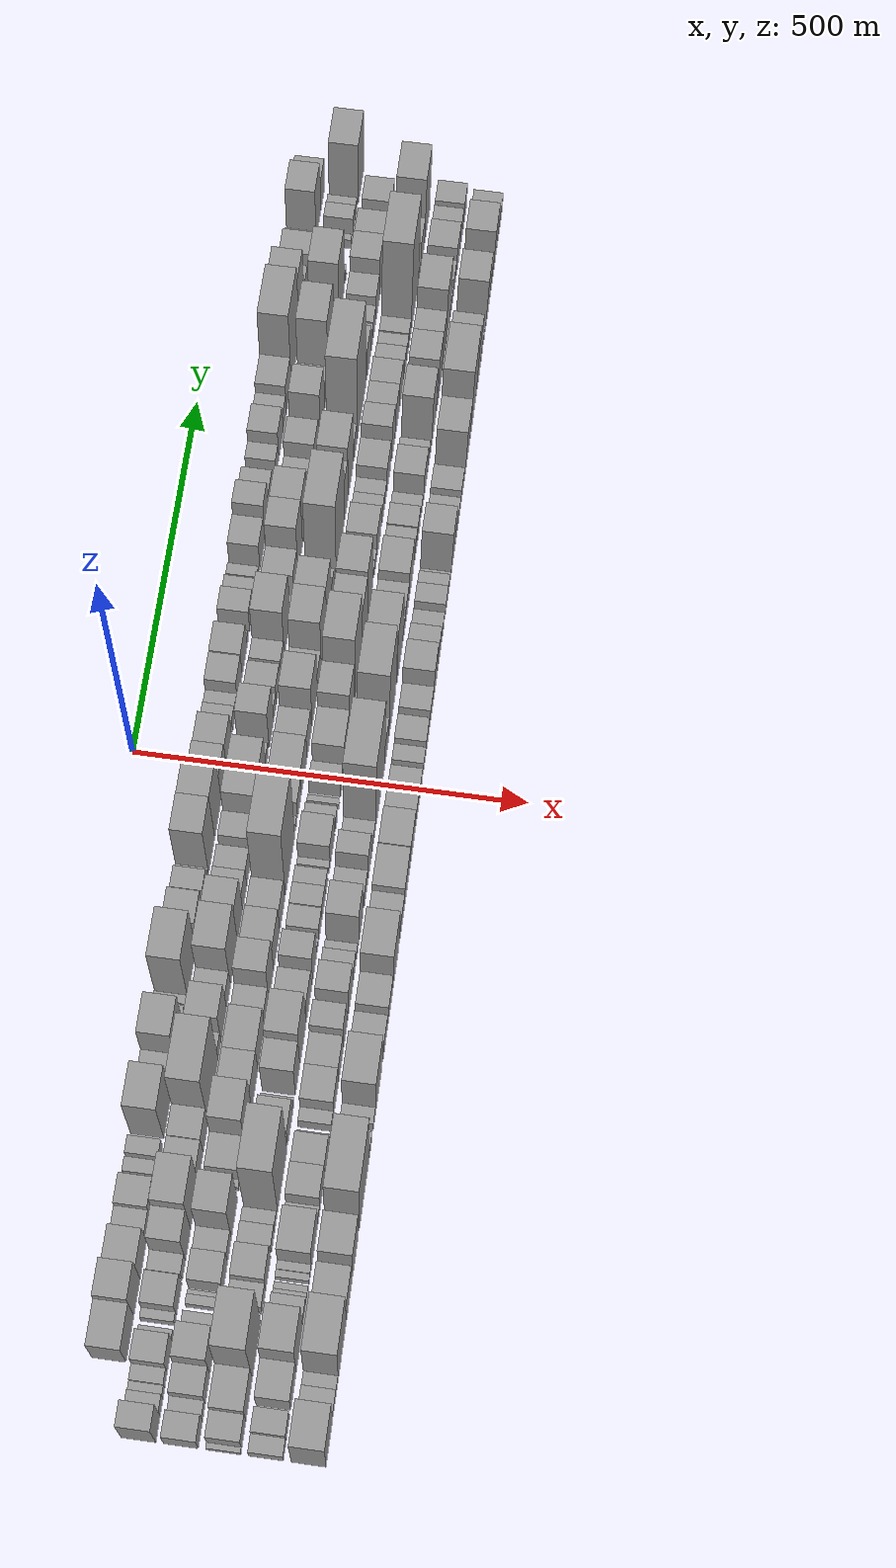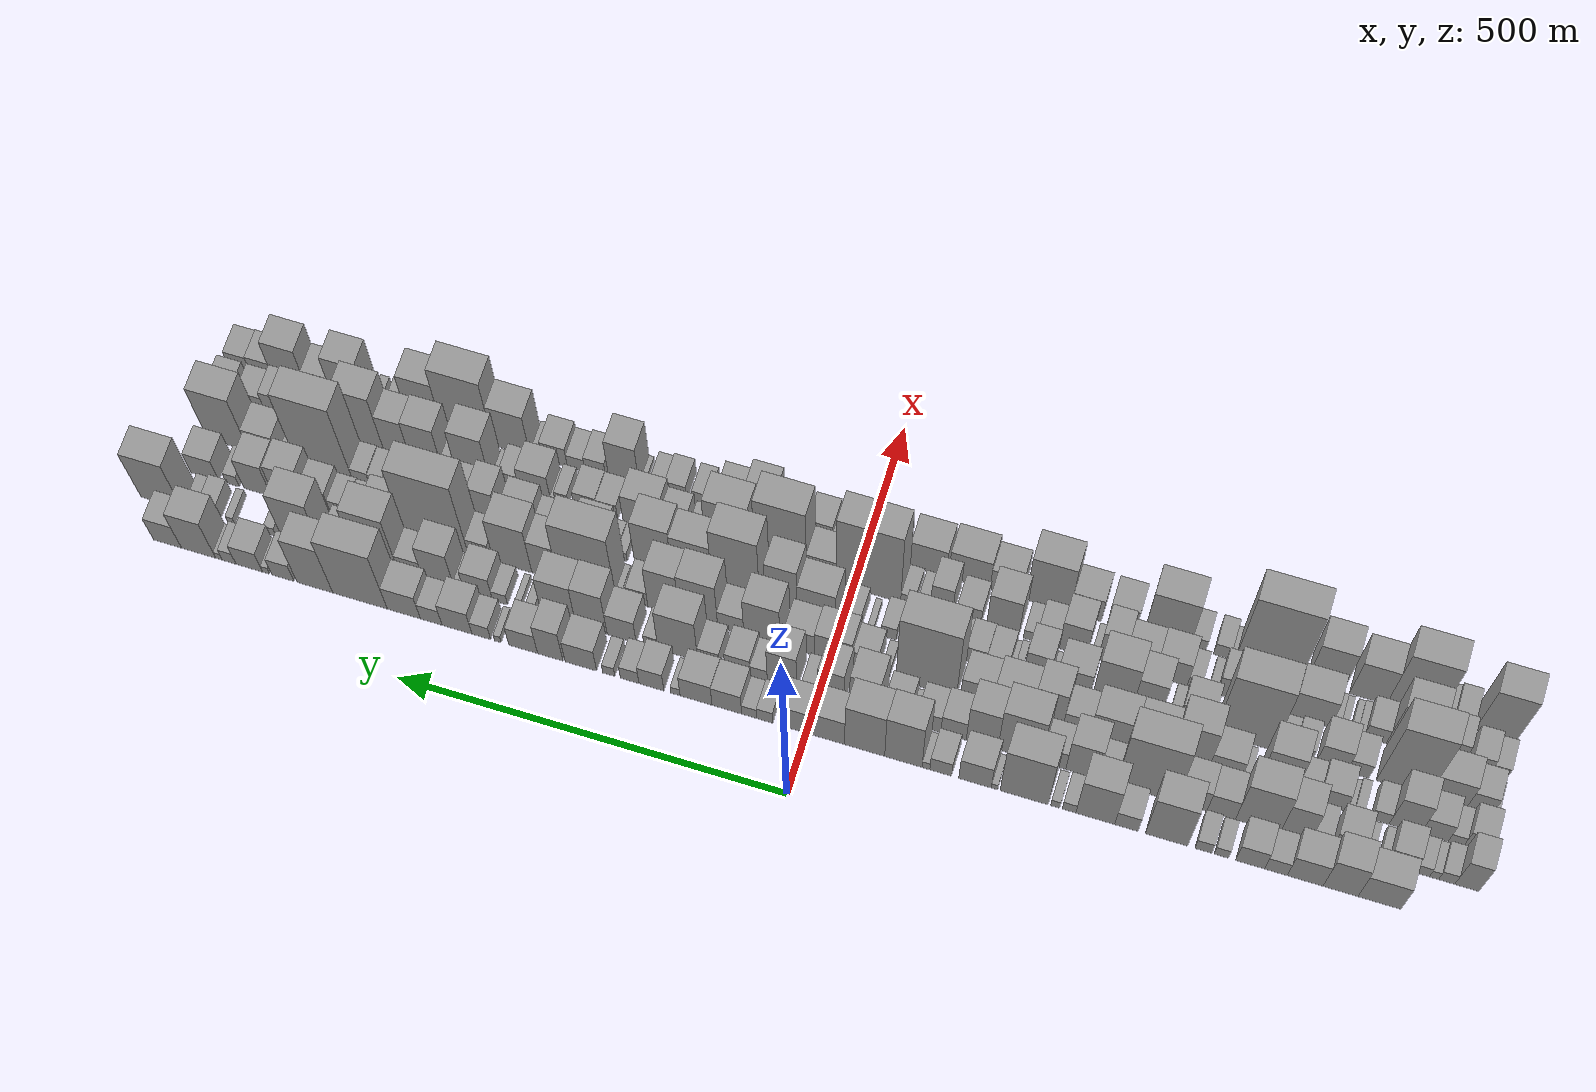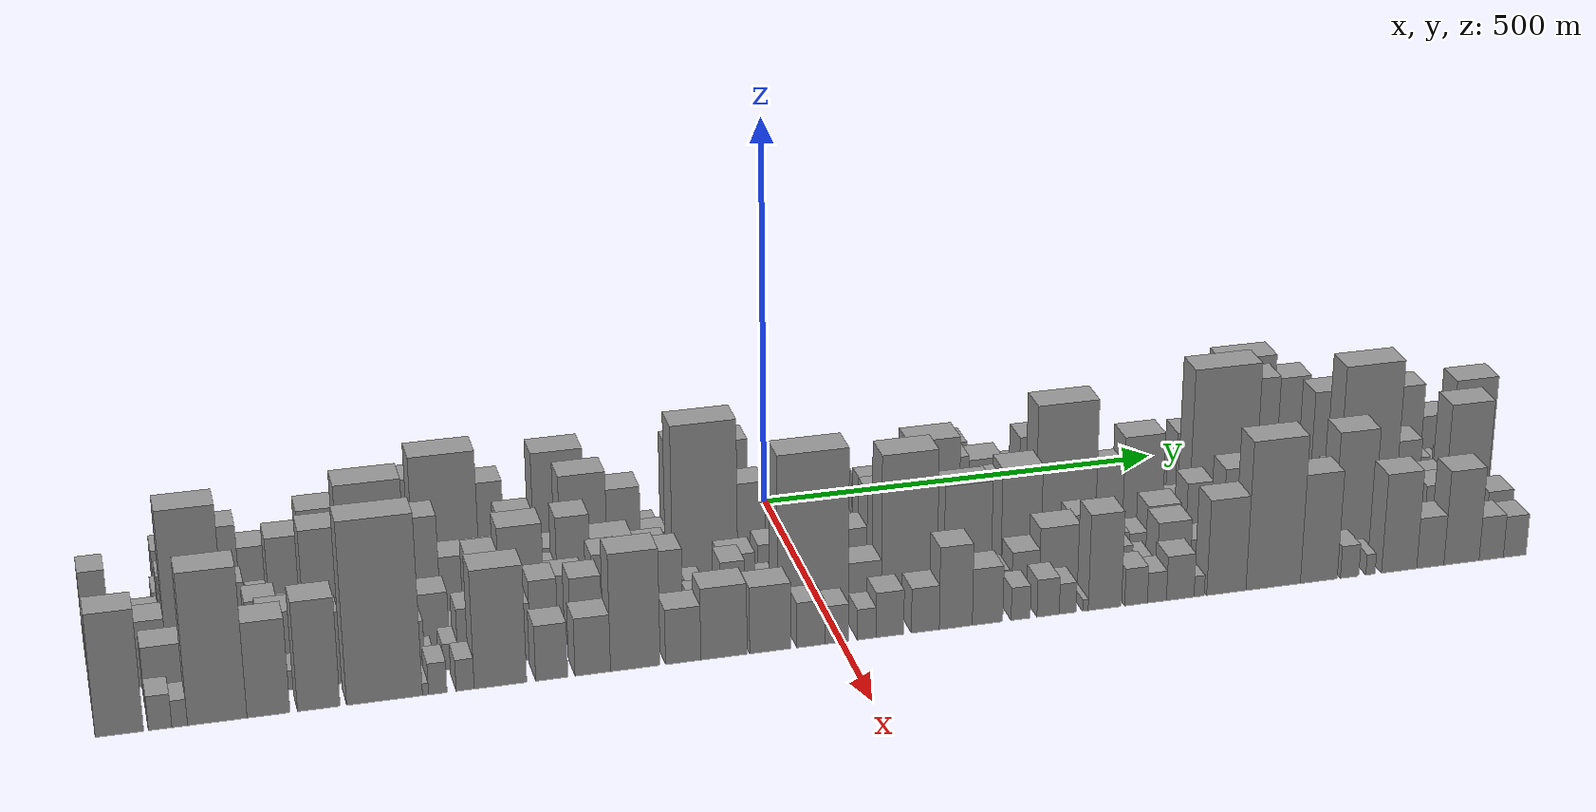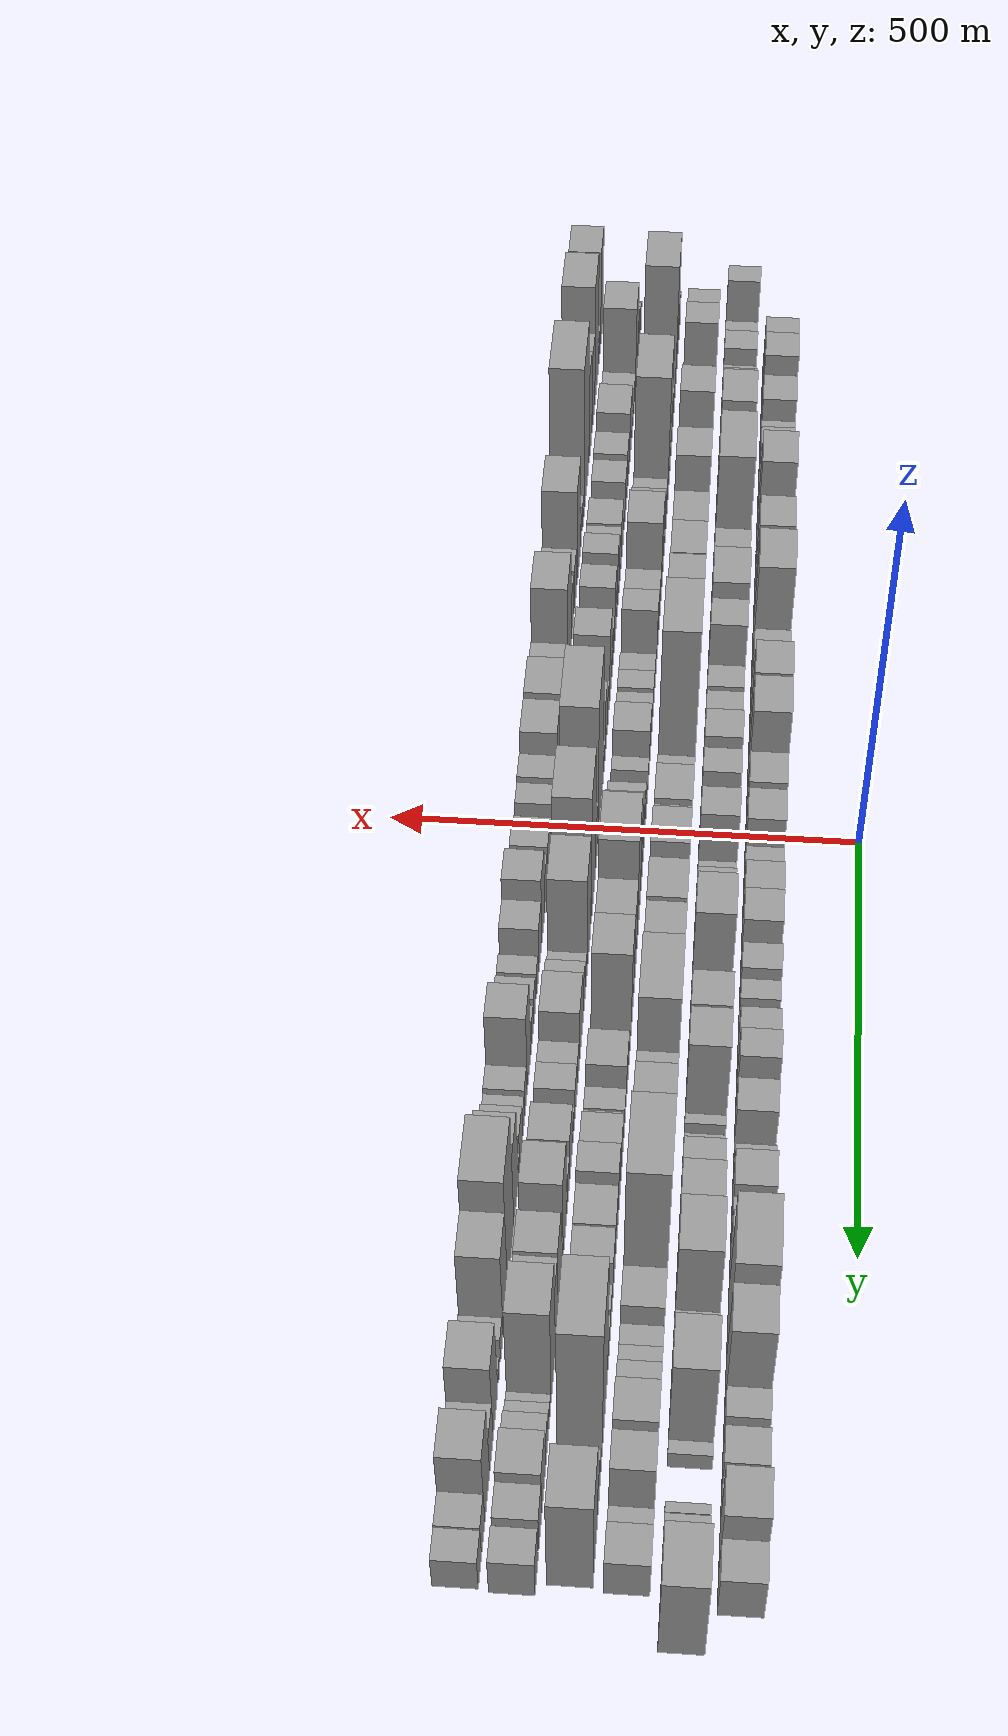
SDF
<sdf version="1.6">
 <world name="default">
  <scene>
   <sky><clouds><speed>12</speed></clouds></sky>
   <ambient>0.4 0.4 0.4 1</ambient>
   <background>0.7 0.7 0.7 1</background>
   <shadows>1</shadows>
  </scene>
  <gravity>0 0 -9.8066</gravity>
  <magnetic_field>6e-06 2.3e-05 -4.2e-05</magnetic_field>
  <physics default="0" name="default_physics" type="ode">
   <ode>
    <solver>
     <type>quick</type>
     <iters>10</iters>
     <sor>1.0</sor>
     <use_dynamic_moi_rescaling>0</use_dynamic_moi_rescaling>
    </solver>
    <constraints>
     <cfm>0</cfm>
     <erp>0.2</erp>
     <contact_max_correcting_vel>100</contact_max_correcting_vel>
     <contact_surface_layer>0.001</contact_surface_layer>
    </constraints>
   </ode>
   <max_step_size>0.004</max_step_size>
   <real_time_factor>1</real_time_factor>
   <real_time_update_rate>250</real_time_update_rate>
  </physics>
  <light name="sun" type="directional">
   <pose>0 0 10 0 0 0</pose>
   <diffuse>0.8 0.8 0.8 1</diffuse>
   <specular>0.2 0.2 0.2 1</specular>
   <attenuation>
    <range>1000</range>
    <constant>0.9</constant>
    <linear>0.01</linear>
    <quadratic>0.001</quadratic>
   </attenuation>
   <direction>-0.5 0.1 -0.9</direction>
  </light>
  <model name="building_1">
   <static>1</static>
   <pose>100.0000 -719.4231 0 0.000000 0.000000 0.000000</pose>
   <link name="link">
    <pose>0 0 45.00 0 0 0</pose>
    <collision name="collision"><geometry><box><size>40.0000 53.0513 90.0000</size></box></geometry></collision>
    <visual name="visual">
     <cast_shadows>0</cast_shadows>
     <geometry><box><size>40.0000 53.0513 90.0000</size></box></geometry>
     <material>
      <script>
       <uri>model://grey_wall/materials/scripts</uri>
       <uri>model://grey_wall/materials/textures</uri>
       <name>vrc/grey_wall</name>
      </script>
     </material>
    </visual>
   </link>
  </model>
  <model name="building_2">
   <static>1</static>
   <pose>100.0000 -671.3288 0 0.000000 0.000000 0.000000</pose>
   <link name="link">
    <pose>0 0 55.50 0 0 0</pose>
    <collision name="collision"><geometry><box><size>40.0000 43.1372 111.0000</size></box></geometry></collision>
    <visual name="visual">
     <cast_shadows>0</cast_shadows>
     <geometry><box><size>40.0000 43.1372 111.0000</size></box></geometry>
     <material>
      <script>
       <uri>model://grey_wall/materials/scripts</uri>
       <uri>model://grey_wall/materials/textures</uri>
       <name>vrc/grey_wall</name>
      </script>
     </material>
    </visual>
   </link>
  </model>
  <model name="building_3">
   <static>1</static>
   <pose>100.0000 -627.5946 0 0.000000 0.000000 0.000000</pose>
   <link name="link">
    <pose>0 0 40.50 0 0 0</pose>
    <collision name="collision"><geometry><box><size>40.0000 44.3313 81.0000</size></box></geometry></collision>
    <visual name="visual">
     <cast_shadows>0</cast_shadows>
     <geometry><box><size>40.0000 44.3313 81.0000</size></box></geometry>
     <material>
      <script>
       <uri>model://grey_wall/materials/scripts</uri>
       <uri>model://grey_wall/materials/textures</uri>
       <name>vrc/grey_wall</name>
      </script>
     </material>
    </visual>
   </link>
  </model>
  <model name="building_4">
   <static>1</static>
   <pose>100.0000 -591.4456 0 0.000000 0.000000 0.000000</pose>
   <link name="link">
    <pose>0 0 24.00 0 0 0</pose>
    <collision name="collision"><geometry><box><size>40.0000 27.9667 48.0000</size></box></geometry></collision>
    <visual name="visual">
     <cast_shadows>0</cast_shadows>
     <geometry><box><size>40.0000 27.9667 48.0000</size></box></geometry>
     <material>
      <script>
       <uri>model://grey_wall/materials/scripts</uri>
       <uri>model://grey_wall/materials/textures</uri>
       <name>vrc/grey_wall</name>
      </script>
     </material>
    </visual>
   </link>
  </model>
  <model name="building_5">
   <static>1</static>
   <pose>100.0000 -559.4655 0 0.000000 0.000000 0.000000</pose>
   <link name="link">
    <pose>0 0 31.50 0 0 0</pose>
    <collision name="collision"><geometry><box><size>40.0000 35.9933 63.0000</size></box></geometry></collision>
    <visual name="visual">
     <cast_shadows>0</cast_shadows>
     <geometry><box><size>40.0000 35.9933 63.0000</size></box></geometry>
     <material>
      <script>
       <uri>model://grey_wall/materials/scripts</uri>
       <uri>model://grey_wall/materials/textures</uri>
       <name>vrc/grey_wall</name>
      </script>
     </material>
    </visual>
   </link>
  </model>
  <model name="building_6">
   <static>1</static>
   <pose>100.0000 -523.7106 0 0.000000 0.000000 0.000000</pose>
   <link name="link">
    <pose>0 0 15.00 0 0 0</pose>
    <collision name="collision"><geometry><box><size>40.0000 17.5167 30.0000</size></box></geometry></collision>
    <visual name="visual">
     <cast_shadows>0</cast_shadows>
     <geometry><box><size>40.0000 17.5167 30.0000</size></box></geometry>
     <material>
      <script>
       <uri>model://grey_wall/materials/scripts</uri>
       <uri>model://grey_wall/materials/textures</uri>
       <name>vrc/grey_wall</name>
      </script>
     </material>
    </visual>
   </link>
  </model>
  <model name="building_7">
   <static>1</static>
   <pose>100.0000 -501.3725 0 0.000000 0.000000 0.000000</pose>
   <link name="link">
    <pose>0 0 18.00 0 0 0</pose>
    <collision name="collision"><geometry><box><size>40.0000 21.1595 36.0000</size></box></geometry></collision>
    <visual name="visual">
     <cast_shadows>0</cast_shadows>
     <geometry><box><size>40.0000 21.1595 36.0000</size></box></geometry>
     <material>
      <script>
       <uri>model://grey_wall/materials/scripts</uri>
       <uri>model://grey_wall/materials/textures</uri>
       <name>vrc/grey_wall</name>
      </script>
     </material>
    </visual>
   </link>
  </model>
  <model name="building_8">
   <static>1</static>
   <pose>100.0000 -455.3490 0 0.000000 0.000000 0.000000</pose>
   <link name="link">
    <pose>0 0 72.00 0 0 0</pose>
    <collision name="collision"><geometry><box><size>40.0000 52.8873 144.0000</size></box></geometry></collision>
    <visual name="visual">
     <cast_shadows>0</cast_shadows>
     <geometry><box><size>40.0000 52.8873 144.0000</size></box></geometry>
     <material>
      <script>
       <uri>model://grey_wall/materials/scripts</uri>
       <uri>model://grey_wall/materials/textures</uri>
       <name>vrc/grey_wall</name>
      </script>
     </material>
    </visual>
   </link>
  </model>
  <model name="building_9">
   <static>1</static>
   <pose>100.0000 -405.2098 0 0.000000 0.000000 0.000000</pose>
   <link name="link">
    <pose>0 0 25.50 0 0 0</pose>
    <collision name="collision"><geometry><box><size>40.0000 29.3912 51.0000</size></box></geometry></collision>
    <visual name="visual">
     <cast_shadows>0</cast_shadows>
     <geometry><box><size>40.0000 29.3912 51.0000</size></box></geometry>
     <material>
      <script>
       <uri>model://grey_wall/materials/scripts</uri>
       <uri>model://grey_wall/materials/textures</uri>
       <name>vrc/grey_wall</name>
      </script>
     </material>
    </visual>
   </link>
  </model>
  <model name="building_10">
   <static>1</static>
   <pose>100.0000 -366.1211 0 0.000000 0.000000 0.000000</pose>
   <link name="link">
    <pose>0 0 64.50 0 0 0</pose>
    <collision name="collision"><geometry><box><size>40.0000 48.7862 129.0000</size></box></geometry></collision>
    <visual name="visual">
     <cast_shadows>0</cast_shadows>
     <geometry><box><size>40.0000 48.7862 129.0000</size></box></geometry>
     <material>
      <script>
       <uri>model://grey_wall/materials/scripts</uri>
       <uri>model://grey_wall/materials/textures</uri>
       <name>vrc/grey_wall</name>
      </script>
     </material>
    </visual>
   </link>
  </model>
  <model name="building_11">
   <static>1</static>
   <pose>100.0000 -333.1940 0 0.000000 0.000000 0.000000</pose>
   <link name="link">
    <pose>0 0 15.00 0 0 0</pose>
    <collision name="collision"><geometry><box><size>40.0000 17.0678 30.0000</size></box></geometry></collision>
    <visual name="visual">
     <cast_shadows>0</cast_shadows>
     <geometry><box><size>40.0000 17.0678 30.0000</size></box></geometry>
     <material>
      <script>
       <uri>model://grey_wall/materials/scripts</uri>
       <uri>model://grey_wall/materials/textures</uri>
       <name>vrc/grey_wall</name>
      </script>
     </material>
    </visual>
   </link>
  </model>
  <model name="building_12">
   <static>1</static>
   <pose>100.0000 -315.8564 0 0.000000 0.000000 0.000000</pose>
   <link name="link">
    <pose>0 0 12.00 0 0 0</pose>
    <collision name="collision"><geometry><box><size>40.0000 11.6074 24.0000</size></box></geometry></collision>
    <visual name="visual">
     <cast_shadows>0</cast_shadows>
     <geometry><box><size>40.0000 11.6074 24.0000</size></box></geometry>
     <material>
      <script>
       <uri>model://grey_wall/materials/scripts</uri>
       <uri>model://grey_wall/materials/textures</uri>
       <name>vrc/grey_wall</name>
      </script>
     </material>
    </visual>
   </link>
  </model>
  <model name="building_13">
   <static>1</static>
   <pose>100.0000 -276.7017 0 0.000000 0.000000 0.000000</pose>
   <link name="link">
    <pose>0 0 79.50 0 0 0</pose>
    <collision name="collision"><geometry><box><size>40.0000 60.7021 159.0000</size></box></geometry></collision>
    <visual name="visual">
     <cast_shadows>0</cast_shadows>
     <geometry><box><size>40.0000 60.7021 159.0000</size></box></geometry>
     <material>
      <script>
       <uri>model://grey_wall/materials/scripts</uri>
       <uri>model://grey_wall/materials/textures</uri>
       <name>vrc/grey_wall</name>
      </script>
     </material>
    </visual>
   </link>
  </model>
  <model name="building_14">
   <static>1</static>
   <pose>100.0000 -239.2034 0 0.000000 0.000000 0.000000</pose>
   <link name="link">
    <pose>0 0 9.00 0 0 0</pose>
    <collision name="collision"><geometry><box><size>40.0000 8.2945 18.0000</size></box></geometry></collision>
    <visual name="visual">
     <cast_shadows>0</cast_shadows>
     <geometry><box><size>40.0000 8.2945 18.0000</size></box></geometry>
     <material>
      <script>
       <uri>model://grey_wall/materials/scripts</uri>
       <uri>model://grey_wall/materials/textures</uri>
       <name>vrc/grey_wall</name>
      </script>
     </material>
    </visual>
   </link>
  </model>
  <model name="building_15">
   <static>1</static>
   <pose>100.0000 -214.5223 0 0.000000 0.000000 0.000000</pose>
   <link name="link">
    <pose>0 0 37.50 0 0 0</pose>
    <collision name="collision"><geometry><box><size>40.0000 41.0677 75.0000</size></box></geometry></collision>
    <visual name="visual">
     <cast_shadows>0</cast_shadows>
     <geometry><box><size>40.0000 41.0677 75.0000</size></box></geometry>
     <material>
      <script>
       <uri>model://grey_wall/materials/scripts</uri>
       <uri>model://grey_wall/materials/textures</uri>
       <name>vrc/grey_wall</name>
      </script>
     </material>
    </visual>
   </link>
  </model>
  <model name="building_16">
   <static>1</static>
   <pose>100.0000 -171.2197 0 0.000000 0.000000 0.000000</pose>
   <link name="link">
    <pose>0 0 24.00 0 0 0</pose>
    <collision name="collision"><geometry><box><size>40.0000 27.5374 48.0000</size></box></geometry></collision>
    <visual name="visual">
     <cast_shadows>0</cast_shadows>
     <geometry><box><size>40.0000 27.5374 48.0000</size></box></geometry>
     <material>
      <script>
       <uri>model://grey_wall/materials/scripts</uri>
       <uri>model://grey_wall/materials/textures</uri>
       <name>vrc/grey_wall</name>
      </script>
     </material>
    </visual>
   </link>
  </model>
  <model name="building_17">
   <static>1</static>
   <pose>100.0000 -152.4533 0 0.000000 0.000000 0.000000</pose>
   <link name="link">
    <pose>0 0 12.00 0 0 0</pose>
    <collision name="collision"><geometry><box><size>40.0000 9.9954 24.0000</size></box></geometry></collision>
    <visual name="visual">
     <cast_shadows>0</cast_shadows>
     <geometry><box><size>40.0000 9.9954 24.0000</size></box></geometry>
     <material>
      <script>
       <uri>model://grey_wall/materials/scripts</uri>
       <uri>model://grey_wall/materials/textures</uri>
       <name>vrc/grey_wall</name>
      </script>
     </material>
    </visual>
   </link>
  </model>
  <model name="building_18">
   <static>1</static>
   <pose>100.0000 -123.7615 0 0.000000 0.000000 0.000000</pose>
   <link name="link">
    <pose>0 0 75.00 0 0 0</pose>
    <collision name="collision"><geometry><box><size>40.0000 47.3882 150.0000</size></box></geometry></collision>
    <visual name="visual">
     <cast_shadows>0</cast_shadows>
     <geometry><box><size>40.0000 47.3882 150.0000</size></box></geometry>
     <material>
      <script>
       <uri>model://grey_wall/materials/scripts</uri>
       <uri>model://grey_wall/materials/textures</uri>
       <name>vrc/grey_wall</name>
      </script>
     </material>
    </visual>
   </link>
  </model>
  <model name="building_19">
   <static>1</static>
   <pose>100.0000 -74.5731 0 0.000000 0.000000 0.000000</pose>
   <link name="link">
    <pose>0 0 73.50 0 0 0</pose>
    <collision name="collision"><geometry><box><size>40.0000 50.9886 147.0000</size></box></geometry></collision>
    <visual name="visual">
     <cast_shadows>0</cast_shadows>
     <geometry><box><size>40.0000 50.9886 147.0000</size></box></geometry>
     <material>
      <script>
       <uri>model://grey_wall/materials/scripts</uri>
       <uri>model://grey_wall/materials/textures</uri>
       <name>vrc/grey_wall</name>
      </script>
     </material>
    </visual>
   </link>
  </model>
  <model name="building_20">
   <static>1</static>
   <pose>100.0000 -27.8224 0 0.000000 0.000000 0.000000</pose>
   <link name="link">
    <pose>0 0 42.00 0 0 0</pose>
    <collision name="collision"><geometry><box><size>40.0000 42.5128 84.0000</size></box></geometry></collision>
    <visual name="visual">
     <cast_shadows>0</cast_shadows>
     <geometry><box><size>40.0000 42.5128 84.0000</size></box></geometry>
     <material>
      <script>
       <uri>model://grey_wall/materials/scripts</uri>
       <uri>model://grey_wall/materials/textures</uri>
       <name>vrc/grey_wall</name>
      </script>
     </material>
    </visual>
   </link>
  </model>
  <model name="building_21">
   <static>1</static>
   <pose>100.0000 14.5103 0 0.000000 0.000000 0.000000</pose>
   <link name="link">
    <pose>0 0 37.50 0 0 0</pose>
    <collision name="collision"><geometry><box><size>40.0000 42.1527 75.0000</size></box></geometry></collision>
    <visual name="visual">
     <cast_shadows>0</cast_shadows>
     <geometry><box><size>40.0000 42.1527 75.0000</size></box></geometry>
     <material>
      <script>
       <uri>model://grey_wall/materials/scripts</uri>
       <uri>model://grey_wall/materials/textures</uri>
       <name>vrc/grey_wall</name>
      </script>
     </material>
    </visual>
   </link>
  </model>
  <model name="building_22">
   <static>1</static>
   <pose>100.0000 52.8745 0 0.000000 0.000000 0.000000</pose>
   <link name="link">
    <pose>0 0 19.50 0 0 0</pose>
    <collision name="collision"><geometry><box><size>40.0000 20.5757 39.0000</size></box></geometry></collision>
    <visual name="visual">
     <cast_shadows>0</cast_shadows>
     <geometry><box><size>40.0000 20.5757 39.0000</size></box></geometry>
     <material>
      <script>
       <uri>model://grey_wall/materials/scripts</uri>
       <uri>model://grey_wall/materials/textures</uri>
       <name>vrc/grey_wall</name>
      </script>
     </material>
    </visual>
   </link>
  </model>
  <model name="building_23">
   <static>1</static>
   <pose>100.0000 72.8543 0 0.000000 0.000000 0.000000</pose>
   <link name="link">
    <pose>0 0 16.50 0 0 0</pose>
    <collision name="collision"><geometry><box><size>40.0000 19.3839 33.0000</size></box></geometry></collision>
    <visual name="visual">
     <cast_shadows>0</cast_shadows>
     <geometry><box><size>40.0000 19.3839 33.0000</size></box></geometry>
     <material>
      <script>
       <uri>model://grey_wall/materials/scripts</uri>
       <uri>model://grey_wall/materials/textures</uri>
       <name>vrc/grey_wall</name>
      </script>
     </material>
    </visual>
   </link>
  </model>
  <model name="building_24">
   <static>1</static>
   <pose>100.0000 101.5590 0 0.000000 0.000000 0.000000</pose>
   <link name="link">
    <pose>0 0 33.00 0 0 0</pose>
    <collision name="collision"><geometry><box><size>40.0000 38.0256 66.0000</size></box></geometry></collision>
    <visual name="visual">
     <cast_shadows>0</cast_shadows>
     <geometry><box><size>40.0000 38.0256 66.0000</size></box></geometry>
     <material>
      <script>
       <uri>model://grey_wall/materials/scripts</uri>
       <uri>model://grey_wall/materials/textures</uri>
       <name>vrc/grey_wall</name>
      </script>
     </material>
    </visual>
   </link>
  </model>
  <model name="building_25">
   <static>1</static>
   <pose>100.0000 141.0999 0 0.000000 0.000000 0.000000</pose>
   <link name="link">
    <pose>0 0 34.50 0 0 0</pose>
    <collision name="collision"><geometry><box><size>40.0000 41.0561 69.0000</size></box></geometry></collision>
    <visual name="visual">
     <cast_shadows>0</cast_shadows>
     <geometry><box><size>40.0000 41.0561 69.0000</size></box></geometry>
     <material>
      <script>
       <uri>model://grey_wall/materials/scripts</uri>
       <uri>model://grey_wall/materials/textures</uri>
       <name>vrc/grey_wall</name>
      </script>
     </material>
    </visual>
   </link>
  </model>
  <model name="building_26">
   <static>1</static>
   <pose>100.0000 167.6077 0 0.000000 0.000000 0.000000</pose>
   <link name="link">
    <pose>0 0 12.00 0 0 0</pose>
    <collision name="collision"><geometry><box><size>40.0000 11.9596 24.0000</size></box></geometry></collision>
    <visual name="visual">
     <cast_shadows>0</cast_shadows>
     <geometry><box><size>40.0000 11.9596 24.0000</size></box></geometry>
     <material>
      <script>
       <uri>model://grey_wall/materials/scripts</uri>
       <uri>model://grey_wall/materials/textures</uri>
       <name>vrc/grey_wall</name>
      </script>
     </material>
    </visual>
   </link>
  </model>
  <model name="building_27">
   <static>1</static>
   <pose>100.0000 198.6026 0 0.000000 0.000000 0.000000</pose>
   <link name="link">
    <pose>0 0 30.00 0 0 0</pose>
    <collision name="collision"><geometry><box><size>40.0000 32.0300 60.0000</size></box></geometry></collision>
    <visual name="visual">
     <cast_shadows>0</cast_shadows>
     <geometry><box><size>40.0000 32.0300 60.0000</size></box></geometry>
     <material>
      <script>
       <uri>model://grey_wall/materials/scripts</uri>
       <uri>model://grey_wall/materials/textures</uri>
       <name>vrc/grey_wall</name>
      </script>
     </material>
    </visual>
   </link>
  </model>
  <model name="building_28">
   <static>1</static>
   <pose>100.0000 226.7114 0 0.000000 0.000000 0.000000</pose>
   <link name="link">
    <pose>0 0 21.00 0 0 0</pose>
    <collision name="collision"><geometry><box><size>40.0000 24.1877 42.0000</size></box></geometry></collision>
    <visual name="visual">
     <cast_shadows>0</cast_shadows>
     <geometry><box><size>40.0000 24.1877 42.0000</size></box></geometry>
     <material>
      <script>
       <uri>model://grey_wall/materials/scripts</uri>
       <uri>model://grey_wall/materials/textures</uri>
       <name>vrc/grey_wall</name>
      </script>
     </material>
    </visual>
   </link>
  </model>
  <model name="building_29">
   <static>1</static>
   <pose>100.0000 253.6481 0 0.000000 0.000000 0.000000</pose>
   <link name="link">
    <pose>0 0 15.00 0 0 0</pose>
    <collision name="collision"><geometry><box><size>40.0000 15.6857 30.0000</size></box></geometry></collision>
    <visual name="visual">
     <cast_shadows>0</cast_shadows>
     <geometry><box><size>40.0000 15.6857 30.0000</size></box></geometry>
     <material>
      <script>
       <uri>model://grey_wall/materials/scripts</uri>
       <uri>model://grey_wall/materials/textures</uri>
       <name>vrc/grey_wall</name>
      </script>
     </material>
    </visual>
   </link>
  </model>
  <model name="building_30">
   <static>1</static>
   <pose>100.0000 289.8574 0 0.000000 0.000000 0.000000</pose>
   <link name="link">
    <pose>0 0 36.00 0 0 0</pose>
    <collision name="collision"><geometry><box><size>40.0000 40.7329 72.0000</size></box></geometry></collision>
    <visual name="visual">
     <cast_shadows>0</cast_shadows>
     <geometry><box><size>40.0000 40.7329 72.0000</size></box></geometry>
     <material>
      <script>
       <uri>model://grey_wall/materials/scripts</uri>
       <uri>model://grey_wall/materials/textures</uri>
       <name>vrc/grey_wall</name>
      </script>
     </material>
    </visual>
   </link>
  </model>
  <model name="building_31">
   <static>1</static>
   <pose>100.0000 329.6770 0 0.000000 0.000000 0.000000</pose>
   <link name="link">
    <pose>0 0 49.50 0 0 0</pose>
    <collision name="collision"><geometry><box><size>40.0000 32.9062 99.0000</size></box></geometry></collision>
    <visual name="visual">
     <cast_shadows>0</cast_shadows>
     <geometry><box><size>40.0000 32.9062 99.0000</size></box></geometry>
     <material>
      <script>
       <uri>model://grey_wall/materials/scripts</uri>
       <uri>model://grey_wall/materials/textures</uri>
       <name>vrc/grey_wall</name>
      </script>
     </material>
    </visual>
   </link>
  </model>
  <model name="building_32">
   <static>1</static>
   <pose>100.0000 364.8197 0 0.000000 0.000000 0.000000</pose>
   <link name="link">
    <pose>0 0 31.50 0 0 0</pose>
    <collision name="collision"><geometry><box><size>40.0000 37.3792 63.0000</size></box></geometry></collision>
    <visual name="visual">
     <cast_shadows>0</cast_shadows>
     <geometry><box><size>40.0000 37.3792 63.0000</size></box></geometry>
     <material>
      <script>
       <uri>model://grey_wall/materials/scripts</uri>
       <uri>model://grey_wall/materials/textures</uri>
       <name>vrc/grey_wall</name>
      </script>
     </material>
    </visual>
   </link>
  </model>
  <model name="building_33">
   <static>1</static>
   <pose>100.0000 397.9231 0 0.000000 0.000000 0.000000</pose>
   <link name="link">
    <pose>0 0 10.50 0 0 0</pose>
    <collision name="collision"><geometry><box><size>40.0000 8.8275 21.0000</size></box></geometry></collision>
    <visual name="visual">
     <cast_shadows>0</cast_shadows>
     <geometry><box><size>40.0000 8.8275 21.0000</size></box></geometry>
     <material>
      <script>
       <uri>model://grey_wall/materials/scripts</uri>
       <uri>model://grey_wall/materials/textures</uri>
       <name>vrc/grey_wall</name>
      </script>
     </material>
    </visual>
   </link>
  </model>
  <model name="building_34">
   <static>1</static>
   <pose>100.0000 419.4224 0 0.000000 0.000000 0.000000</pose>
   <link name="link">
    <pose>0 0 21.00 0 0 0</pose>
    <collision name="collision"><geometry><box><size>40.0000 24.1710 42.0000</size></box></geometry></collision>
    <visual name="visual">
     <cast_shadows>0</cast_shadows>
     <geometry><box><size>40.0000 24.1710 42.0000</size></box></geometry>
     <material>
      <script>
       <uri>model://grey_wall/materials/scripts</uri>
       <uri>model://grey_wall/materials/textures</uri>
       <name>vrc/grey_wall</name>
      </script>
     </material>
    </visual>
   </link>
  </model>
  <model name="building_35">
   <static>1</static>
   <pose>100.0000 451.1182 0 0.000000 0.000000 0.000000</pose>
   <link name="link">
    <pose>0 0 36.00 0 0 0</pose>
    <collision name="collision"><geometry><box><size>40.0000 39.2206 72.0000</size></box></geometry></collision>
    <visual name="visual">
     <cast_shadows>0</cast_shadows>
     <geometry><box><size>40.0000 39.2206 72.0000</size></box></geometry>
     <material>
      <script>
       <uri>model://grey_wall/materials/scripts</uri>
       <uri>model://grey_wall/materials/textures</uri>
       <name>vrc/grey_wall</name>
      </script>
     </material>
    </visual>
   </link>
  </model>
  <model name="building_36">
   <static>1</static>
   <pose>100.0000 484.8960 0 0.000000 0.000000 0.000000</pose>
   <link name="link">
    <pose>0 0 25.50 0 0 0</pose>
    <collision name="collision"><geometry><box><size>40.0000 28.3350 51.0000</size></box></geometry></collision>
    <visual name="visual">
     <cast_shadows>0</cast_shadows>
     <geometry><box><size>40.0000 28.3350 51.0000</size></box></geometry>
     <material>
      <script>
       <uri>model://grey_wall/materials/scripts</uri>
       <uri>model://grey_wall/materials/textures</uri>
       <name>vrc/grey_wall</name>
      </script>
     </material>
    </visual>
   </link>
  </model>
  <model name="building_37">
   <static>1</static>
   <pose>100.0000 520.7871 0 0.000000 0.000000 0.000000</pose>
   <link name="link">
    <pose>0 0 37.50 0 0 0</pose>
    <collision name="collision"><geometry><box><size>40.0000 43.4472 75.0000</size></box></geometry></collision>
    <visual name="visual">
     <cast_shadows>0</cast_shadows>
     <geometry><box><size>40.0000 43.4472 75.0000</size></box></geometry>
     <material>
      <script>
       <uri>model://grey_wall/materials/scripts</uri>
       <uri>model://grey_wall/materials/textures</uri>
       <name>vrc/grey_wall</name>
      </script>
     </material>
    </visual>
   </link>
  </model>
  <model name="building_38">
   <static>1</static>
   <pose>100.0000 578.3830 0 0.000000 0.000000 0.000000</pose>
   <link name="link">
    <pose>0 0 90.00 0 0 0</pose>
    <collision name="collision"><geometry><box><size>40.0000 71.7446 180.0000</size></box></geometry></collision>
    <visual name="visual">
     <cast_shadows>0</cast_shadows>
     <geometry><box><size>40.0000 71.7446 180.0000</size></box></geometry>
     <material>
      <script>
       <uri>model://grey_wall/materials/scripts</uri>
       <uri>model://grey_wall/materials/textures</uri>
       <name>vrc/grey_wall</name>
      </script>
     </material>
    </visual>
   </link>
  </model>
  <model name="building_39">
   <static>1</static>
   <pose>100.0000 637.8473 0 0.000000 0.000000 0.000000</pose>
   <link name="link">
    <pose>0 0 73.50 0 0 0</pose>
    <collision name="collision"><geometry><box><size>40.0000 47.1841 147.0000</size></box></geometry></collision>
    <visual name="visual">
     <cast_shadows>0</cast_shadows>
     <geometry><box><size>40.0000 47.1841 147.0000</size></box></geometry>
     <material>
      <script>
       <uri>model://grey_wall/materials/scripts</uri>
       <uri>model://grey_wall/materials/textures</uri>
       <name>vrc/grey_wall</name>
      </script>
     </material>
    </visual>
   </link>
  </model>
  <model name="building_40">
   <static>1</static>
   <pose>100.0000 680.1774 0 0.000000 0.000000 0.000000</pose>
   <link name="link">
    <pose>0 0 27.00 0 0 0</pose>
    <collision name="collision"><geometry><box><size>40.0000 29.4762 54.0000</size></box></geometry></collision>
    <visual name="visual">
     <cast_shadows>0</cast_shadows>
     <geometry><box><size>40.0000 29.4762 54.0000</size></box></geometry>
     <material>
      <script>
       <uri>model://grey_wall/materials/scripts</uri>
       <uri>model://grey_wall/materials/textures</uri>
       <name>vrc/grey_wall</name>
      </script>
     </material>
    </visual>
   </link>
  </model>
  <model name="building_41">
   <static>1</static>
   <pose>100.0000 702.4432 0 0.000000 0.000000 0.000000</pose>
   <link name="link">
    <pose>0 0 10.50 0 0 0</pose>
    <collision name="collision"><geometry><box><size>40.0000 9.0554 21.0000</size></box></geometry></collision>
    <visual name="visual">
     <cast_shadows>0</cast_shadows>
     <geometry><box><size>40.0000 9.0554 21.0000</size></box></geometry>
     <material>
      <script>
       <uri>model://grey_wall/materials/scripts</uri>
       <uri>model://grey_wall/materials/textures</uri>
       <name>vrc/grey_wall</name>
      </script>
     </material>
    </visual>
   </link>
  </model>
  <model name="building_42">
   <static>1</static>
   <pose>100.0000 724.6677 0 0.000000 0.000000 0.000000</pose>
   <link name="link">
    <pose>0 0 31.50 0 0 0</pose>
    <collision name="collision"><geometry><box><size>40.0000 35.3935 63.0000</size></box></geometry></collision>
    <visual name="visual">
     <cast_shadows>0</cast_shadows>
     <geometry><box><size>40.0000 35.3935 63.0000</size></box></geometry>
     <material>
      <script>
       <uri>model://grey_wall/materials/scripts</uri>
       <uri>model://grey_wall/materials/textures</uri>
       <name>vrc/grey_wall</name>
      </script>
     </material>
    </visual>
   </link>
  </model>
  <model name="building_43">
   <static>1</static>
   <pose>100.0000 751.5607 0 0.000000 0.000000 0.000000</pose>
   <link name="link">
    <pose>0 0 18.00 0 0 0</pose>
    <collision name="collision"><geometry><box><size>40.0000 18.3925 36.0000</size></box></geometry></collision>
    <visual name="visual">
     <cast_shadows>0</cast_shadows>
     <geometry><box><size>40.0000 18.3925 36.0000</size></box></geometry>
     <material>
      <script>
       <uri>model://grey_wall/materials/scripts</uri>
       <uri>model://grey_wall/materials/textures</uri>
       <name>vrc/grey_wall</name>
      </script>
     </material>
    </visual>
   </link>
  </model>
  <model name="building_44">
   <static>1</static>
   <pose>100.0000 764.9816 0 0.000000 0.000000 0.000000</pose>
   <link name="link">
    <pose>0 0 10.50 0 0 0</pose>
    <collision name="collision"><geometry><box><size>40.0000 8.4495 21.0000</size></box></geometry></collision>
    <visual name="visual">
     <cast_shadows>0</cast_shadows>
     <geometry><box><size>40.0000 8.4495 21.0000</size></box></geometry>
     <material>
      <script>
       <uri>model://grey_wall/materials/scripts</uri>
       <uri>model://grey_wall/materials/textures</uri>
       <name>vrc/grey_wall</name>
      </script>
     </material>
    </visual>
   </link>
  </model>
  <model name="building_45">
   <static>1</static>
   <pose>100.0000 791.9245 0 0.000000 0.000000 0.000000</pose>
   <link name="link">
    <pose>0 0 58.50 0 0 0</pose>
    <collision name="collision"><geometry><box><size>40.0000 45.4362 117.0000</size></box></geometry></collision>
    <visual name="visual">
     <cast_shadows>0</cast_shadows>
     <geometry><box><size>40.0000 45.4362 117.0000</size></box></geometry>
     <material>
      <script>
       <uri>model://grey_wall/materials/scripts</uri>
       <uri>model://grey_wall/materials/textures</uri>
       <name>vrc/grey_wall</name>
      </script>
     </material>
    </visual>
   </link>
  </model>
  <model name="building_46">
   <static>1</static>
   <pose>100.0000 833.3077 0 0.000000 0.000000 0.000000</pose>
   <link name="link">
    <pose>0 0 36.00 0 0 0</pose>
    <collision name="collision"><geometry><box><size>40.0000 37.3301 72.0000</size></box></geometry></collision>
    <visual name="visual">
     <cast_shadows>0</cast_shadows>
     <geometry><box><size>40.0000 37.3301 72.0000</size></box></geometry>
     <material>
      <script>
       <uri>model://grey_wall/materials/scripts</uri>
       <uri>model://grey_wall/materials/textures</uri>
       <name>vrc/grey_wall</name>
      </script>
     </material>
    </visual>
   </link>
  </model>
  <model name="building_47">
   <static>1</static>
   <pose>149.0000 -815.1454 0 0.000000 0.000000 0.000000</pose>
   <link name="link">
    <pose>0 0 49.50 0 0 0</pose>
    <collision name="collision"><geometry><box><size>40.0000 29.7091 99.0000</size></box></geometry></collision>
    <visual name="visual">
     <cast_shadows>0</cast_shadows>
     <geometry><box><size>40.0000 29.7091 99.0000</size></box></geometry>
     <material>
      <script>
       <uri>model://grey_wall/materials/scripts</uri>
       <uri>model://grey_wall/materials/textures</uri>
       <name>vrc/grey_wall</name>
      </script>
     </material>
    </visual>
   </link>
  </model>
  <model name="building_48">
   <static>1</static>
   <pose>149.0000 -790.3223 0 0.000000 0.000000 0.000000</pose>
   <link name="link">
    <pose>0 0 18.00 0 0 0</pose>
    <collision name="collision"><geometry><box><size>40.0000 19.9372 36.0000</size></box></geometry></collision>
    <visual name="visual">
     <cast_shadows>0</cast_shadows>
     <geometry><box><size>40.0000 19.9372 36.0000</size></box></geometry>
     <material>
      <script>
       <uri>model://grey_wall/materials/scripts</uri>
       <uri>model://grey_wall/materials/textures</uri>
       <name>vrc/grey_wall</name>
      </script>
     </material>
    </visual>
   </link>
  </model>
  <model name="building_49">
   <static>1</static>
   <pose>149.0000 -774.7295 0 0.000000 0.000000 0.000000</pose>
   <link name="link">
    <pose>0 0 13.50 0 0 0</pose>
    <collision name="collision"><geometry><box><size>40.0000 11.2483 27.0000</size></box></geometry></collision>
    <visual name="visual">
     <cast_shadows>0</cast_shadows>
     <geometry><box><size>40.0000 11.2483 27.0000</size></box></geometry>
     <material>
      <script>
       <uri>model://grey_wall/materials/scripts</uri>
       <uri>model://grey_wall/materials/textures</uri>
       <name>vrc/grey_wall</name>
      </script>
     </material>
    </visual>
   </link>
  </model>
  <model name="building_50">
   <static>1</static>
   <pose>149.0000 -759.7266 0 0.000000 0.000000 0.000000</pose>
   <link name="link">
    <pose>0 0 16.50 0 0 0</pose>
    <collision name="collision"><geometry><box><size>40.0000 18.7577 33.0000</size></box></geometry></collision>
    <visual name="visual">
     <cast_shadows>0</cast_shadows>
     <geometry><box><size>40.0000 18.7577 33.0000</size></box></geometry>
     <material>
      <script>
       <uri>model://grey_wall/materials/scripts</uri>
       <uri>model://grey_wall/materials/textures</uri>
       <name>vrc/grey_wall</name>
      </script>
     </material>
    </visual>
   </link>
  </model>
  <model name="building_51">
   <static>1</static>
   <pose>149.0000 -733.0212 0 0.000000 0.000000 0.000000</pose>
   <link name="link">
    <pose>0 0 31.50 0 0 0</pose>
    <collision name="collision"><geometry><box><size>40.0000 34.6530 63.0000</size></box></geometry></collision>
    <visual name="visual">
     <cast_shadows>0</cast_shadows>
     <geometry><box><size>40.0000 34.6530 63.0000</size></box></geometry>
     <material>
      <script>
       <uri>model://grey_wall/materials/scripts</uri>
       <uri>model://grey_wall/materials/textures</uri>
       <name>vrc/grey_wall</name>
      </script>
     </material>
    </visual>
   </link>
  </model>
  <model name="building_52">
   <static>1</static>
   <pose>149.0000 -710.3172 0 0.000000 0.000000 0.000000</pose>
   <link name="link">
    <pose>0 0 12.00 0 0 0</pose>
    <collision name="collision"><geometry><box><size>40.0000 10.7550 24.0000</size></box></geometry></collision>
    <visual name="visual">
     <cast_shadows>0</cast_shadows>
     <geometry><box><size>40.0000 10.7550 24.0000</size></box></geometry>
     <material>
      <script>
       <uri>model://grey_wall/materials/scripts</uri>
       <uri>model://grey_wall/materials/textures</uri>
       <name>vrc/grey_wall</name>
      </script>
     </material>
    </visual>
   </link>
  </model>
  <model name="building_53">
   <static>1</static>
   <pose>149.0000 -691.1721 0 0.000000 0.000000 0.000000</pose>
   <link name="link">
    <pose>0 0 13.50 0 0 0</pose>
    <collision name="collision"><geometry><box><size>40.0000 11.5352 27.0000</size></box></geometry></collision>
    <visual name="visual">
     <cast_shadows>0</cast_shadows>
     <geometry><box><size>40.0000 11.5352 27.0000</size></box></geometry>
     <material>
      <script>
       <uri>model://grey_wall/materials/scripts</uri>
       <uri>model://grey_wall/materials/textures</uri>
       <name>vrc/grey_wall</name>
      </script>
     </material>
    </visual>
   </link>
  </model>
  <model name="building_54">
   <static>1</static>
   <pose>149.0000 -666.8618 0 0.000000 0.000000 0.000000</pose>
   <link name="link">
    <pose>0 0 31.50 0 0 0</pose>
    <collision name="collision"><geometry><box><size>40.0000 37.0853 63.0000</size></box></geometry></collision>
    <visual name="visual">
     <cast_shadows>0</cast_shadows>
     <geometry><box><size>40.0000 37.0853 63.0000</size></box></geometry>
     <material>
      <script>
       <uri>model://grey_wall/materials/scripts</uri>
       <uri>model://grey_wall/materials/textures</uri>
       <name>vrc/grey_wall</name>
      </script>
     </material>
    </visual>
   </link>
  </model>
  <model name="building_55">
   <static>1</static>
   <pose>149.0000 -632.7382 0 0.000000 0.000000 0.000000</pose>
   <link name="link">
    <pose>0 0 21.00 0 0 0</pose>
    <collision name="collision"><geometry><box><size>40.0000 23.1619 42.0000</size></box></geometry></collision>
    <visual name="visual">
     <cast_shadows>0</cast_shadows>
     <geometry><box><size>40.0000 23.1619 42.0000</size></box></geometry>
     <material>
      <script>
       <uri>model://grey_wall/materials/scripts</uri>
       <uri>model://grey_wall/materials/textures</uri>
       <name>vrc/grey_wall</name>
      </script>
     </material>
    </visual>
   </link>
  </model>
  <model name="building_56">
   <static>1</static>
   <pose>149.0000 -602.5373 0 0.000000 0.000000 0.000000</pose>
   <link name="link">
    <pose>0 0 57.00 0 0 0</pose>
    <collision name="collision"><geometry><box><size>40.0000 37.2399 114.0000</size></box></geometry></collision>
    <visual name="visual">
     <cast_shadows>0</cast_shadows>
     <geometry><box><size>40.0000 37.2399 114.0000</size></box></geometry>
     <material>
      <script>
       <uri>model://grey_wall/materials/scripts</uri>
       <uri>model://grey_wall/materials/textures</uri>
       <name>vrc/grey_wall</name>
      </script>
     </material>
    </visual>
   </link>
  </model>
  <model name="building_57">
   <static>1</static>
   <pose>149.0000 -556.0575 0 0.000000 0.000000 0.000000</pose>
   <link name="link">
    <pose>0 0 72.00 0 0 0</pose>
    <collision name="collision"><geometry><box><size>40.0000 55.7196 144.0000</size></box></geometry></collision>
    <visual name="visual">
     <cast_shadows>0</cast_shadows>
     <geometry><box><size>40.0000 55.7196 144.0000</size></box></geometry>
     <material>
      <script>
       <uri>model://grey_wall/materials/scripts</uri>
       <uri>model://grey_wall/materials/textures</uri>
       <name>vrc/grey_wall</name>
      </script>
     </material>
    </visual>
   </link>
  </model>
  <model name="building_58">
   <static>1</static>
   <pose>149.0000 -510.4276 0 0.000000 0.000000 0.000000</pose>
   <link name="link">
    <pose>0 0 34.50 0 0 0</pose>
    <collision name="collision"><geometry><box><size>40.0000 35.5402 69.0000</size></box></geometry></collision>
    <visual name="visual">
     <cast_shadows>0</cast_shadows>
     <geometry><box><size>40.0000 35.5402 69.0000</size></box></geometry>
     <material>
      <script>
       <uri>model://grey_wall/materials/scripts</uri>
       <uri>model://grey_wall/materials/textures</uri>
       <name>vrc/grey_wall</name>
      </script>
     </material>
    </visual>
   </link>
  </model>
  <model name="building_59">
   <static>1</static>
   <pose>149.0000 -473.8199 0 0.000000 0.000000 0.000000</pose>
   <link name="link">
    <pose>0 0 36.00 0 0 0</pose>
    <collision name="collision"><geometry><box><size>40.0000 37.6751 72.0000</size></box></geometry></collision>
    <visual name="visual">
     <cast_shadows>0</cast_shadows>
     <geometry><box><size>40.0000 37.6751 72.0000</size></box></geometry>
     <material>
      <script>
       <uri>model://grey_wall/materials/scripts</uri>
       <uri>model://grey_wall/materials/textures</uri>
       <name>vrc/grey_wall</name>
      </script>
     </material>
    </visual>
   </link>
  </model>
  <model name="building_60">
   <static>1</static>
   <pose>149.0000 -416.9487 0 0.000000 0.000000 0.000000</pose>
   <link name="link">
    <pose>0 0 97.50 0 0 0</pose>
    <collision name="collision"><geometry><box><size>40.0000 76.0673 195.0000</size></box></geometry></collision>
    <visual name="visual">
     <cast_shadows>0</cast_shadows>
     <geometry><box><size>40.0000 76.0673 195.0000</size></box></geometry>
     <material>
      <script>
       <uri>model://grey_wall/materials/scripts</uri>
       <uri>model://grey_wall/materials/textures</uri>
       <name>vrc/grey_wall</name>
      </script>
     </material>
    </visual>
   </link>
  </model>
  <model name="building_61">
   <static>1</static>
   <pose>149.0000 -367.4813 0 0.000000 0.000000 0.000000</pose>
   <link name="link">
    <pose>0 0 22.50 0 0 0</pose>
    <collision name="collision"><geometry><box><size>40.0000 22.8675 45.0000</size></box></geometry></collision>
    <visual name="visual">
     <cast_shadows>0</cast_shadows>
     <geometry><box><size>40.0000 22.8675 45.0000</size></box></geometry>
     <material>
      <script>
       <uri>model://grey_wall/materials/scripts</uri>
       <uri>model://grey_wall/materials/textures</uri>
       <name>vrc/grey_wall</name>
      </script>
     </material>
    </visual>
   </link>
  </model>
  <model name="building_62">
   <static>1</static>
   <pose>149.0000 -335.5406 0 0.000000 0.000000 0.000000</pose>
   <link name="link">
    <pose>0 0 54.00 0 0 0</pose>
    <collision name="collision"><geometry><box><size>40.0000 41.0138 108.0000</size></box></geometry></collision>
    <visual name="visual">
     <cast_shadows>0</cast_shadows>
     <geometry><box><size>40.0000 41.0138 108.0000</size></box></geometry>
     <material>
      <script>
       <uri>model://grey_wall/materials/scripts</uri>
       <uri>model://grey_wall/materials/textures</uri>
       <name>vrc/grey_wall</name>
      </script>
     </material>
    </visual>
   </link>
  </model>
  <model name="building_63">
   <static>1</static>
   <pose>149.0000 -299.6682 0 0.000000 0.000000 0.000000</pose>
   <link name="link">
    <pose>0 0 30.00 0 0 0</pose>
    <collision name="collision"><geometry><box><size>40.0000 30.7311 60.0000</size></box></geometry></collision>
    <visual name="visual">
     <cast_shadows>0</cast_shadows>
     <geometry><box><size>40.0000 30.7311 60.0000</size></box></geometry>
     <material>
      <script>
       <uri>model://grey_wall/materials/scripts</uri>
       <uri>model://grey_wall/materials/textures</uri>
       <name>vrc/grey_wall</name>
      </script>
     </material>
    </visual>
   </link>
  </model>
  <model name="building_64">
   <static>1</static>
   <pose>149.0000 -256.7071 0 0.000000 0.000000 0.000000</pose>
   <link name="link">
    <pose>0 0 75.00 0 0 0</pose>
    <collision name="collision"><geometry><box><size>40.0000 55.1910 150.0000</size></box></geometry></collision>
    <visual name="visual">
     <cast_shadows>0</cast_shadows>
     <geometry><box><size>40.0000 55.1910 150.0000</size></box></geometry>
     <material>
      <script>
       <uri>model://grey_wall/materials/scripts</uri>
       <uri>model://grey_wall/materials/textures</uri>
       <name>vrc/grey_wall</name>
      </script>
     </material>
    </visual>
   </link>
  </model>
  <model name="building_65">
   <static>1</static>
   <pose>149.0000 -209.0709 0 0.000000 0.000000 0.000000</pose>
   <link name="link">
    <pose>0 0 63.00 0 0 0</pose>
    <collision name="collision"><geometry><box><size>40.0000 40.0814 126.0000</size></box></geometry></collision>
    <visual name="visual">
     <cast_shadows>0</cast_shadows>
     <geometry><box><size>40.0000 40.0814 126.0000</size></box></geometry>
     <material>
      <script>
       <uri>model://grey_wall/materials/scripts</uri>
       <uri>model://grey_wall/materials/textures</uri>
       <name>vrc/grey_wall</name>
      </script>
     </material>
    </visual>
   </link>
  </model>
  <model name="building_66">
   <static>1</static>
   <pose>149.0000 -172.8821 0 0.000000 0.000000 0.000000</pose>
   <link name="link">
    <pose>0 0 31.50 0 0 0</pose>
    <collision name="collision"><geometry><box><size>40.0000 32.2961 63.0000</size></box></geometry></collision>
    <visual name="visual">
     <cast_shadows>0</cast_shadows>
     <geometry><box><size>40.0000 32.2961 63.0000</size></box></geometry>
     <material>
      <script>
       <uri>model://grey_wall/materials/scripts</uri>
       <uri>model://grey_wall/materials/textures</uri>
       <name>vrc/grey_wall</name>
      </script>
     </material>
    </visual>
   </link>
  </model>
  <model name="building_67">
   <static>1</static>
   <pose>149.0000 -141.3580 0 0.000000 0.000000 0.000000</pose>
   <link name="link">
    <pose>0 0 28.50 0 0 0</pose>
    <collision name="collision"><geometry><box><size>40.0000 30.7523 57.0000</size></box></geometry></collision>
    <visual name="visual">
     <cast_shadows>0</cast_shadows>
     <geometry><box><size>40.0000 30.7523 57.0000</size></box></geometry>
     <material>
      <script>
       <uri>model://grey_wall/materials/scripts</uri>
       <uri>model://grey_wall/materials/textures</uri>
       <name>vrc/grey_wall</name>
      </script>
     </material>
    </visual>
   </link>
  </model>
  <model name="building_68">
   <static>1</static>
   <pose>149.0000 -121.2978 0 0.000000 0.000000 0.000000</pose>
   <link name="link">
    <pose>0 0 10.50 0 0 0</pose>
    <collision name="collision"><geometry><box><size>40.0000 9.3680 21.0000</size></box></geometry></collision>
    <visual name="visual">
     <cast_shadows>0</cast_shadows>
     <geometry><box><size>40.0000 9.3680 21.0000</size></box></geometry>
     <material>
      <script>
       <uri>model://grey_wall/materials/scripts</uri>
       <uri>model://grey_wall/materials/textures</uri>
       <name>vrc/grey_wall</name>
      </script>
     </material>
    </visual>
   </link>
  </model>
  <model name="building_69">
   <static>1</static>
   <pose>149.0000 -100.3855 0 0.000000 0.000000 0.000000</pose>
   <link name="link">
    <pose>0 0 31.50 0 0 0</pose>
    <collision name="collision"><geometry><box><size>40.0000 32.4565 63.0000</size></box></geometry></collision>
    <visual name="visual">
     <cast_shadows>0</cast_shadows>
     <geometry><box><size>40.0000 32.4565 63.0000</size></box></geometry>
     <material>
      <script>
       <uri>model://grey_wall/materials/scripts</uri>
       <uri>model://grey_wall/materials/textures</uri>
       <name>vrc/grey_wall</name>
      </script>
     </material>
    </visual>
   </link>
  </model>
  <model name="building_70">
   <static>1</static>
   <pose>149.0000 -59.6714 0 0.000000 0.000000 0.000000</pose>
   <link name="link">
    <pose>0 0 57.00 0 0 0</pose>
    <collision name="collision"><geometry><box><size>40.0000 38.9719 114.0000</size></box></geometry></collision>
    <visual name="visual">
     <cast_shadows>0</cast_shadows>
     <geometry><box><size>40.0000 38.9719 114.0000</size></box></geometry>
     <material>
      <script>
       <uri>model://grey_wall/materials/scripts</uri>
       <uri>model://grey_wall/materials/textures</uri>
       <name>vrc/grey_wall</name>
      </script>
     </material>
    </visual>
   </link>
  </model>
  <model name="building_71">
   <static>1</static>
   <pose>149.0000 -16.4411 0 0.000000 0.000000 0.000000</pose>
   <link name="link">
    <pose>0 0 52.50 0 0 0</pose>
    <collision name="collision"><geometry><box><size>40.0000 33.4887 105.0000</size></box></geometry></collision>
    <visual name="visual">
     <cast_shadows>0</cast_shadows>
     <geometry><box><size>40.0000 33.4887 105.0000</size></box></geometry>
     <material>
      <script>
       <uri>model://grey_wall/materials/scripts</uri>
       <uri>model://grey_wall/materials/textures</uri>
       <name>vrc/grey_wall</name>
      </script>
     </material>
    </visual>
   </link>
  </model>
  <model name="building_72">
   <static>1</static>
   <pose>149.0000 10.8387 0 0.000000 0.000000 0.000000</pose>
   <link name="link">
    <pose>0 0 18.00 0 0 0</pose>
    <collision name="collision"><geometry><box><size>40.0000 21.0709 36.0000</size></box></geometry></collision>
    <visual name="visual">
     <cast_shadows>0</cast_shadows>
     <geometry><box><size>40.0000 21.0709 36.0000</size></box></geometry>
     <material>
      <script>
       <uri>model://grey_wall/materials/scripts</uri>
       <uri>model://grey_wall/materials/textures</uri>
       <name>vrc/grey_wall</name>
      </script>
     </material>
    </visual>
   </link>
  </model>
  <model name="building_73">
   <static>1</static>
   <pose>149.0000 46.2309 0 0.000000 0.000000 0.000000</pose>
   <link name="link">
    <pose>0 0 57.00 0 0 0</pose>
    <collision name="collision"><geometry><box><size>40.0000 37.7136 114.0000</size></box></geometry></collision>
    <visual name="visual">
     <cast_shadows>0</cast_shadows>
     <geometry><box><size>40.0000 37.7136 114.0000</size></box></geometry>
     <material>
      <script>
       <uri>model://grey_wall/materials/scripts</uri>
       <uri>model://grey_wall/materials/textures</uri>
       <name>vrc/grey_wall</name>
      </script>
     </material>
    </visual>
   </link>
  </model>
  <model name="building_74">
   <static>1</static>
   <pose>149.0000 76.2132 0 0.000000 0.000000 0.000000</pose>
   <link name="link">
    <pose>0 0 19.50 0 0 0</pose>
    <collision name="collision"><geometry><box><size>40.0000 22.2508 39.0000</size></box></geometry></collision>
    <visual name="visual">
     <cast_shadows>0</cast_shadows>
     <geometry><box><size>40.0000 22.2508 39.0000</size></box></geometry>
     <material>
      <script>
       <uri>model://grey_wall/materials/scripts</uri>
       <uri>model://grey_wall/materials/textures</uri>
       <name>vrc/grey_wall</name>
      </script>
     </material>
    </visual>
   </link>
  </model>
  <model name="building_75">
   <static>1</static>
   <pose>149.0000 103.5373 0 0.000000 0.000000 0.000000</pose>
   <link name="link">
    <pose>0 0 28.50 0 0 0</pose>
    <collision name="collision"><geometry><box><size>40.0000 32.3975 57.0000</size></box></geometry></collision>
    <visual name="visual">
     <cast_shadows>0</cast_shadows>
     <geometry><box><size>40.0000 32.3975 57.0000</size></box></geometry>
     <material>
      <script>
       <uri>model://grey_wall/materials/scripts</uri>
       <uri>model://grey_wall/materials/textures</uri>
       <name>vrc/grey_wall</name>
      </script>
     </material>
    </visual>
   </link>
  </model>
  <model name="building_76">
   <static>1</static>
   <pose>149.0000 140.7243 0 0.000000 0.000000 0.000000</pose>
   <link name="link">
    <pose>0 0 24.00 0 0 0</pose>
    <collision name="collision"><geometry><box><size>40.0000 27.9766 48.0000</size></box></geometry></collision>
    <visual name="visual">
     <cast_shadows>0</cast_shadows>
     <geometry><box><size>40.0000 27.9766 48.0000</size></box></geometry>
     <material>
      <script>
       <uri>model://grey_wall/materials/scripts</uri>
       <uri>model://grey_wall/materials/textures</uri>
       <name>vrc/grey_wall</name>
      </script>
     </material>
    </visual>
   </link>
  </model>
  <model name="building_77">
   <static>1</static>
   <pose>149.0000 180.4558 0 0.000000 0.000000 0.000000</pose>
   <link name="link">
    <pose>0 0 67.50 0 0 0</pose>
    <collision name="collision"><geometry><box><size>40.0000 51.4864 135.0000</size></box></geometry></collision>
    <visual name="visual">
     <cast_shadows>0</cast_shadows>
     <geometry><box><size>40.0000 51.4864 135.0000</size></box></geometry>
     <material>
      <script>
       <uri>model://grey_wall/materials/scripts</uri>
       <uri>model://grey_wall/materials/textures</uri>
       <name>vrc/grey_wall</name>
      </script>
     </material>
    </visual>
   </link>
  </model>
  <model name="building_78">
   <static>1</static>
   <pose>149.0000 215.3337 0 0.000000 0.000000 0.000000</pose>
   <link name="link">
    <pose>0 0 18.00 0 0 0</pose>
    <collision name="collision"><geometry><box><size>40.0000 18.2694 36.0000</size></box></geometry></collision>
    <visual name="visual">
     <cast_shadows>0</cast_shadows>
     <geometry><box><size>40.0000 18.2694 36.0000</size></box></geometry>
     <material>
      <script>
       <uri>model://grey_wall/materials/scripts</uri>
       <uri>model://grey_wall/materials/textures</uri>
       <name>vrc/grey_wall</name>
      </script>
     </material>
    </visual>
   </link>
  </model>
  <model name="building_79">
   <static>1</static>
   <pose>149.0000 253.2817 0 0.000000 0.000000 0.000000</pose>
   <link name="link">
    <pose>0 0 36.00 0 0 0</pose>
    <collision name="collision"><geometry><box><size>40.0000 37.6267 72.0000</size></box></geometry></collision>
    <visual name="visual">
     <cast_shadows>0</cast_shadows>
     <geometry><box><size>40.0000 37.6267 72.0000</size></box></geometry>
     <material>
      <script>
       <uri>model://grey_wall/materials/scripts</uri>
       <uri>model://grey_wall/materials/textures</uri>
       <name>vrc/grey_wall</name>
      </script>
     </material>
    </visual>
   </link>
  </model>
  <model name="building_80">
   <static>1</static>
   <pose>149.0000 292.4356 0 0.000000 0.000000 0.000000</pose>
   <link name="link">
    <pose>0 0 66.00 0 0 0</pose>
    <collision name="collision"><geometry><box><size>40.0000 40.6811 132.0000</size></box></geometry></collision>
    <visual name="visual">
     <cast_shadows>0</cast_shadows>
     <geometry><box><size>40.0000 40.6811 132.0000</size></box></geometry>
     <material>
      <script>
       <uri>model://grey_wall/materials/scripts</uri>
       <uri>model://grey_wall/materials/textures</uri>
       <name>vrc/grey_wall</name>
      </script>
     </material>
    </visual>
   </link>
  </model>
  <model name="building_81">
   <static>1</static>
   <pose>149.0000 335.0797 0 0.000000 0.000000 0.000000</pose>
   <link name="link">
    <pose>0 0 64.50 0 0 0</pose>
    <collision name="collision"><geometry><box><size>40.0000 44.6072 129.0000</size></box></geometry></collision>
    <visual name="visual">
     <cast_shadows>0</cast_shadows>
     <geometry><box><size>40.0000 44.6072 129.0000</size></box></geometry>
     <material>
      <script>
       <uri>model://grey_wall/materials/scripts</uri>
       <uri>model://grey_wall/materials/textures</uri>
       <name>vrc/grey_wall</name>
      </script>
     </material>
    </visual>
   </link>
  </model>
  <model name="building_82">
   <static>1</static>
   <pose>149.0000 371.2219 0 0.000000 0.000000 0.000000</pose>
   <link name="link">
    <pose>0 0 12.00 0 0 0</pose>
    <collision name="collision"><geometry><box><size>40.0000 11.6770 24.0000</size></box></geometry></collision>
    <visual name="visual">
     <cast_shadows>0</cast_shadows>
     <geometry><box><size>40.0000 11.6770 24.0000</size></box></geometry>
     <material>
      <script>
       <uri>model://grey_wall/materials/scripts</uri>
       <uri>model://grey_wall/materials/textures</uri>
       <name>vrc/grey_wall</name>
      </script>
     </material>
    </visual>
   </link>
  </model>
  <model name="building_83">
   <static>1</static>
   <pose>149.0000 388.0791 0 0.000000 0.000000 0.000000</pose>
   <link name="link">
    <pose>0 0 9.00 0 0 0</pose>
    <collision name="collision"><geometry><box><size>40.0000 8.0374 18.0000</size></box></geometry></collision>
    <visual name="visual">
     <cast_shadows>0</cast_shadows>
     <geometry><box><size>40.0000 8.0374 18.0000</size></box></geometry>
     <material>
      <script>
       <uri>model://grey_wall/materials/scripts</uri>
       <uri>model://grey_wall/materials/textures</uri>
       <name>vrc/grey_wall</name>
      </script>
     </material>
    </visual>
   </link>
  </model>
  <model name="building_84">
   <static>1</static>
   <pose>149.0000 411.8513 0 0.000000 0.000000 0.000000</pose>
   <link name="link">
    <pose>0 0 16.50 0 0 0</pose>
    <collision name="collision"><geometry><box><size>40.0000 19.5070 33.0000</size></box></geometry></collision>
    <visual name="visual">
     <cast_shadows>0</cast_shadows>
     <geometry><box><size>40.0000 19.5070 33.0000</size></box></geometry>
     <material>
      <script>
       <uri>model://grey_wall/materials/scripts</uri>
       <uri>model://grey_wall/materials/textures</uri>
       <name>vrc/grey_wall</name>
      </script>
     </material>
    </visual>
   </link>
  </model>
  <model name="building_85">
   <static>1</static>
   <pose>149.0000 440.3022 0 0.000000 0.000000 0.000000</pose>
   <link name="link">
    <pose>0 0 36.00 0 0 0</pose>
    <collision name="collision"><geometry><box><size>40.0000 37.3948 72.0000</size></box></geometry></collision>
    <visual name="visual">
     <cast_shadows>0</cast_shadows>
     <geometry><box><size>40.0000 37.3948 72.0000</size></box></geometry>
     <material>
      <script>
       <uri>model://grey_wall/materials/scripts</uri>
       <uri>model://grey_wall/materials/textures</uri>
       <name>vrc/grey_wall</name>
      </script>
     </material>
    </visual>
   </link>
  </model>
  <model name="building_86">
   <static>1</static>
   <pose>149.0000 465.1572 0 0.000000 0.000000 0.000000</pose>
   <link name="link">
    <pose>0 0 13.50 0 0 0</pose>
    <collision name="collision"><geometry><box><size>40.0000 12.3152 27.0000</size></box></geometry></collision>
    <visual name="visual">
     <cast_shadows>0</cast_shadows>
     <geometry><box><size>40.0000 12.3152 27.0000</size></box></geometry>
     <material>
      <script>
       <uri>model://grey_wall/materials/scripts</uri>
       <uri>model://grey_wall/materials/textures</uri>
       <name>vrc/grey_wall</name>
      </script>
     </material>
    </visual>
   </link>
  </model>
  <model name="building_87">
   <static>1</static>
   <pose>149.0000 492.0625 0 0.000000 0.000000 0.000000</pose>
   <link name="link">
    <pose>0 0 57.00 0 0 0</pose>
    <collision name="collision"><geometry><box><size>40.0000 41.4954 114.0000</size></box></geometry></collision>
    <visual name="visual">
     <cast_shadows>0</cast_shadows>
     <geometry><box><size>40.0000 41.4954 114.0000</size></box></geometry>
     <material>
      <script>
       <uri>model://grey_wall/materials/scripts</uri>
       <uri>model://grey_wall/materials/textures</uri>
       <name>vrc/grey_wall</name>
      </script>
     </material>
    </visual>
   </link>
  </model>
  <model name="building_88">
   <static>1</static>
   <pose>149.0000 528.8958 0 0.000000 0.000000 0.000000</pose>
   <link name="link">
    <pose>0 0 30.00 0 0 0</pose>
    <collision name="collision"><geometry><box><size>40.0000 32.1713 60.0000</size></box></geometry></collision>
    <visual name="visual">
     <cast_shadows>0</cast_shadows>
     <geometry><box><size>40.0000 32.1713 60.0000</size></box></geometry>
     <material>
      <script>
       <uri>model://grey_wall/materials/scripts</uri>
       <uri>model://grey_wall/materials/textures</uri>
       <name>vrc/grey_wall</name>
      </script>
     </material>
    </visual>
   </link>
  </model>
  <model name="building_89">
   <static>1</static>
   <pose>149.0000 572.7408 0 0.000000 0.000000 0.000000</pose>
   <link name="link">
    <pose>0 0 87.00 0 0 0</pose>
    <collision name="collision"><geometry><box><size>40.0000 55.5187 174.0000</size></box></geometry></collision>
    <visual name="visual">
     <cast_shadows>0</cast_shadows>
     <geometry><box><size>40.0000 55.5187 174.0000</size></box></geometry>
     <material>
      <script>
       <uri>model://grey_wall/materials/scripts</uri>
       <uri>model://grey_wall/materials/textures</uri>
       <name>vrc/grey_wall</name>
      </script>
     </material>
    </visual>
   </link>
  </model>
  <model name="building_90">
   <static>1</static>
   <pose>149.0000 619.0913 0 0.000000 0.000000 0.000000</pose>
   <link name="link">
    <pose>0 0 33.00 0 0 0</pose>
    <collision name="collision"><geometry><box><size>40.0000 37.1822 66.0000</size></box></geometry></collision>
    <visual name="visual">
     <cast_shadows>0</cast_shadows>
     <geometry><box><size>40.0000 37.1822 66.0000</size></box></geometry>
     <material>
      <script>
       <uri>model://grey_wall/materials/scripts</uri>
       <uri>model://grey_wall/materials/textures</uri>
       <name>vrc/grey_wall</name>
      </script>
     </material>
    </visual>
   </link>
  </model>
  <model name="building_91">
   <static>1</static>
   <pose>149.0000 672.8880 0 0.000000 0.000000 0.000000</pose>
   <link name="link">
    <pose>0 0 73.50 0 0 0</pose>
    <collision name="collision"><geometry><box><size>40.0000 52.4113 147.0000</size></box></geometry></collision>
    <visual name="visual">
     <cast_shadows>0</cast_shadows>
     <geometry><box><size>40.0000 52.4113 147.0000</size></box></geometry>
     <material>
      <script>
       <uri>model://grey_wall/materials/scripts</uri>
       <uri>model://grey_wall/materials/textures</uri>
       <name>vrc/grey_wall</name>
      </script>
     </material>
    </visual>
   </link>
  </model>
  <model name="building_92">
   <static>1</static>
   <pose>149.0000 713.7299 0 0.000000 0.000000 0.000000</pose>
   <link name="link">
    <pose>0 0 13.50 0 0 0</pose>
    <collision name="collision"><geometry><box><size>40.0000 13.2725 27.0000</size></box></geometry></collision>
    <visual name="visual">
     <cast_shadows>0</cast_shadows>
     <geometry><box><size>40.0000 13.2725 27.0000</size></box></geometry>
     <material>
      <script>
       <uri>model://grey_wall/materials/scripts</uri>
       <uri>model://grey_wall/materials/textures</uri>
       <name>vrc/grey_wall</name>
      </script>
     </material>
    </visual>
   </link>
  </model>
  <model name="building_93">
   <static>1</static>
   <pose>149.0000 767.0707 0 0.000000 0.000000 0.000000</pose>
   <link name="link">
    <pose>0 0 10.50 0 0 0</pose>
    <collision name="collision"><geometry><box><size>40.0000 9.8030 21.0000</size></box></geometry></collision>
    <visual name="visual">
     <cast_shadows>0</cast_shadows>
     <geometry><box><size>40.0000 9.8030 21.0000</size></box></geometry>
     <material>
      <script>
       <uri>model://grey_wall/materials/scripts</uri>
       <uri>model://grey_wall/materials/textures</uri>
       <name>vrc/grey_wall</name>
      </script>
     </material>
    </visual>
   </link>
  </model>
  <model name="building_94">
   <static>1</static>
   <pose>149.0000 793.4504 0 0.000000 0.000000 0.000000</pose>
   <link name="link">
    <pose>0 0 21.00 0 0 0</pose>
    <collision name="collision"><geometry><box><size>40.0000 22.9564 42.0000</size></box></geometry></collision>
    <visual name="visual">
     <cast_shadows>0</cast_shadows>
     <geometry><box><size>40.0000 22.9564 42.0000</size></box></geometry>
     <material>
      <script>
       <uri>model://grey_wall/materials/scripts</uri>
       <uri>model://grey_wall/materials/textures</uri>
       <name>vrc/grey_wall</name>
      </script>
     </material>
    </visual>
   </link>
  </model>
  <model name="building_95">
   <static>1</static>
   <pose>149.0000 813.7550 0 0.000000 0.000000 0.000000</pose>
   <link name="link">
    <pose>0 0 16.50 0 0 0</pose>
    <collision name="collision"><geometry><box><size>40.0000 17.6529 33.0000</size></box></geometry></collision>
    <visual name="visual">
     <cast_shadows>0</cast_shadows>
     <geometry><box><size>40.0000 17.6529 33.0000</size></box></geometry>
     <material>
      <script>
       <uri>model://grey_wall/materials/scripts</uri>
       <uri>model://grey_wall/materials/textures</uri>
       <name>vrc/grey_wall</name>
      </script>
     </material>
    </visual>
   </link>
  </model>
  <model name="building_96">
   <static>1</static>
   <pose>149.0000 860.2175 0 0.000000 0.000000 0.000000</pose>
   <link name="link">
    <pose>0 0 70.50 0 0 0</pose>
    <collision name="collision"><geometry><box><size>40.0000 55.2720 141.0000</size></box></geometry></collision>
    <visual name="visual">
     <cast_shadows>0</cast_shadows>
     <geometry><box><size>40.0000 55.2720 141.0000</size></box></geometry>
     <material>
      <script>
       <uri>model://grey_wall/materials/scripts</uri>
       <uri>model://grey_wall/materials/textures</uri>
       <name>vrc/grey_wall</name>
      </script>
     </material>
    </visual>
   </link>
  </model>
  <model name="building_97">
   <static>1</static>
   <pose>198.0000 -814.7216 0 0.000000 0.000000 0.000000</pose>
   <link name="link">
    <pose>0 0 30.00 0 0 0</pose>
    <collision name="collision"><geometry><box><size>40.0000 30.5568 60.0000</size></box></geometry></collision>
    <visual name="visual">
     <cast_shadows>0</cast_shadows>
     <geometry><box><size>40.0000 30.5568 60.0000</size></box></geometry>
     <material>
      <script>
       <uri>model://grey_wall/materials/scripts</uri>
       <uri>model://grey_wall/materials/textures</uri>
       <name>vrc/grey_wall</name>
      </script>
     </material>
    </visual>
   </link>
  </model>
  <model name="building_98">
   <static>1</static>
   <pose>198.0000 -789.7803 0 0.000000 0.000000 0.000000</pose>
   <link name="link">
    <pose>0 0 16.50 0 0 0</pose>
    <collision name="collision"><geometry><box><size>40.0000 19.3258 33.0000</size></box></geometry></collision>
    <visual name="visual">
     <cast_shadows>0</cast_shadows>
     <geometry><box><size>40.0000 19.3258 33.0000</size></box></geometry>
     <material>
      <script>
       <uri>model://grey_wall/materials/scripts</uri>
       <uri>model://grey_wall/materials/textures</uri>
       <name>vrc/grey_wall</name>
      </script>
     </material>
    </visual>
   </link>
  </model>
  <model name="building_99">
   <static>1</static>
   <pose>198.0000 -763.0940 0 0.000000 0.000000 0.000000</pose>
   <link name="link">
    <pose>0 0 31.50 0 0 0</pose>
    <collision name="collision"><geometry><box><size>40.0000 34.0467 63.0000</size></box></geometry></collision>
    <visual name="visual">
     <cast_shadows>0</cast_shadows>
     <geometry><box><size>40.0000 34.0467 63.0000</size></box></geometry>
     <material>
      <script>
       <uri>model://grey_wall/materials/scripts</uri>
       <uri>model://grey_wall/materials/textures</uri>
       <name>vrc/grey_wall</name>
      </script>
     </material>
    </visual>
   </link>
  </model>
  <model name="building_100">
   <static>1</static>
   <pose>198.0000 -726.5063 0 0.000000 0.000000 0.000000</pose>
   <link name="link">
    <pose>0 0 54.00 0 0 0</pose>
    <collision name="collision"><geometry><box><size>40.0000 39.1287 108.0000</size></box></geometry></collision>
    <visual name="visual">
     <cast_shadows>0</cast_shadows>
     <geometry><box><size>40.0000 39.1287 108.0000</size></box></geometry>
     <material>
      <script>
       <uri>model://grey_wall/materials/scripts</uri>
       <uri>model://grey_wall/materials/textures</uri>
       <name>vrc/grey_wall</name>
      </script>
     </material>
    </visual>
   </link>
  </model>
  <model name="building_101">
   <static>1</static>
   <pose>198.0000 -695.4100 0 0.000000 0.000000 0.000000</pose>
   <link name="link">
    <pose>0 0 19.50 0 0 0</pose>
    <collision name="collision"><geometry><box><size>40.0000 23.0640 39.0000</size></box></geometry></collision>
    <visual name="visual">
     <cast_shadows>0</cast_shadows>
     <geometry><box><size>40.0000 23.0640 39.0000</size></box></geometry>
     <material>
      <script>
       <uri>model://grey_wall/materials/scripts</uri>
       <uri>model://grey_wall/materials/textures</uri>
       <name>vrc/grey_wall</name>
      </script>
     </material>
    </visual>
   </link>
  </model>
  <model name="building_102">
   <static>1</static>
   <pose>198.0000 -667.9913 0 0.000000 0.000000 0.000000</pose>
   <link name="link">
    <pose>0 0 12.00 0 0 0</pose>
    <collision name="collision"><geometry><box><size>40.0000 11.7734 24.0000</size></box></geometry></collision>
    <visual name="visual">
     <cast_shadows>0</cast_shadows>
     <geometry><box><size>40.0000 11.7734 24.0000</size></box></geometry>
     <material>
      <script>
       <uri>model://grey_wall/materials/scripts</uri>
       <uri>model://grey_wall/materials/textures</uri>
       <name>vrc/grey_wall</name>
      </script>
     </material>
    </visual>
   </link>
  </model>
  <model name="building_103">
   <static>1</static>
   <pose>198.0000 -658.7109 0 0.000000 0.000000 0.000000</pose>
   <link name="link">
    <pose>0 0 7.50 0 0 0</pose>
    <collision name="collision"><geometry><box><size>40.0000 6.7872 15.0000</size></box></geometry></collision>
    <visual name="visual">
     <cast_shadows>0</cast_shadows>
     <geometry><box><size>40.0000 6.7872 15.0000</size></box></geometry>
     <material>
      <script>
       <uri>model://grey_wall/materials/scripts</uri>
       <uri>model://grey_wall/materials/textures</uri>
       <name>vrc/grey_wall</name>
      </script>
     </material>
    </visual>
   </link>
  </model>
  <model name="building_104">
   <static>1</static>
   <pose>198.0000 -634.2638 0 0.000000 0.000000 0.000000</pose>
   <link name="link">
    <pose>0 0 31.50 0 0 0</pose>
    <collision name="collision"><geometry><box><size>40.0000 36.1070 63.0000</size></box></geometry></collision>
    <visual name="visual">
     <cast_shadows>0</cast_shadows>
     <geometry><box><size>40.0000 36.1070 63.0000</size></box></geometry>
     <material>
      <script>
       <uri>model://grey_wall/materials/scripts</uri>
       <uri>model://grey_wall/materials/textures</uri>
       <name>vrc/grey_wall</name>
      </script>
     </material>
    </visual>
   </link>
  </model>
  <model name="building_105">
   <static>1</static>
   <pose>198.0000 -601.8614 0 0.000000 0.000000 0.000000</pose>
   <link name="link">
    <pose>0 0 24.00 0 0 0</pose>
    <collision name="collision"><geometry><box><size>40.0000 28.6979 48.0000</size></box></geometry></collision>
    <visual name="visual">
     <cast_shadows>0</cast_shadows>
     <geometry><box><size>40.0000 28.6979 48.0000</size></box></geometry>
     <material>
      <script>
       <uri>model://grey_wall/materials/scripts</uri>
       <uri>model://grey_wall/materials/textures</uri>
       <name>vrc/grey_wall</name>
      </script>
     </material>
    </visual>
   </link>
  </model>
  <model name="building_106">
   <static>1</static>
   <pose>198.0000 -564.6860 0 0.000000 0.000000 0.000000</pose>
   <link name="link">
    <pose>0 0 72.00 0 0 0</pose>
    <collision name="collision"><geometry><box><size>40.0000 45.6528 144.0000</size></box></geometry></collision>
    <visual name="visual">
     <cast_shadows>0</cast_shadows>
     <geometry><box><size>40.0000 45.6528 144.0000</size></box></geometry>
     <material>
      <script>
       <uri>model://grey_wall/materials/scripts</uri>
       <uri>model://grey_wall/materials/textures</uri>
       <name>vrc/grey_wall</name>
      </script>
     </material>
    </visual>
   </link>
  </model>
  <model name="building_107">
   <static>1</static>
   <pose>198.0000 -526.8649 0 0.000000 0.000000 0.000000</pose>
   <link name="link">
    <pose>0 0 10.50 0 0 0</pose>
    <collision name="collision"><geometry><box><size>40.0000 9.9894 21.0000</size></box></geometry></collision>
    <visual name="visual">
     <cast_shadows>0</cast_shadows>
     <geometry><box><size>40.0000 9.9894 21.0000</size></box></geometry>
     <material>
      <script>
       <uri>model://grey_wall/materials/scripts</uri>
       <uri>model://grey_wall/materials/textures</uri>
       <name>vrc/grey_wall</name>
      </script>
     </material>
    </visual>
   </link>
  </model>
  <model name="building_108">
   <static>1</static>
   <pose>198.0000 -501.2645 0 0.000000 0.000000 0.000000</pose>
   <link name="link">
    <pose>0 0 34.50 0 0 0</pose>
    <collision name="collision"><geometry><box><size>40.0000 41.2113 69.0000</size></box></geometry></collision>
    <visual name="visual">
     <cast_shadows>0</cast_shadows>
     <geometry><box><size>40.0000 41.2113 69.0000</size></box></geometry>
     <material>
      <script>
       <uri>model://grey_wall/materials/scripts</uri>
       <uri>model://grey_wall/materials/textures</uri>
       <name>vrc/grey_wall</name>
      </script>
     </material>
    </visual>
   </link>
  </model>
  <model name="building_109">
   <static>1</static>
   <pose>198.0000 -456.5820 0 0.000000 0.000000 0.000000</pose>
   <link name="link">
    <pose>0 0 72.00 0 0 0</pose>
    <collision name="collision"><geometry><box><size>40.0000 48.1538 144.0000</size></box></geometry></collision>
    <visual name="visual">
     <cast_shadows>0</cast_shadows>
     <geometry><box><size>40.0000 48.1538 144.0000</size></box></geometry>
     <material>
      <script>
       <uri>model://grey_wall/materials/scripts</uri>
       <uri>model://grey_wall/materials/textures</uri>
       <name>vrc/grey_wall</name>
      </script>
     </material>
    </visual>
   </link>
  </model>
  <model name="building_110">
   <static>1</static>
   <pose>198.0000 -408.3808 0 0.000000 0.000000 0.000000</pose>
   <link name="link">
    <pose>0 0 45.00 0 0 0</pose>
    <collision name="collision"><geometry><box><size>40.0000 48.2486 90.0000</size></box></geometry></collision>
    <visual name="visual">
     <cast_shadows>0</cast_shadows>
     <geometry><box><size>40.0000 48.2486 90.0000</size></box></geometry>
     <material>
      <script>
       <uri>model://grey_wall/materials/scripts</uri>
       <uri>model://grey_wall/materials/textures</uri>
       <name>vrc/grey_wall</name>
      </script>
     </material>
    </visual>
   </link>
  </model>
  <model name="building_111">
   <static>1</static>
   <pose>198.0000 -357.9529 0 0.000000 0.000000 0.000000</pose>
   <link name="link">
    <pose>0 0 45.00 0 0 0</pose>
    <collision name="collision"><geometry><box><size>40.0000 52.6072 90.0000</size></box></geometry></collision>
    <visual name="visual">
     <cast_shadows>0</cast_shadows>
     <geometry><box><size>40.0000 52.6072 90.0000</size></box></geometry>
     <material>
      <script>
       <uri>model://grey_wall/materials/scripts</uri>
       <uri>model://grey_wall/materials/textures</uri>
       <name>vrc/grey_wall</name>
      </script>
     </material>
    </visual>
   </link>
  </model>
  <model name="building_112">
   <static>1</static>
   <pose>198.0000 -314.5184 0 0.000000 0.000000 0.000000</pose>
   <link name="link">
    <pose>0 0 30.00 0 0 0</pose>
    <collision name="collision"><geometry><box><size>40.0000 34.2618 60.0000</size></box></geometry></collision>
    <visual name="visual">
     <cast_shadows>0</cast_shadows>
     <geometry><box><size>40.0000 34.2618 60.0000</size></box></geometry>
     <material>
      <script>
       <uri>model://grey_wall/materials/scripts</uri>
       <uri>model://grey_wall/materials/textures</uri>
       <name>vrc/grey_wall</name>
      </script>
     </material>
    </visual>
   </link>
  </model>
  <model name="building_113">
   <static>1</static>
   <pose>198.0000 -277.8785 0 0.000000 0.000000 0.000000</pose>
   <link name="link">
    <pose>0 0 61.50 0 0 0</pose>
    <collision name="collision"><geometry><box><size>40.0000 39.0179 123.0000</size></box></geometry></collision>
    <visual name="visual">
     <cast_shadows>0</cast_shadows>
     <geometry><box><size>40.0000 39.0179 123.0000</size></box></geometry>
     <material>
      <script>
       <uri>model://grey_wall/materials/scripts</uri>
       <uri>model://grey_wall/materials/textures</uri>
       <name>vrc/grey_wall</name>
      </script>
     </material>
    </visual>
   </link>
  </model>
  <model name="building_114">
   <static>1</static>
   <pose>198.0000 -233.4797 0 0.000000 0.000000 0.000000</pose>
   <link name="link">
    <pose>0 0 45.00 0 0 0</pose>
    <collision name="collision"><geometry><box><size>40.0000 49.7797 90.0000</size></box></geometry></collision>
    <visual name="visual">
     <cast_shadows>0</cast_shadows>
     <geometry><box><size>40.0000 49.7797 90.0000</size></box></geometry>
     <material>
      <script>
       <uri>model://grey_wall/materials/scripts</uri>
       <uri>model://grey_wall/materials/textures</uri>
       <name>vrc/grey_wall</name>
      </script>
     </material>
    </visual>
   </link>
  </model>
  <model name="building_115">
   <static>1</static>
   <pose>198.0000 -187.9001 0 0.000000 0.000000 0.000000</pose>
   <link name="link">
    <pose>0 0 37.50 0 0 0</pose>
    <collision name="collision"><geometry><box><size>40.0000 41.3796 75.0000</size></box></geometry></collision>
    <visual name="visual">
     <cast_shadows>0</cast_shadows>
     <geometry><box><size>40.0000 41.3796 75.0000</size></box></geometry>
     <material>
      <script>
       <uri>model://grey_wall/materials/scripts</uri>
       <uri>model://grey_wall/materials/textures</uri>
       <name>vrc/grey_wall</name>
      </script>
     </material>
    </visual>
   </link>
  </model>
  <model name="building_116">
   <static>1</static>
   <pose>198.0000 -123.5567 0 0.000000 0.000000 0.000000</pose>
   <link name="link">
    <pose>0 0 111.00 0 0 0</pose>
    <collision name="collision"><geometry><box><size>40.0000 77.3071 222.0000</size></box></geometry></collision>
    <visual name="visual">
     <cast_shadows>0</cast_shadows>
     <geometry><box><size>40.0000 77.3071 222.0000</size></box></geometry>
     <material>
      <script>
       <uri>model://grey_wall/materials/scripts</uri>
       <uri>model://grey_wall/materials/textures</uri>
       <name>vrc/grey_wall</name>
      </script>
     </material>
    </visual>
   </link>
  </model>
  <model name="building_117">
   <static>1</static>
   <pose>198.0000 -71.2216 0 0.000000 0.000000 0.000000</pose>
   <link name="link">
    <pose>0 0 12.00 0 0 0</pose>
    <collision name="collision"><geometry><box><size>40.0000 11.3631 24.0000</size></box></geometry></collision>
    <visual name="visual">
     <cast_shadows>0</cast_shadows>
     <geometry><box><size>40.0000 11.3631 24.0000</size></box></geometry>
     <material>
      <script>
       <uri>model://grey_wall/materials/scripts</uri>
       <uri>model://grey_wall/materials/textures</uri>
       <name>vrc/grey_wall</name>
      </script>
     </material>
    </visual>
   </link>
  </model>
  <model name="building_118">
   <static>1</static>
   <pose>198.0000 -44.4706 0 0.000000 0.000000 0.000000</pose>
   <link name="link">
    <pose>0 0 28.50 0 0 0</pose>
    <collision name="collision"><geometry><box><size>40.0000 32.1390 57.0000</size></box></geometry></collision>
    <visual name="visual">
     <cast_shadows>0</cast_shadows>
     <geometry><box><size>40.0000 32.1390 57.0000</size></box></geometry>
     <material>
      <script>
       <uri>model://grey_wall/materials/scripts</uri>
       <uri>model://grey_wall/materials/textures</uri>
       <name>vrc/grey_wall</name>
      </script>
     </material>
    </visual>
   </link>
  </model>
  <model name="building_119">
   <static>1</static>
   <pose>198.0000 -4.2194 0 0.000000 0.000000 0.000000</pose>
   <link name="link">
    <pose>0 0 40.50 0 0 0</pose>
    <collision name="collision"><geometry><box><size>40.0000 48.3633 81.0000</size></box></geometry></collision>
    <visual name="visual">
     <cast_shadows>0</cast_shadows>
     <geometry><box><size>40.0000 48.3633 81.0000</size></box></geometry>
     <material>
      <script>
       <uri>model://grey_wall/materials/scripts</uri>
       <uri>model://grey_wall/materials/textures</uri>
       <name>vrc/grey_wall</name>
      </script>
     </material>
    </visual>
   </link>
  </model>
  <model name="building_120">
   <static>1</static>
   <pose>198.0000 39.0293 0 0.000000 0.000000 0.000000</pose>
   <link name="link">
    <pose>0 0 36.00 0 0 0</pose>
    <collision name="collision"><geometry><box><size>40.0000 38.1340 72.0000</size></box></geometry></collision>
    <visual name="visual">
     <cast_shadows>0</cast_shadows>
     <geometry><box><size>40.0000 38.1340 72.0000</size></box></geometry>
     <material>
      <script>
       <uri>model://grey_wall/materials/scripts</uri>
       <uri>model://grey_wall/materials/textures</uri>
       <name>vrc/grey_wall</name>
      </script>
     </material>
    </visual>
   </link>
  </model>
  <model name="building_121">
   <static>1</static>
   <pose>198.0000 87.4990 0 0.000000 0.000000 0.000000</pose>
   <link name="link">
    <pose>0 0 61.50 0 0 0</pose>
    <collision name="collision"><geometry><box><size>40.0000 46.8054 123.0000</size></box></geometry></collision>
    <visual name="visual">
     <cast_shadows>0</cast_shadows>
     <geometry><box><size>40.0000 46.8054 123.0000</size></box></geometry>
     <material>
      <script>
       <uri>model://grey_wall/materials/scripts</uri>
       <uri>model://grey_wall/materials/textures</uri>
       <name>vrc/grey_wall</name>
      </script>
     </material>
    </visual>
   </link>
  </model>
  <model name="building_122">
   <static>1</static>
   <pose>198.0000 127.7817 0 0.000000 0.000000 0.000000</pose>
   <link name="link">
    <pose>0 0 28.50 0 0 0</pose>
    <collision name="collision"><geometry><box><size>40.0000 33.7601 57.0000</size></box></geometry></collision>
    <visual name="visual">
     <cast_shadows>0</cast_shadows>
     <geometry><box><size>40.0000 33.7601 57.0000</size></box></geometry>
     <material>
      <script>
       <uri>model://grey_wall/materials/scripts</uri>
       <uri>model://grey_wall/materials/textures</uri>
       <name>vrc/grey_wall</name>
      </script>
     </material>
    </visual>
   </link>
  </model>
  <model name="building_123">
   <static>1</static>
   <pose>198.0000 169.4334 0 0.000000 0.000000 0.000000</pose>
   <link name="link">
    <pose>0 0 70.50 0 0 0</pose>
    <collision name="collision"><geometry><box><size>40.0000 49.5433 141.0000</size></box></geometry></collision>
    <visual name="visual">
     <cast_shadows>0</cast_shadows>
     <geometry><box><size>40.0000 49.5433 141.0000</size></box></geometry>
     <material>
      <script>
       <uri>model://grey_wall/materials/scripts</uri>
       <uri>model://grey_wall/materials/textures</uri>
       <name>vrc/grey_wall</name>
      </script>
     </material>
    </visual>
   </link>
  </model>
  <model name="building_124">
   <static>1</static>
   <pose>198.0000 214.8107 0 0.000000 0.000000 0.000000</pose>
   <link name="link">
    <pose>0 0 67.50 0 0 0</pose>
    <collision name="collision"><geometry><box><size>40.0000 41.2113 135.0000</size></box></geometry></collision>
    <visual name="visual">
     <cast_shadows>0</cast_shadows>
     <geometry><box><size>40.0000 41.2113 135.0000</size></box></geometry>
     <material>
      <script>
       <uri>model://grey_wall/materials/scripts</uri>
       <uri>model://grey_wall/materials/textures</uri>
       <name>vrc/grey_wall</name>
      </script>
     </material>
    </visual>
   </link>
  </model>
  <model name="building_125">
   <static>1</static>
   <pose>198.0000 249.1405 0 0.000000 0.000000 0.000000</pose>
   <link name="link">
    <pose>0 0 24.00 0 0 0</pose>
    <collision name="collision"><geometry><box><size>40.0000 27.4482 48.0000</size></box></geometry></collision>
    <visual name="visual">
     <cast_shadows>0</cast_shadows>
     <geometry><box><size>40.0000 27.4482 48.0000</size></box></geometry>
     <material>
      <script>
       <uri>model://grey_wall/materials/scripts</uri>
       <uri>model://grey_wall/materials/textures</uri>
       <name>vrc/grey_wall</name>
      </script>
     </material>
    </visual>
   </link>
  </model>
  <model name="building_126">
   <static>1</static>
   <pose>198.0000 266.3670 0 0.000000 0.000000 0.000000</pose>
   <link name="link">
    <pose>0 0 7.50 0 0 0</pose>
    <collision name="collision"><geometry><box><size>40.0000 7.0048 15.0000</size></box></geometry></collision>
    <visual name="visual">
     <cast_shadows>0</cast_shadows>
     <geometry><box><size>40.0000 7.0048 15.0000</size></box></geometry>
     <material>
      <script>
       <uri>model://grey_wall/materials/scripts</uri>
       <uri>model://grey_wall/materials/textures</uri>
       <name>vrc/grey_wall</name>
      </script>
     </material>
    </visual>
   </link>
  </model>
  <model name="building_127">
   <static>1</static>
   <pose>198.0000 273.7601 0 0.000000 0.000000 0.000000</pose>
   <link name="link">
    <pose>0 0 9.00 0 0 0</pose>
    <collision name="collision"><geometry><box><size>40.0000 7.7813 18.0000</size></box></geometry></collision>
    <visual name="visual">
     <cast_shadows>0</cast_shadows>
     <geometry><box><size>40.0000 7.7813 18.0000</size></box></geometry>
     <material>
      <script>
       <uri>model://grey_wall/materials/scripts</uri>
       <uri>model://grey_wall/materials/textures</uri>
       <name>vrc/grey_wall</name>
      </script>
     </material>
    </visual>
   </link>
  </model>
  <model name="building_128">
   <static>1</static>
   <pose>198.0000 315.2193 0 0.000000 0.000000 0.000000</pose>
   <link name="link">
    <pose>0 0 97.50 0 0 0</pose>
    <collision name="collision"><geometry><box><size>40.0000 75.1371 195.0000</size></box></geometry></collision>
    <visual name="visual">
     <cast_shadows>0</cast_shadows>
     <geometry><box><size>40.0000 75.1371 195.0000</size></box></geometry>
     <material>
      <script>
       <uri>model://grey_wall/materials/scripts</uri>
       <uri>model://grey_wall/materials/textures</uri>
       <name>vrc/grey_wall</name>
      </script>
     </material>
    </visual>
   </link>
  </model>
  <model name="building_129">
   <static>1</static>
   <pose>198.0000 369.8633 0 0.000000 0.000000 0.000000</pose>
   <link name="link">
    <pose>0 0 54.00 0 0 0</pose>
    <collision name="collision"><geometry><box><size>40.0000 34.1508 108.0000</size></box></geometry></collision>
    <visual name="visual">
     <cast_shadows>0</cast_shadows>
     <geometry><box><size>40.0000 34.1508 108.0000</size></box></geometry>
     <material>
      <script>
       <uri>model://grey_wall/materials/scripts</uri>
       <uri>model://grey_wall/materials/textures</uri>
       <name>vrc/grey_wall</name>
      </script>
     </material>
    </visual>
   </link>
  </model>
  <model name="building_130">
   <static>1</static>
   <pose>198.0000 412.0081 0 0.000000 0.000000 0.000000</pose>
   <link name="link">
    <pose>0 0 70.50 0 0 0</pose>
    <collision name="collision"><geometry><box><size>40.0000 50.1387 141.0000</size></box></geometry></collision>
    <visual name="visual">
     <cast_shadows>0</cast_shadows>
     <geometry><box><size>40.0000 50.1387 141.0000</size></box></geometry>
     <material>
      <script>
       <uri>model://grey_wall/materials/scripts</uri>
       <uri>model://grey_wall/materials/textures</uri>
       <name>vrc/grey_wall</name>
      </script>
     </material>
    </visual>
   </link>
  </model>
  <model name="building_131">
   <static>1</static>
   <pose>198.0000 456.5234 0 0.000000 0.000000 0.000000</pose>
   <link name="link">
    <pose>0 0 25.50 0 0 0</pose>
    <collision name="collision"><geometry><box><size>40.0000 28.8919 51.0000</size></box></geometry></collision>
    <visual name="visual">
     <cast_shadows>0</cast_shadows>
     <geometry><box><size>40.0000 28.8919 51.0000</size></box></geometry>
     <material>
      <script>
       <uri>model://grey_wall/materials/scripts</uri>
       <uri>model://grey_wall/materials/textures</uri>
       <name>vrc/grey_wall</name>
      </script>
     </material>
    </visual>
   </link>
  </model>
  <model name="building_132">
   <static>1</static>
   <pose>198.0000 512.8881 0 0.000000 0.000000 0.000000</pose>
   <link name="link">
    <pose>0 0 109.50 0 0 0</pose>
    <collision name="collision"><geometry><box><size>40.0000 83.8376 219.0000</size></box></geometry></collision>
    <visual name="visual">
     <cast_shadows>0</cast_shadows>
     <geometry><box><size>40.0000 83.8376 219.0000</size></box></geometry>
     <material>
      <script>
       <uri>model://grey_wall/materials/scripts</uri>
       <uri>model://grey_wall/materials/textures</uri>
       <name>vrc/grey_wall</name>
      </script>
     </material>
    </visual>
   </link>
  </model>
  <model name="building_133">
   <static>1</static>
   <pose>198.0000 584.2615 0 0.000000 0.000000 0.000000</pose>
   <link name="link">
    <pose>0 0 37.50 0 0 0</pose>
    <collision name="collision"><geometry><box><size>40.0000 40.9090 75.0000</size></box></geometry></collision>
    <visual name="visual">
     <cast_shadows>0</cast_shadows>
     <geometry><box><size>40.0000 40.9090 75.0000</size></box></geometry>
     <material>
      <script>
       <uri>model://grey_wall/materials/scripts</uri>
       <uri>model://grey_wall/materials/textures</uri>
       <name>vrc/grey_wall</name>
      </script>
     </material>
    </visual>
   </link>
  </model>
  <model name="building_134">
   <static>1</static>
   <pose>198.0000 615.8576 0 0.000000 0.000000 0.000000</pose>
   <link name="link">
    <pose>0 0 21.00 0 0 0</pose>
    <collision name="collision"><geometry><box><size>40.0000 22.2832 42.0000</size></box></geometry></collision>
    <visual name="visual">
     <cast_shadows>0</cast_shadows>
     <geometry><box><size>40.0000 22.2832 42.0000</size></box></geometry>
     <material>
      <script>
       <uri>model://grey_wall/materials/scripts</uri>
       <uri>model://grey_wall/materials/textures</uri>
       <name>vrc/grey_wall</name>
      </script>
     </material>
    </visual>
   </link>
  </model>
  <model name="building_135">
   <static>1</static>
   <pose>198.0000 639.9165 0 0.000000 0.000000 0.000000</pose>
   <link name="link">
    <pose>0 0 22.50 0 0 0</pose>
    <collision name="collision"><geometry><box><size>40.0000 25.8346 45.0000</size></box></geometry></collision>
    <visual name="visual">
     <cast_shadows>0</cast_shadows>
     <geometry><box><size>40.0000 25.8346 45.0000</size></box></geometry>
     <material>
      <script>
       <uri>model://grey_wall/materials/scripts</uri>
       <uri>model://grey_wall/materials/textures</uri>
       <name>vrc/grey_wall</name>
      </script>
     </material>
    </visual>
   </link>
  </model>
  <model name="building_136">
   <static>1</static>
   <pose>198.0000 670.2454 0 0.000000 0.000000 0.000000</pose>
   <link name="link">
    <pose>0 0 33.00 0 0 0</pose>
    <collision name="collision"><geometry><box><size>40.0000 34.8232 66.0000</size></box></geometry></collision>
    <visual name="visual">
     <cast_shadows>0</cast_shadows>
     <geometry><box><size>40.0000 34.8232 66.0000</size></box></geometry>
     <material>
      <script>
       <uri>model://grey_wall/materials/scripts</uri>
       <uri>model://grey_wall/materials/textures</uri>
       <name>vrc/grey_wall</name>
      </script>
     </material>
    </visual>
   </link>
  </model>
  <model name="building_137">
   <static>1</static>
   <pose>198.0000 707.8980 0 0.000000 0.000000 0.000000</pose>
   <link name="link">
    <pose>0 0 51.00 0 0 0</pose>
    <collision name="collision"><geometry><box><size>40.0000 40.4820 102.0000</size></box></geometry></collision>
    <visual name="visual">
     <cast_shadows>0</cast_shadows>
     <geometry><box><size>40.0000 40.4820 102.0000</size></box></geometry>
     <material>
      <script>
       <uri>model://grey_wall/materials/scripts</uri>
       <uri>model://grey_wall/materials/textures</uri>
       <name>vrc/grey_wall</name>
      </script>
     </material>
    </visual>
   </link>
  </model>
  <model name="building_138">
   <static>1</static>
   <pose>198.0000 750.4562 0 0.000000 0.000000 0.000000</pose>
   <link name="link">
    <pose>0 0 46.50 0 0 0</pose>
    <collision name="collision"><geometry><box><size>40.0000 36.6344 93.0000</size></box></geometry></collision>
    <visual name="visual">
     <cast_shadows>0</cast_shadows>
     <geometry><box><size>40.0000 36.6344 93.0000</size></box></geometry>
     <material>
      <script>
       <uri>model://grey_wall/materials/scripts</uri>
       <uri>model://grey_wall/materials/textures</uri>
       <name>vrc/grey_wall</name>
      </script>
     </material>
    </visual>
   </link>
  </model>
  <model name="building_139">
   <static>1</static>
   <pose>198.0000 783.6331 0 0.000000 0.000000 0.000000</pose>
   <link name="link">
    <pose>0 0 16.50 0 0 0</pose>
    <collision name="collision"><geometry><box><size>40.0000 17.7194 33.0000</size></box></geometry></collision>
    <visual name="visual">
     <cast_shadows>0</cast_shadows>
     <geometry><box><size>40.0000 17.7194 33.0000</size></box></geometry>
     <material>
      <script>
       <uri>model://grey_wall/materials/scripts</uri>
       <uri>model://grey_wall/materials/textures</uri>
       <name>vrc/grey_wall</name>
      </script>
     </material>
    </visual>
   </link>
  </model>
  <model name="building_140">
   <static>1</static>
   <pose>198.0000 821.1276 0 0.000000 0.000000 0.000000</pose>
   <link name="link">
    <pose>0 0 31.50 0 0 0</pose>
    <collision name="collision"><geometry><box><size>40.0000 37.2697 63.0000</size></box></geometry></collision>
    <visual name="visual">
     <cast_shadows>0</cast_shadows>
     <geometry><box><size>40.0000 37.2697 63.0000</size></box></geometry>
     <material>
      <script>
       <uri>model://grey_wall/materials/scripts</uri>
       <uri>model://grey_wall/materials/textures</uri>
       <name>vrc/grey_wall</name>
      </script>
     </material>
    </visual>
   </link>
  </model>
  <model name="building_141">
   <static>1</static>
   <pose>247.0000 -826.6258 0 0.000000 0.000000 0.000000</pose>
   <link name="link">
    <pose>0 0 7.50 0 0 0</pose>
    <collision name="collision"><geometry><box><size>40.0000 6.7483 15.0000</size></box></geometry></collision>
    <visual name="visual">
     <cast_shadows>0</cast_shadows>
     <geometry><box><size>40.0000 6.7483 15.0000</size></box></geometry>
     <material>
      <script>
       <uri>model://grey_wall/materials/scripts</uri>
       <uri>model://grey_wall/materials/textures</uri>
       <name>vrc/grey_wall</name>
      </script>
     </material>
    </visual>
   </link>
  </model>
  <model name="building_142">
   <static>1</static>
   <pose>247.0000 -807.6875 0 0.000000 0.000000 0.000000</pose>
   <link name="link">
    <pose>0 0 30.00 0 0 0</pose>
    <collision name="collision"><geometry><box><size>40.0000 31.1284 60.0000</size></box></geometry></collision>
    <visual name="visual">
     <cast_shadows>0</cast_shadows>
     <geometry><box><size>40.0000 31.1284 60.0000</size></box></geometry>
     <material>
      <script>
       <uri>model://grey_wall/materials/scripts</uri>
       <uri>model://grey_wall/materials/textures</uri>
       <name>vrc/grey_wall</name>
      </script>
     </material>
    </visual>
   </link>
  </model>
  <model name="building_143">
   <static>1</static>
   <pose>247.0000 -767.9801 0 0.000000 0.000000 0.000000</pose>
   <link name="link">
    <pose>0 0 40.50 0 0 0</pose>
    <collision name="collision"><geometry><box><size>40.0000 48.2863 81.0000</size></box></geometry></collision>
    <visual name="visual">
     <cast_shadows>0</cast_shadows>
     <geometry><box><size>40.0000 48.2863 81.0000</size></box></geometry>
     <material>
      <script>
       <uri>model://grey_wall/materials/scripts</uri>
       <uri>model://grey_wall/materials/textures</uri>
       <name>vrc/grey_wall</name>
      </script>
     </material>
    </visual>
   </link>
  </model>
  <model name="building_144">
   <static>1</static>
   <pose>247.0000 -711.3877 0 0.000000 0.000000 0.000000</pose>
   <link name="link">
    <pose>0 0 106.50 0 0 0</pose>
    <collision name="collision"><geometry><box><size>40.0000 64.8985 213.0000</size></box></geometry></collision>
    <visual name="visual">
     <cast_shadows>0</cast_shadows>
     <geometry><box><size>40.0000 64.8985 213.0000</size></box></geometry>
     <material>
      <script>
       <uri>model://grey_wall/materials/scripts</uri>
       <uri>model://grey_wall/materials/textures</uri>
       <name>vrc/grey_wall</name>
      </script>
     </material>
    </visual>
   </link>
  </model>
  <model name="building_145">
   <static>1</static>
   <pose>247.0000 -656.1148 0 0.000000 0.000000 0.000000</pose>
   <link name="link">
    <pose>0 0 24.00 0 0 0</pose>
    <collision name="collision"><geometry><box><size>40.0000 27.6474 48.0000</size></box></geometry></collision>
    <visual name="visual">
     <cast_shadows>0</cast_shadows>
     <geometry><box><size>40.0000 27.6474 48.0000</size></box></geometry>
     <material>
      <script>
       <uri>model://grey_wall/materials/scripts</uri>
       <uri>model://grey_wall/materials/textures</uri>
       <name>vrc/grey_wall</name>
      </script>
     </material>
    </visual>
   </link>
  </model>
  <model name="building_146">
   <static>1</static>
   <pose>247.0000 -622.9275 0 0.000000 0.000000 0.000000</pose>
   <link name="link">
    <pose>0 0 36.00 0 0 0</pose>
    <collision name="collision"><geometry><box><size>40.0000 38.7273 72.0000</size></box></geometry></collision>
    <visual name="visual">
     <cast_shadows>0</cast_shadows>
     <geometry><box><size>40.0000 38.7273 72.0000</size></box></geometry>
     <material>
      <script>
       <uri>model://grey_wall/materials/scripts</uri>
       <uri>model://grey_wall/materials/textures</uri>
       <name>vrc/grey_wall</name>
      </script>
     </material>
    </visual>
   </link>
  </model>
  <model name="building_147">
   <static>1</static>
   <pose>247.0000 -586.0438 0 0.000000 0.000000 0.000000</pose>
   <link name="link">
    <pose>0 0 21.00 0 0 0</pose>
    <collision name="collision"><geometry><box><size>40.0000 25.0402 42.0000</size></box></geometry></collision>
    <visual name="visual">
     <cast_shadows>0</cast_shadows>
     <geometry><box><size>40.0000 25.0402 42.0000</size></box></geometry>
     <material>
      <script>
       <uri>model://grey_wall/materials/scripts</uri>
       <uri>model://grey_wall/materials/textures</uri>
       <name>vrc/grey_wall</name>
      </script>
     </material>
    </visual>
   </link>
  </model>
  <model name="building_148">
   <static>1</static>
   <pose>247.0000 -564.2746 0 0.000000 0.000000 0.000000</pose>
   <link name="link">
    <pose>0 0 16.50 0 0 0</pose>
    <collision name="collision"><geometry><box><size>40.0000 18.4982 33.0000</size></box></geometry></collision>
    <visual name="visual">
     <cast_shadows>0</cast_shadows>
     <geometry><box><size>40.0000 18.4982 33.0000</size></box></geometry>
     <material>
      <script>
       <uri>model://grey_wall/materials/scripts</uri>
       <uri>model://grey_wall/materials/textures</uri>
       <name>vrc/grey_wall</name>
      </script>
     </material>
    </visual>
   </link>
  </model>
  <model name="building_149">
   <static>1</static>
   <pose>247.0000 -512.9525 0 0.000000 0.000000 0.000000</pose>
   <link name="link">
    <pose>0 0 109.50 0 0 0</pose>
    <collision name="collision"><geometry><box><size>40.0000 74.1459 219.0000</size></box></geometry></collision>
    <visual name="visual">
     <cast_shadows>0</cast_shadows>
     <geometry><box><size>40.0000 74.1459 219.0000</size></box></geometry>
     <material>
      <script>
       <uri>model://grey_wall/materials/scripts</uri>
       <uri>model://grey_wall/materials/textures</uri>
       <name>vrc/grey_wall</name>
      </script>
     </material>
    </visual>
   </link>
  </model>
  <model name="building_150">
   <static>1</static>
   <pose>247.0000 -450.2749 0 0.000000 0.000000 0.000000</pose>
   <link name="link">
    <pose>0 0 36.00 0 0 0</pose>
    <collision name="collision"><geometry><box><size>40.0000 39.2093 72.0000</size></box></geometry></collision>
    <visual name="visual">
     <cast_shadows>0</cast_shadows>
     <geometry><box><size>40.0000 39.2093 72.0000</size></box></geometry>
     <material>
      <script>
       <uri>model://grey_wall/materials/scripts</uri>
       <uri>model://grey_wall/materials/textures</uri>
       <name>vrc/grey_wall</name>
      </script>
     </material>
    </visual>
   </link>
  </model>
  <model name="building_151">
   <static>1</static>
   <pose>247.0000 -424.0492 0 0.000000 0.000000 0.000000</pose>
   <link name="link">
    <pose>0 0 13.50 0 0 0</pose>
    <collision name="collision"><geometry><box><size>40.0000 13.2422 27.0000</size></box></geometry></collision>
    <visual name="visual">
     <cast_shadows>0</cast_shadows>
     <geometry><box><size>40.0000 13.2422 27.0000</size></box></geometry>
     <material>
      <script>
       <uri>model://grey_wall/materials/scripts</uri>
       <uri>model://grey_wall/materials/textures</uri>
       <name>vrc/grey_wall</name>
      </script>
     </material>
    </visual>
   </link>
  </model>
  <model name="building_152">
   <static>1</static>
   <pose>247.0000 -390.2739 0 0.000000 0.000000 0.000000</pose>
   <link name="link">
    <pose>0 0 57.00 0 0 0</pose>
    <collision name="collision"><geometry><box><size>40.0000 36.3085 114.0000</size></box></geometry></collision>
    <visual name="visual">
     <cast_shadows>0</cast_shadows>
     <geometry><box><size>40.0000 36.3085 114.0000</size></box></geometry>
     <material>
      <script>
       <uri>model://grey_wall/materials/scripts</uri>
       <uri>model://grey_wall/materials/textures</uri>
       <name>vrc/grey_wall</name>
      </script>
     </material>
    </visual>
   </link>
  </model>
  <model name="building_153">
   <static>1</static>
   <pose>247.0000 -346.5622 0 0.000000 0.000000 0.000000</pose>
   <link name="link">
    <pose>0 0 72.00 0 0 0</pose>
    <collision name="collision"><geometry><box><size>40.0000 51.1148 144.0000</size></box></geometry></collision>
    <visual name="visual">
     <cast_shadows>0</cast_shadows>
     <geometry><box><size>40.0000 51.1148 144.0000</size></box></geometry>
     <material>
      <script>
       <uri>model://grey_wall/materials/scripts</uri>
       <uri>model://grey_wall/materials/textures</uri>
       <name>vrc/grey_wall</name>
      </script>
     </material>
    </visual>
   </link>
  </model>
  <model name="building_154">
   <static>1</static>
   <pose>247.0000 -296.0767 0 0.000000 0.000000 0.000000</pose>
   <link name="link">
    <pose>0 0 37.50 0 0 0</pose>
    <collision name="collision"><geometry><box><size>40.0000 43.8562 75.0000</size></box></geometry></collision>
    <visual name="visual">
     <cast_shadows>0</cast_shadows>
     <geometry><box><size>40.0000 43.8562 75.0000</size></box></geometry>
     <material>
      <script>
       <uri>model://grey_wall/materials/scripts</uri>
       <uri>model://grey_wall/materials/textures</uri>
       <name>vrc/grey_wall</name>
      </script>
     </material>
    </visual>
   </link>
  </model>
  <model name="building_155">
   <static>1</static>
   <pose>247.0000 -270.1461 0 0.000000 0.000000 0.000000</pose>
   <link name="link">
    <pose>0 0 9.00 0 0 0</pose>
    <collision name="collision"><geometry><box><size>40.0000 8.0050 18.0000</size></box></geometry></collision>
    <visual name="visual">
     <cast_shadows>0</cast_shadows>
     <geometry><box><size>40.0000 8.0050 18.0000</size></box></geometry>
     <material>
      <script>
       <uri>model://grey_wall/materials/scripts</uri>
       <uri>model://grey_wall/materials/textures</uri>
       <name>vrc/grey_wall</name>
      </script>
     </material>
    </visual>
   </link>
  </model>
  <model name="building_156">
   <static>1</static>
   <pose>247.0000 -249.7182 0 0.000000 0.000000 0.000000</pose>
   <link name="link">
    <pose>0 0 48.00 0 0 0</pose>
    <collision name="collision"><geometry><box><size>40.0000 32.8508 96.0000</size></box></geometry></collision>
    <visual name="visual">
     <cast_shadows>0</cast_shadows>
     <geometry><box><size>40.0000 32.8508 96.0000</size></box></geometry>
     <material>
      <script>
       <uri>model://grey_wall/materials/scripts</uri>
       <uri>model://grey_wall/materials/textures</uri>
       <name>vrc/grey_wall</name>
      </script>
     </material>
    </visual>
   </link>
  </model>
  <model name="building_157">
   <static>1</static>
   <pose>247.0000 -225.6899 0 0.000000 0.000000 0.000000</pose>
   <link name="link">
    <pose>0 0 10.50 0 0 0</pose>
    <collision name="collision"><geometry><box><size>40.0000 9.2056 21.0000</size></box></geometry></collision>
    <visual name="visual">
     <cast_shadows>0</cast_shadows>
     <geometry><box><size>40.0000 9.2056 21.0000</size></box></geometry>
     <material>
      <script>
       <uri>model://grey_wall/materials/scripts</uri>
       <uri>model://grey_wall/materials/textures</uri>
       <name>vrc/grey_wall</name>
      </script>
     </material>
    </visual>
   </link>
  </model>
  <model name="building_158">
   <static>1</static>
   <pose>247.0000 -217.6339 0 0.000000 0.000000 0.000000</pose>
   <link name="link">
    <pose>0 0 7.50 0 0 0</pose>
    <collision name="collision"><geometry><box><size>40.0000 6.9065 15.0000</size></box></geometry></collision>
    <visual name="visual">
     <cast_shadows>0</cast_shadows>
     <geometry><box><size>40.0000 6.9065 15.0000</size></box></geometry>
     <material>
      <script>
       <uri>model://grey_wall/materials/scripts</uri>
       <uri>model://grey_wall/materials/textures</uri>
       <name>vrc/grey_wall</name>
      </script>
     </material>
    </visual>
   </link>
  </model>
  <model name="building_159">
   <static>1</static>
   <pose>247.0000 -200.1254 0 0.000000 0.000000 0.000000</pose>
   <link name="link">
    <pose>0 0 24.00 0 0 0</pose>
    <collision name="collision"><geometry><box><size>40.0000 28.1105 48.0000</size></box></geometry></collision>
    <visual name="visual">
     <cast_shadows>0</cast_shadows>
     <geometry><box><size>40.0000 28.1105 48.0000</size></box></geometry>
     <material>
      <script>
       <uri>model://grey_wall/materials/scripts</uri>
       <uri>model://grey_wall/materials/textures</uri>
       <name>vrc/grey_wall</name>
      </script>
     </material>
    </visual>
   </link>
  </model>
  <model name="building_160">
   <static>1</static>
   <pose>247.0000 -172.5354 0 0.000000 0.000000 0.000000</pose>
   <link name="link">
    <pose>0 0 25.50 0 0 0</pose>
    <collision name="collision"><geometry><box><size>40.0000 27.0696 51.0000</size></box></geometry></collision>
    <visual name="visual">
     <cast_shadows>0</cast_shadows>
     <geometry><box><size>40.0000 27.0696 51.0000</size></box></geometry>
     <material>
      <script>
       <uri>model://grey_wall/materials/scripts</uri>
       <uri>model://grey_wall/materials/textures</uri>
       <name>vrc/grey_wall</name>
      </script>
     </material>
    </visual>
   </link>
  </model>
  <model name="building_161">
   <static>1</static>
   <pose>247.0000 -147.4159 0 0.000000 0.000000 0.000000</pose>
   <link name="link">
    <pose>0 0 22.50 0 0 0</pose>
    <collision name="collision"><geometry><box><size>40.0000 23.1694 45.0000</size></box></geometry></collision>
    <visual name="visual">
     <cast_shadows>0</cast_shadows>
     <geometry><box><size>40.0000 23.1694 45.0000</size></box></geometry>
     <material>
      <script>
       <uri>model://grey_wall/materials/scripts</uri>
       <uri>model://grey_wall/materials/textures</uri>
       <name>vrc/grey_wall</name>
      </script>
     </material>
    </visual>
   </link>
  </model>
  <model name="building_162">
   <static>1</static>
   <pose>247.0000 -121.9047 0 0.000000 0.000000 0.000000</pose>
   <link name="link">
    <pose>0 0 12.00 0 0 0</pose>
    <collision name="collision"><geometry><box><size>40.0000 9.8531 24.0000</size></box></geometry></collision>
    <visual name="visual">
     <cast_shadows>0</cast_shadows>
     <geometry><box><size>40.0000 9.8531 24.0000</size></box></geometry>
     <material>
      <script>
       <uri>model://grey_wall/materials/scripts</uri>
       <uri>model://grey_wall/materials/textures</uri>
       <name>vrc/grey_wall</name>
      </script>
     </material>
    </visual>
   </link>
  </model>
  <model name="building_163">
   <static>1</static>
   <pose>247.0000 -96.4733 0 0.000000 0.000000 0.000000</pose>
   <link name="link">
    <pose>0 0 37.50 0 0 0</pose>
    <collision name="collision"><geometry><box><size>40.0000 41.0097 75.0000</size></box></geometry></collision>
    <visual name="visual">
     <cast_shadows>0</cast_shadows>
     <geometry><box><size>40.0000 41.0097 75.0000</size></box></geometry>
     <material>
      <script>
       <uri>model://grey_wall/materials/scripts</uri>
       <uri>model://grey_wall/materials/textures</uri>
       <name>vrc/grey_wall</name>
      </script>
     </material>
    </visual>
   </link>
  </model>
  <model name="building_164">
   <static>1</static>
   <pose>247.0000 -60.9734 0 0.000000 0.000000 0.000000</pose>
   <link name="link">
    <pose>0 0 19.50 0 0 0</pose>
    <collision name="collision"><geometry><box><size>40.0000 19.9901 39.0000</size></box></geometry></collision>
    <visual name="visual">
     <cast_shadows>0</cast_shadows>
     <geometry><box><size>40.0000 19.9901 39.0000</size></box></geometry>
     <material>
      <script>
       <uri>model://grey_wall/materials/scripts</uri>
       <uri>model://grey_wall/materials/textures</uri>
       <name>vrc/grey_wall</name>
      </script>
     </material>
    </visual>
   </link>
  </model>
  <model name="building_165">
   <static>1</static>
   <pose>247.0000 -36.8813 0 0.000000 0.000000 0.000000</pose>
   <link name="link">
    <pose>0 0 9.00 0 0 0</pose>
    <collision name="collision"><geometry><box><size>40.0000 8.1942 18.0000</size></box></geometry></collision>
    <visual name="visual">
     <cast_shadows>0</cast_shadows>
     <geometry><box><size>40.0000 8.1942 18.0000</size></box></geometry>
     <material>
      <script>
       <uri>model://grey_wall/materials/scripts</uri>
       <uri>model://grey_wall/materials/textures</uri>
       <name>vrc/grey_wall</name>
      </script>
     </material>
    </visual>
   </link>
  </model>
  <model name="building_166">
   <static>1</static>
   <pose>247.0000 -11.8270 0 0.000000 0.000000 0.000000</pose>
   <link name="link">
    <pose>0 0 24.00 0 0 0</pose>
    <collision name="collision"><geometry><box><size>40.0000 25.9142 48.0000</size></box></geometry></collision>
    <visual name="visual">
     <cast_shadows>0</cast_shadows>
     <geometry><box><size>40.0000 25.9142 48.0000</size></box></geometry>
     <material>
      <script>
       <uri>model://grey_wall/materials/scripts</uri>
       <uri>model://grey_wall/materials/textures</uri>
       <name>vrc/grey_wall</name>
      </script>
     </material>
    </visual>
   </link>
  </model>
  <model name="building_167">
   <static>1</static>
   <pose>247.0000 4.3989 0 0.000000 0.000000 0.000000</pose>
   <link name="link">
    <pose>0 0 7.50 0 0 0</pose>
    <collision name="collision"><geometry><box><size>40.0000 6.5376 15.0000</size></box></geometry></collision>
    <visual name="visual">
     <cast_shadows>0</cast_shadows>
     <geometry><box><size>40.0000 6.5376 15.0000</size></box></geometry>
     <material>
      <script>
       <uri>model://grey_wall/materials/scripts</uri>
       <uri>model://grey_wall/materials/textures</uri>
       <name>vrc/grey_wall</name>
      </script>
     </material>
    </visual>
   </link>
  </model>
  <model name="building_168">
   <static>1</static>
   <pose>247.0000 32.4849 0 0.000000 0.000000 0.000000</pose>
   <link name="link">
    <pose>0 0 45.00 0 0 0</pose>
    <collision name="collision"><geometry><box><size>40.0000 49.6343 90.0000</size></box></geometry></collision>
    <visual name="visual">
     <cast_shadows>0</cast_shadows>
     <geometry><box><size>40.0000 49.6343 90.0000</size></box></geometry>
     <material>
      <script>
       <uri>model://grey_wall/materials/scripts</uri>
       <uri>model://grey_wall/materials/textures</uri>
       <name>vrc/grey_wall</name>
      </script>
     </material>
    </visual>
   </link>
  </model>
  <model name="building_169">
   <static>1</static>
   <pose>247.0000 78.1882 0 0.000000 0.000000 0.000000</pose>
   <link name="link">
    <pose>0 0 67.50 0 0 0</pose>
    <collision name="collision"><geometry><box><size>40.0000 41.7725 135.0000</size></box></geometry></collision>
    <visual name="visual">
     <cast_shadows>0</cast_shadows>
     <geometry><box><size>40.0000 41.7725 135.0000</size></box></geometry>
     <material>
      <script>
       <uri>model://grey_wall/materials/scripts</uri>
       <uri>model://grey_wall/materials/textures</uri>
       <name>vrc/grey_wall</name>
      </script>
     </material>
    </visual>
   </link>
  </model>
  <model name="building_170">
   <static>1</static>
   <pose>247.0000 136.9086 0 0.000000 0.000000 0.000000</pose>
   <link name="link">
    <pose>0 0 96.00 0 0 0</pose>
    <collision name="collision"><geometry><box><size>40.0000 61.6683 192.0000</size></box></geometry></collision>
    <visual name="visual">
     <cast_shadows>0</cast_shadows>
     <geometry><box><size>40.0000 61.6683 192.0000</size></box></geometry>
     <material>
      <script>
       <uri>model://grey_wall/materials/scripts</uri>
       <uri>model://grey_wall/materials/textures</uri>
       <name>vrc/grey_wall</name>
      </script>
     </material>
    </visual>
   </link>
  </model>
  <model name="building_171">
   <static>1</static>
   <pose>247.0000 193.7811 0 0.000000 0.000000 0.000000</pose>
   <link name="link">
    <pose>0 0 66.00 0 0 0</pose>
    <collision name="collision"><geometry><box><size>40.0000 52.0766 132.0000</size></box></geometry></collision>
    <visual name="visual">
     <cast_shadows>0</cast_shadows>
     <geometry><box><size>40.0000 52.0766 132.0000</size></box></geometry>
     <material>
      <script>
       <uri>model://grey_wall/materials/scripts</uri>
       <uri>model://grey_wall/materials/textures</uri>
       <name>vrc/grey_wall</name>
      </script>
     </material>
    </visual>
   </link>
  </model>
  <model name="building_172">
   <static>1</static>
   <pose>247.0000 244.2247 0 0.000000 0.000000 0.000000</pose>
   <link name="link">
    <pose>0 0 72.00 0 0 0</pose>
    <collision name="collision"><geometry><box><size>40.0000 48.8106 144.0000</size></box></geometry></collision>
    <visual name="visual">
     <cast_shadows>0</cast_shadows>
     <geometry><box><size>40.0000 48.8106 144.0000</size></box></geometry>
     <material>
      <script>
       <uri>model://grey_wall/materials/scripts</uri>
       <uri>model://grey_wall/materials/textures</uri>
       <name>vrc/grey_wall</name>
      </script>
     </material>
    </visual>
   </link>
  </model>
  <model name="building_173">
   <static>1</static>
   <pose>247.0000 284.7302 0 0.000000 0.000000 0.000000</pose>
   <link name="link">
    <pose>0 0 13.50 0 0 0</pose>
    <collision name="collision"><geometry><box><size>40.0000 12.2002 27.0000</size></box></geometry></collision>
    <visual name="visual">
     <cast_shadows>0</cast_shadows>
     <geometry><box><size>40.0000 12.2002 27.0000</size></box></geometry>
     <material>
      <script>
       <uri>model://grey_wall/materials/scripts</uri>
       <uri>model://grey_wall/materials/textures</uri>
       <name>vrc/grey_wall</name>
      </script>
     </material>
    </visual>
   </link>
  </model>
  <model name="building_174">
   <static>1</static>
   <pose>247.0000 298.5495 0 0.000000 0.000000 0.000000</pose>
   <link name="link">
    <pose>0 0 15.00 0 0 0</pose>
    <collision name="collision"><geometry><box><size>40.0000 15.4383 30.0000</size></box></geometry></collision>
    <visual name="visual">
     <cast_shadows>0</cast_shadows>
     <geometry><box><size>40.0000 15.4383 30.0000</size></box></geometry>
     <material>
      <script>
       <uri>model://grey_wall/materials/scripts</uri>
       <uri>model://grey_wall/materials/textures</uri>
       <name>vrc/grey_wall</name>
      </script>
     </material>
    </visual>
   </link>
  </model>
  <model name="building_175">
   <static>1</static>
   <pose>247.0000 327.2376 0 0.000000 0.000000 0.000000</pose>
   <link name="link">
    <pose>0 0 36.00 0 0 0</pose>
    <collision name="collision"><geometry><box><size>40.0000 41.9380 72.0000</size></box></geometry></collision>
    <visual name="visual">
     <cast_shadows>0</cast_shadows>
     <geometry><box><size>40.0000 41.9380 72.0000</size></box></geometry>
     <material>
      <script>
       <uri>model://grey_wall/materials/scripts</uri>
       <uri>model://grey_wall/materials/textures</uri>
       <name>vrc/grey_wall</name>
      </script>
     </material>
    </visual>
   </link>
  </model>
  <model name="building_176">
   <static>1</static>
   <pose>247.0000 365.7786 0 0.000000 0.000000 0.000000</pose>
   <link name="link">
    <pose>0 0 21.00 0 0 0</pose>
    <collision name="collision"><geometry><box><size>40.0000 25.1439 42.0000</size></box></geometry></collision>
    <visual name="visual">
     <cast_shadows>0</cast_shadows>
     <geometry><box><size>40.0000 25.1439 42.0000</size></box></geometry>
     <material>
      <script>
       <uri>model://grey_wall/materials/scripts</uri>
       <uri>model://grey_wall/materials/textures</uri>
       <name>vrc/grey_wall</name>
      </script>
     </material>
    </visual>
   </link>
  </model>
  <model name="building_177">
   <static>1</static>
   <pose>247.0000 389.7667 0 0.000000 0.000000 0.000000</pose>
   <link name="link">
    <pose>0 0 19.50 0 0 0</pose>
    <collision name="collision"><geometry><box><size>40.0000 22.8322 39.0000</size></box></geometry></collision>
    <visual name="visual">
     <cast_shadows>0</cast_shadows>
     <geometry><box><size>40.0000 22.8322 39.0000</size></box></geometry>
     <material>
      <script>
       <uri>model://grey_wall/materials/scripts</uri>
       <uri>model://grey_wall/materials/textures</uri>
       <name>vrc/grey_wall</name>
      </script>
     </material>
    </visual>
   </link>
  </model>
  <model name="building_178">
   <static>1</static>
   <pose>247.0000 421.5525 0 0.000000 0.000000 0.000000</pose>
   <link name="link">
    <pose>0 0 36.00 0 0 0</pose>
    <collision name="collision"><geometry><box><size>40.0000 40.7395 72.0000</size></box></geometry></collision>
    <visual name="visual">
     <cast_shadows>0</cast_shadows>
     <geometry><box><size>40.0000 40.7395 72.0000</size></box></geometry>
     <material>
      <script>
       <uri>model://grey_wall/materials/scripts</uri>
       <uri>model://grey_wall/materials/textures</uri>
       <name>vrc/grey_wall</name>
      </script>
     </material>
    </visual>
   </link>
  </model>
  <model name="building_179">
   <static>1</static>
   <pose>247.0000 465.1388 0 0.000000 0.000000 0.000000</pose>
   <link name="link">
    <pose>0 0 48.00 0 0 0</pose>
    <collision name="collision"><geometry><box><size>40.0000 32.4333 96.0000</size></box></geometry></collision>
    <visual name="visual">
     <cast_shadows>0</cast_shadows>
     <geometry><box><size>40.0000 32.4333 96.0000</size></box></geometry>
     <material>
      <script>
       <uri>model://grey_wall/materials/scripts</uri>
       <uri>model://grey_wall/materials/textures</uri>
       <name>vrc/grey_wall</name>
      </script>
     </material>
    </visual>
   </link>
  </model>
  <model name="building_180">
   <static>1</static>
   <pose>247.0000 502.7271 0 0.000000 0.000000 0.000000</pose>
   <link name="link">
    <pose>0 0 37.50 0 0 0</pose>
    <collision name="collision"><geometry><box><size>40.0000 42.7432 75.0000</size></box></geometry></collision>
    <visual name="visual">
     <cast_shadows>0</cast_shadows>
     <geometry><box><size>40.0000 42.7432 75.0000</size></box></geometry>
     <material>
      <script>
       <uri>model://grey_wall/materials/scripts</uri>
       <uri>model://grey_wall/materials/textures</uri>
       <name>vrc/grey_wall</name>
      </script>
     </material>
    </visual>
   </link>
  </model>
  <model name="building_181">
   <static>1</static>
   <pose>247.0000 542.6879 0 0.000000 0.000000 0.000000</pose>
   <link name="link">
    <pose>0 0 36.00 0 0 0</pose>
    <collision name="collision"><geometry><box><size>40.0000 37.1784 72.0000</size></box></geometry></collision>
    <visual name="visual">
     <cast_shadows>0</cast_shadows>
     <geometry><box><size>40.0000 37.1784 72.0000</size></box></geometry>
     <material>
      <script>
       <uri>model://grey_wall/materials/scripts</uri>
       <uri>model://grey_wall/materials/textures</uri>
       <name>vrc/grey_wall</name>
      </script>
     </material>
    </visual>
   </link>
  </model>
  <model name="building_182">
   <static>1</static>
   <pose>247.0000 582.5603 0 0.000000 0.000000 0.000000</pose>
   <link name="link">
    <pose>0 0 24.00 0 0 0</pose>
    <collision name="collision"><geometry><box><size>40.0000 26.5664 48.0000</size></box></geometry></collision>
    <visual name="visual">
     <cast_shadows>0</cast_shadows>
     <geometry><box><size>40.0000 26.5664 48.0000</size></box></geometry>
     <material>
      <script>
       <uri>model://grey_wall/materials/scripts</uri>
       <uri>model://grey_wall/materials/textures</uri>
       <name>vrc/grey_wall</name>
      </script>
     </material>
    </visual>
   </link>
  </model>
  <model name="building_183">
   <static>1</static>
   <pose>247.0000 607.0561 0 0.000000 0.000000 0.000000</pose>
   <link name="link">
    <pose>0 0 19.50 0 0 0</pose>
    <collision name="collision"><geometry><box><size>40.0000 22.4253 39.0000</size></box></geometry></collision>
    <visual name="visual">
     <cast_shadows>0</cast_shadows>
     <geometry><box><size>40.0000 22.4253 39.0000</size></box></geometry>
     <material>
      <script>
       <uri>model://grey_wall/materials/scripts</uri>
       <uri>model://grey_wall/materials/textures</uri>
       <name>vrc/grey_wall</name>
      </script>
     </material>
    </visual>
   </link>
  </model>
  <model name="building_184">
   <static>1</static>
   <pose>247.0000 629.6428 0 0.000000 0.000000 0.000000</pose>
   <link name="link">
    <pose>0 0 21.00 0 0 0</pose>
    <collision name="collision"><geometry><box><size>40.0000 22.7481 42.0000</size></box></geometry></collision>
    <visual name="visual">
     <cast_shadows>0</cast_shadows>
     <geometry><box><size>40.0000 22.7481 42.0000</size></box></geometry>
     <material>
      <script>
       <uri>model://grey_wall/materials/scripts</uri>
       <uri>model://grey_wall/materials/textures</uri>
       <name>vrc/grey_wall</name>
      </script>
     </material>
    </visual>
   </link>
  </model>
  <model name="building_185">
   <static>1</static>
   <pose>247.0000 678.1860 0 0.000000 0.000000 0.000000</pose>
   <link name="link">
    <pose>0 0 112.50 0 0 0</pose>
    <collision name="collision"><geometry><box><size>40.0000 74.3383 225.0000</size></box></geometry></collision>
    <visual name="visual">
     <cast_shadows>0</cast_shadows>
     <geometry><box><size>40.0000 74.3383 225.0000</size></box></geometry>
     <material>
      <script>
       <uri>model://grey_wall/materials/scripts</uri>
       <uri>model://grey_wall/materials/textures</uri>
       <name>vrc/grey_wall</name>
      </script>
     </material>
    </visual>
   </link>
  </model>
  <model name="building_186">
   <static>1</static>
   <pose>247.0000 728.9093 0 0.000000 0.000000 0.000000</pose>
   <link name="link">
    <pose>0 0 15.00 0 0 0</pose>
    <collision name="collision"><geometry><box><size>40.0000 15.1083 30.0000</size></box></geometry></collision>
    <visual name="visual">
     <cast_shadows>0</cast_shadows>
     <geometry><box><size>40.0000 15.1083 30.0000</size></box></geometry>
     <material>
      <script>
       <uri>model://grey_wall/materials/scripts</uri>
       <uri>model://grey_wall/materials/textures</uri>
       <name>vrc/grey_wall</name>
      </script>
     </material>
    </visual>
   </link>
  </model>
  <model name="building_187">
   <static>1</static>
   <pose>247.0000 760.5888 0 0.000000 0.000000 0.000000</pose>
   <link name="link">
    <pose>0 0 34.50 0 0 0</pose>
    <collision name="collision"><geometry><box><size>40.0000 40.2507 69.0000</size></box></geometry></collision>
    <visual name="visual">
     <cast_shadows>0</cast_shadows>
     <geometry><box><size>40.0000 40.2507 69.0000</size></box></geometry>
     <material>
      <script>
       <uri>model://grey_wall/materials/scripts</uri>
       <uri>model://grey_wall/materials/textures</uri>
       <name>vrc/grey_wall</name>
      </script>
     </material>
    </visual>
   </link>
  </model>
  <model name="building_188">
   <static>1</static>
   <pose>247.0000 808.2974 0 0.000000 0.000000 0.000000</pose>
   <link name="link">
    <pose>0 0 79.50 0 0 0</pose>
    <collision name="collision"><geometry><box><size>40.0000 55.1666 159.0000</size></box></geometry></collision>
    <visual name="visual">
     <cast_shadows>0</cast_shadows>
     <geometry><box><size>40.0000 55.1666 159.0000</size></box></geometry>
     <material>
      <script>
       <uri>model://grey_wall/materials/scripts</uri>
       <uri>model://grey_wall/materials/textures</uri>
       <name>vrc/grey_wall</name>
      </script>
     </material>
    </visual>
   </link>
  </model>
  <model name="building_189">
   <static>1</static>
   <pose>296.0000 -819.4252 0 0.000000 0.000000 0.000000</pose>
   <link name="link">
    <pose>0 0 18.00 0 0 0</pose>
    <collision name="collision"><geometry><box><size>40.0000 21.1496 36.0000</size></box></geometry></collision>
    <visual name="visual">
     <cast_shadows>0</cast_shadows>
     <geometry><box><size>40.0000 21.1496 36.0000</size></box></geometry>
     <material>
      <script>
       <uri>model://grey_wall/materials/scripts</uri>
       <uri>model://grey_wall/materials/textures</uri>
       <name>vrc/grey_wall</name>
      </script>
     </material>
    </visual>
   </link>
  </model>
  <model name="building_190">
   <static>1</static>
   <pose>296.0000 -794.6336 0 0.000000 0.000000 0.000000</pose>
   <link name="link">
    <pose>0 0 25.50 0 0 0</pose>
    <collision name="collision"><geometry><box><size>40.0000 28.4335 51.0000</size></box></geometry></collision>
    <visual name="visual">
     <cast_shadows>0</cast_shadows>
     <geometry><box><size>40.0000 28.4335 51.0000</size></box></geometry>
     <material>
      <script>
       <uri>model://grey_wall/materials/scripts</uri>
       <uri>model://grey_wall/materials/textures</uri>
       <name>vrc/grey_wall</name>
      </script>
     </material>
    </visual>
   </link>
  </model>
  <model name="building_191">
   <static>1</static>
   <pose>296.0000 -751.5723 0 0.000000 0.000000 0.000000</pose>
   <link name="link">
    <pose>0 0 37.50 0 0 0</pose>
    <collision name="collision"><geometry><box><size>40.0000 43.6891 75.0000</size></box></geometry></collision>
    <visual name="visual">
     <cast_shadows>0</cast_shadows>
     <geometry><box><size>40.0000 43.6891 75.0000</size></box></geometry>
     <material>
      <script>
       <uri>model://grey_wall/materials/scripts</uri>
       <uri>model://grey_wall/materials/textures</uri>
       <name>vrc/grey_wall</name>
      </script>
     </material>
    </visual>
   </link>
  </model>
  <model name="building_192">
   <static>1</static>
   <pose>296.0000 -704.5399 0 0.000000 0.000000 0.000000</pose>
   <link name="link">
    <pose>0 0 73.50 0 0 0</pose>
    <collision name="collision"><geometry><box><size>40.0000 50.3758 147.0000</size></box></geometry></collision>
    <visual name="visual">
     <cast_shadows>0</cast_shadows>
     <geometry><box><size>40.0000 50.3758 147.0000</size></box></geometry>
     <material>
      <script>
       <uri>model://grey_wall/materials/scripts</uri>
       <uri>model://grey_wall/materials/textures</uri>
       <name>vrc/grey_wall</name>
      </script>
     </material>
    </visual>
   </link>
  </model>
  <model name="building_193">
   <static>1</static>
   <pose>296.0000 -665.2070 0 0.000000 0.000000 0.000000</pose>
   <link name="link">
    <pose>0 0 24.00 0 0 0</pose>
    <collision name="collision"><geometry><box><size>40.0000 28.2900 48.0000</size></box></geometry></collision>
    <visual name="visual">
     <cast_shadows>0</cast_shadows>
     <geometry><box><size>40.0000 28.2900 48.0000</size></box></geometry>
     <material>
      <script>
       <uri>model://grey_wall/materials/scripts</uri>
       <uri>model://grey_wall/materials/textures</uri>
       <name>vrc/grey_wall</name>
      </script>
     </material>
    </visual>
   </link>
  </model>
  <model name="building_194">
   <static>1</static>
   <pose>296.0000 -646.3958 0 0.000000 0.000000 0.000000</pose>
   <link name="link">
    <pose>0 0 10.50 0 0 0</pose>
    <collision name="collision"><geometry><box><size>40.0000 9.3324 21.0000</size></box></geometry></collision>
    <visual name="visual">
     <cast_shadows>0</cast_shadows>
     <geometry><box><size>40.0000 9.3324 21.0000</size></box></geometry>
     <material>
      <script>
       <uri>model://grey_wall/materials/scripts</uri>
       <uri>model://grey_wall/materials/textures</uri>
       <name>vrc/grey_wall</name>
      </script>
     </material>
    </visual>
   </link>
  </model>
  <model name="building_195">
   <static>1</static>
   <pose>296.0000 -637.5343 0 0.000000 0.000000 0.000000</pose>
   <link name="link">
    <pose>0 0 9.00 0 0 0</pose>
    <collision name="collision"><geometry><box><size>40.0000 8.3905 18.0000</size></box></geometry></collision>
    <visual name="visual">
     <cast_shadows>0</cast_shadows>
     <geometry><box><size>40.0000 8.3905 18.0000</size></box></geometry>
     <material>
      <script>
       <uri>model://grey_wall/materials/scripts</uri>
       <uri>model://grey_wall/materials/textures</uri>
       <name>vrc/grey_wall</name>
      </script>
     </material>
    </visual>
   </link>
  </model>
  <model name="building_196">
   <static>1</static>
   <pose>296.0000 -624.0342 0 0.000000 0.000000 0.000000</pose>
   <link name="link">
    <pose>0 0 10.50 0 0 0</pose>
    <collision name="collision"><geometry><box><size>40.0000 8.6097 21.0000</size></box></geometry></collision>
    <visual name="visual">
     <cast_shadows>0</cast_shadows>
     <geometry><box><size>40.0000 8.6097 21.0000</size></box></geometry>
     <material>
      <script>
       <uri>model://grey_wall/materials/scripts</uri>
       <uri>model://grey_wall/materials/textures</uri>
       <name>vrc/grey_wall</name>
      </script>
     </material>
    </visual>
   </link>
  </model>
  <model name="building_197">
   <static>1</static>
   <pose>296.0000 -614.4387 0 0.000000 0.000000 0.000000</pose>
   <link name="link">
    <pose>0 0 12.00 0 0 0</pose>
    <collision name="collision"><geometry><box><size>40.0000 10.5815 24.0000</size></box></geometry></collision>
    <visual name="visual">
     <cast_shadows>0</cast_shadows>
     <geometry><box><size>40.0000 10.5815 24.0000</size></box></geometry>
     <material>
      <script>
       <uri>model://grey_wall/materials/scripts</uri>
       <uri>model://grey_wall/materials/textures</uri>
       <name>vrc/grey_wall</name>
      </script>
     </material>
    </visual>
   </link>
  </model>
  <model name="building_198">
   <static>1</static>
   <pose>296.0000 -583.4193 0 0.000000 0.000000 0.000000</pose>
   <link name="link">
    <pose>0 0 45.00 0 0 0</pose>
    <collision name="collision"><geometry><box><size>40.0000 51.4572 90.0000</size></box></geometry></collision>
    <visual name="visual">
     <cast_shadows>0</cast_shadows>
     <geometry><box><size>40.0000 51.4572 90.0000</size></box></geometry>
     <material>
      <script>
       <uri>model://grey_wall/materials/scripts</uri>
       <uri>model://grey_wall/materials/textures</uri>
       <name>vrc/grey_wall</name>
      </script>
     </material>
    </visual>
   </link>
  </model>
  <model name="building_199">
   <static>1</static>
   <pose>296.0000 -549.8149 0 0.000000 0.000000 0.000000</pose>
   <link name="link">
    <pose>0 0 15.00 0 0 0</pose>
    <collision name="collision"><geometry><box><size>40.0000 15.7516 30.0000</size></box></geometry></collision>
    <visual name="visual">
     <cast_shadows>0</cast_shadows>
     <geometry><box><size>40.0000 15.7516 30.0000</size></box></geometry>
     <material>
      <script>
       <uri>model://grey_wall/materials/scripts</uri>
       <uri>model://grey_wall/materials/textures</uri>
       <name>vrc/grey_wall</name>
      </script>
     </material>
    </visual>
   </link>
  </model>
  <model name="building_200">
   <static>1</static>
   <pose>296.0000 -522.6217 0 0.000000 0.000000 0.000000</pose>
   <link name="link">
    <pose>0 0 37.50 0 0 0</pose>
    <collision name="collision"><geometry><box><size>40.0000 38.6346 75.0000</size></box></geometry></collision>
    <visual name="visual">
     <cast_shadows>0</cast_shadows>
     <geometry><box><size>40.0000 38.6346 75.0000</size></box></geometry>
     <material>
      <script>
       <uri>model://grey_wall/materials/scripts</uri>
       <uri>model://grey_wall/materials/textures</uri>
       <name>vrc/grey_wall</name>
      </script>
     </material>
    </visual>
   </link>
  </model>
  <model name="building_201">
   <static>1</static>
   <pose>296.0000 -484.4059 0 0.000000 0.000000 0.000000</pose>
   <link name="link">
    <pose>0 0 33.00 0 0 0</pose>
    <collision name="collision"><geometry><box><size>40.0000 37.7970 66.0000</size></box></geometry></collision>
    <visual name="visual">
     <cast_shadows>0</cast_shadows>
     <geometry><box><size>40.0000 37.7970 66.0000</size></box></geometry>
     <material>
      <script>
       <uri>model://grey_wall/materials/scripts</uri>
       <uri>model://grey_wall/materials/textures</uri>
       <name>vrc/grey_wall</name>
      </script>
     </material>
    </visual>
   </link>
  </model>
  <model name="building_202">
   <static>1</static>
   <pose>296.0000 -460.0622 0 0.000000 0.000000 0.000000</pose>
   <link name="link">
    <pose>0 0 12.00 0 0 0</pose>
    <collision name="collision"><geometry><box><size>40.0000 10.8905 24.0000</size></box></geometry></collision>
    <visual name="visual">
     <cast_shadows>0</cast_shadows>
     <geometry><box><size>40.0000 10.8905 24.0000</size></box></geometry>
     <material>
      <script>
       <uri>model://grey_wall/materials/scripts</uri>
       <uri>model://grey_wall/materials/textures</uri>
       <name>vrc/grey_wall</name>
      </script>
     </material>
    </visual>
   </link>
  </model>
  <model name="building_203">
   <static>1</static>
   <pose>296.0000 -437.1054 0 0.000000 0.000000 0.000000</pose>
   <link name="link">
    <pose>0 0 16.50 0 0 0</pose>
    <collision name="collision"><geometry><box><size>40.0000 17.0231 33.0000</size></box></geometry></collision>
    <visual name="visual">
     <cast_shadows>0</cast_shadows>
     <geometry><box><size>40.0000 17.0231 33.0000</size></box></geometry>
     <material>
      <script>
       <uri>model://grey_wall/materials/scripts</uri>
       <uri>model://grey_wall/materials/textures</uri>
       <name>vrc/grey_wall</name>
      </script>
     </material>
    </visual>
   </link>
  </model>
  <model name="building_204">
   <static>1</static>
   <pose>296.0000 -407.6432 0 0.000000 0.000000 0.000000</pose>
   <link name="link">
    <pose>0 0 37.50 0 0 0</pose>
    <collision name="collision"><geometry><box><size>40.0000 41.9013 75.0000</size></box></geometry></collision>
    <visual name="visual">
     <cast_shadows>0</cast_shadows>
     <geometry><box><size>40.0000 41.9013 75.0000</size></box></geometry>
     <material>
      <script>
       <uri>model://grey_wall/materials/scripts</uri>
       <uri>model://grey_wall/materials/textures</uri>
       <name>vrc/grey_wall</name>
      </script>
     </material>
    </visual>
   </link>
  </model>
  <model name="building_205">
   <static>1</static>
   <pose>296.0000 -366.7133 0 0.000000 0.000000 0.000000</pose>
   <link name="link">
    <pose>0 0 36.00 0 0 0</pose>
    <collision name="collision"><geometry><box><size>40.0000 39.9585 72.0000</size></box></geometry></collision>
    <visual name="visual">
     <cast_shadows>0</cast_shadows>
     <geometry><box><size>40.0000 39.9585 72.0000</size></box></geometry>
     <material>
      <script>
       <uri>model://grey_wall/materials/scripts</uri>
       <uri>model://grey_wall/materials/textures</uri>
       <name>vrc/grey_wall</name>
      </script>
     </material>
    </visual>
   </link>
  </model>
  <model name="building_206">
   <static>1</static>
   <pose>296.0000 -330.8768 0 0.000000 0.000000 0.000000</pose>
   <link name="link">
    <pose>0 0 49.50 0 0 0</pose>
    <collision name="collision"><geometry><box><size>40.0000 31.7145 99.0000</size></box></geometry></collision>
    <visual name="visual">
     <cast_shadows>0</cast_shadows>
     <geometry><box><size>40.0000 31.7145 99.0000</size></box></geometry>
     <material>
      <script>
       <uri>model://grey_wall/materials/scripts</uri>
       <uri>model://grey_wall/materials/textures</uri>
       <name>vrc/grey_wall</name>
      </script>
     </material>
    </visual>
   </link>
  </model>
  <model name="building_207">
   <static>1</static>
   <pose>296.0000 -310.4005 0 0.000000 0.000000 0.000000</pose>
   <link name="link">
    <pose>0 0 10.50 0 0 0</pose>
    <collision name="collision"><geometry><box><size>40.0000 9.2380 21.0000</size></box></geometry></collision>
    <visual name="visual">
     <cast_shadows>0</cast_shadows>
     <geometry><box><size>40.0000 9.2380 21.0000</size></box></geometry>
     <material>
      <script>
       <uri>model://grey_wall/materials/scripts</uri>
       <uri>model://grey_wall/materials/textures</uri>
       <name>vrc/grey_wall</name>
      </script>
     </material>
    </visual>
   </link>
  </model>
  <model name="building_208">
   <static>1</static>
   <pose>296.0000 -282.8087 0 0.000000 0.000000 0.000000</pose>
   <link name="link">
    <pose>0 0 48.00 0 0 0</pose>
    <collision name="collision"><geometry><box><size>40.0000 35.9455 96.0000</size></box></geometry></collision>
    <visual name="visual">
     <cast_shadows>0</cast_shadows>
     <geometry><box><size>40.0000 35.9455 96.0000</size></box></geometry>
     <material>
      <script>
       <uri>model://grey_wall/materials/scripts</uri>
       <uri>model://grey_wall/materials/textures</uri>
       <name>vrc/grey_wall</name>
      </script>
     </material>
    </visual>
   </link>
  </model>
  <model name="building_209">
   <static>1</static>
   <pose>296.0000 -250.4099 0 0.000000 0.000000 0.000000</pose>
   <link name="link">
    <pose>0 0 25.50 0 0 0</pose>
    <collision name="collision"><geometry><box><size>40.0000 28.8522 51.0000</size></box></geometry></collision>
    <visual name="visual">
     <cast_shadows>0</cast_shadows>
     <geometry><box><size>40.0000 28.8522 51.0000</size></box></geometry>
     <material>
      <script>
       <uri>model://grey_wall/materials/scripts</uri>
       <uri>model://grey_wall/materials/textures</uri>
       <name>vrc/grey_wall</name>
      </script>
     </material>
    </visual>
   </link>
  </model>
  <model name="building_210">
   <static>1</static>
   <pose>296.0000 -227.7093 0 0.000000 0.000000 0.000000</pose>
   <link name="link">
    <pose>0 0 15.00 0 0 0</pose>
    <collision name="collision"><geometry><box><size>40.0000 16.5491 30.0000</size></box></geometry></collision>
    <visual name="visual">
     <cast_shadows>0</cast_shadows>
     <geometry><box><size>40.0000 16.5491 30.0000</size></box></geometry>
     <material>
      <script>
       <uri>model://grey_wall/materials/scripts</uri>
       <uri>model://grey_wall/materials/textures</uri>
       <name>vrc/grey_wall</name>
      </script>
     </material>
    </visual>
   </link>
  </model>
  <model name="building_211">
   <static>1</static>
   <pose>296.0000 -192.6640 0 0.000000 0.000000 0.000000</pose>
   <link name="link">
    <pose>0 0 58.50 0 0 0</pose>
    <collision name="collision"><geometry><box><size>40.0000 41.5415 117.0000</size></box></geometry></collision>
    <visual name="visual">
     <cast_shadows>0</cast_shadows>
     <geometry><box><size>40.0000 41.5415 117.0000</size></box></geometry>
     <material>
      <script>
       <uri>model://grey_wall/materials/scripts</uri>
       <uri>model://grey_wall/materials/textures</uri>
       <name>vrc/grey_wall</name>
      </script>
     </material>
    </visual>
   </link>
  </model>
  <model name="building_212">
   <static>1</static>
   <pose>296.0000 -148.9817 0 0.000000 0.000000 0.000000</pose>
   <link name="link">
    <pose>0 0 27.00 0 0 0</pose>
    <collision name="collision"><geometry><box><size>40.0000 31.8230 54.0000</size></box></geometry></collision>
    <visual name="visual">
     <cast_shadows>0</cast_shadows>
     <geometry><box><size>40.0000 31.8230 54.0000</size></box></geometry>
     <material>
      <script>
       <uri>model://grey_wall/materials/scripts</uri>
       <uri>model://grey_wall/materials/textures</uri>
       <name>vrc/grey_wall</name>
      </script>
     </material>
    </visual>
   </link>
  </model>
  <model name="building_213">
   <static>1</static>
   <pose>296.0000 -113.7684 0 0.000000 0.000000 0.000000</pose>
   <link name="link">
    <pose>0 0 46.50 0 0 0</pose>
    <collision name="collision"><geometry><box><size>40.0000 28.6035 93.0000</size></box></geometry></collision>
    <visual name="visual">
     <cast_shadows>0</cast_shadows>
     <geometry><box><size>40.0000 28.6035 93.0000</size></box></geometry>
     <material>
      <script>
       <uri>model://grey_wall/materials/scripts</uri>
       <uri>model://grey_wall/materials/textures</uri>
       <name>vrc/grey_wall</name>
      </script>
     </material>
    </visual>
   </link>
  </model>
  <model name="building_214">
   <static>1</static>
   <pose>296.0000 -91.2875 0 0.000000 0.000000 0.000000</pose>
   <link name="link">
    <pose>0 0 15.00 0 0 0</pose>
    <collision name="collision"><geometry><box><size>40.0000 16.3583 30.0000</size></box></geometry></collision>
    <visual name="visual">
     <cast_shadows>0</cast_shadows>
     <geometry><box><size>40.0000 16.3583 30.0000</size></box></geometry>
     <material>
      <script>
       <uri>model://grey_wall/materials/scripts</uri>
       <uri>model://grey_wall/materials/textures</uri>
       <name>vrc/grey_wall</name>
      </script>
     </material>
    </visual>
   </link>
  </model>
  <model name="building_215">
   <static>1</static>
   <pose>296.0000 -70.7729 0 0.000000 0.000000 0.000000</pose>
   <link name="link">
    <pose>0 0 16.50 0 0 0</pose>
    <collision name="collision"><geometry><box><size>40.0000 18.6709 33.0000</size></box></geometry></collision>
    <visual name="visual">
     <cast_shadows>0</cast_shadows>
     <geometry><box><size>40.0000 18.6709 33.0000</size></box></geometry>
     <material>
      <script>
       <uri>model://grey_wall/materials/scripts</uri>
       <uri>model://grey_wall/materials/textures</uri>
       <name>vrc/grey_wall</name>
      </script>
     </material>
    </visual>
   </link>
  </model>
  <model name="building_216">
   <static>1</static>
   <pose>296.0000 -19.5325 0 0.000000 0.000000 0.000000</pose>
   <link name="link">
    <pose>0 0 109.50 0 0 0</pose>
    <collision name="collision"><geometry><box><size>40.0000 83.8100 219.0000</size></box></geometry></collision>
    <visual name="visual">
     <cast_shadows>0</cast_shadows>
     <geometry><box><size>40.0000 83.8100 219.0000</size></box></geometry>
     <material>
      <script>
       <uri>model://grey_wall/materials/scripts</uri>
       <uri>model://grey_wall/materials/textures</uri>
       <name>vrc/grey_wall</name>
      </script>
     </material>
    </visual>
   </link>
  </model>
  <model name="building_217">
   <static>1</static>
   <pose>296.0000 41.6876 0 0.000000 0.000000 0.000000</pose>
   <link name="link">
    <pose>0 0 36.00 0 0 0</pose>
    <collision name="collision"><geometry><box><size>40.0000 38.6301 72.0000</size></box></geometry></collision>
    <visual name="visual">
     <cast_shadows>0</cast_shadows>
     <geometry><box><size>40.0000 38.6301 72.0000</size></box></geometry>
     <material>
      <script>
       <uri>model://grey_wall/materials/scripts</uri>
       <uri>model://grey_wall/materials/textures</uri>
       <name>vrc/grey_wall</name>
      </script>
     </material>
    </visual>
   </link>
  </model>
  <model name="building_218">
   <static>1</static>
   <pose>296.0000 94.2901 0 0.000000 0.000000 0.000000</pose>
   <link name="link">
    <pose>0 0 102.00 0 0 0</pose>
    <collision name="collision"><geometry><box><size>40.0000 66.5749 204.0000</size></box></geometry></collision>
    <visual name="visual">
     <cast_shadows>0</cast_shadows>
     <geometry><box><size>40.0000 66.5749 204.0000</size></box></geometry>
     <material>
      <script>
       <uri>model://grey_wall/materials/scripts</uri>
       <uri>model://grey_wall/materials/textures</uri>
       <name>vrc/grey_wall</name>
      </script>
     </material>
    </visual>
   </link>
  </model>
  <model name="building_219">
   <static>1</static>
   <pose>296.0000 163.9563 0 0.000000 0.000000 0.000000</pose>
   <link name="link">
    <pose>0 0 78.00 0 0 0</pose>
    <collision name="collision"><geometry><box><size>40.0000 56.7575 156.0000</size></box></geometry></collision>
    <visual name="visual">
     <cast_shadows>0</cast_shadows>
     <geometry><box><size>40.0000 56.7575 156.0000</size></box></geometry>
     <material>
      <script>
       <uri>model://grey_wall/materials/scripts</uri>
       <uri>model://grey_wall/materials/textures</uri>
       <name>vrc/grey_wall</name>
      </script>
     </material>
    </visual>
   </link>
  </model>
  <model name="building_220">
   <static>1</static>
   <pose>296.0000 203.6893 0 0.000000 0.000000 0.000000</pose>
   <link name="link">
    <pose>0 0 19.50 0 0 0</pose>
    <collision name="collision"><geometry><box><size>40.0000 22.7086 39.0000</size></box></geometry></collision>
    <visual name="visual">
     <cast_shadows>0</cast_shadows>
     <geometry><box><size>40.0000 22.7086 39.0000</size></box></geometry>
     <material>
      <script>
       <uri>model://grey_wall/materials/scripts</uri>
       <uri>model://grey_wall/materials/textures</uri>
       <name>vrc/grey_wall</name>
      </script>
     </material>
    </visual>
   </link>
  </model>
  <model name="building_221">
   <static>1</static>
   <pose>296.0000 234.7030 0 0.000000 0.000000 0.000000</pose>
   <link name="link">
    <pose>0 0 30.00 0 0 0</pose>
    <collision name="collision"><geometry><box><size>40.0000 33.3189 60.0000</size></box></geometry></collision>
    <visual name="visual">
     <cast_shadows>0</cast_shadows>
     <geometry><box><size>40.0000 33.3189 60.0000</size></box></geometry>
     <material>
      <script>
       <uri>model://grey_wall/materials/scripts</uri>
       <uri>model://grey_wall/materials/textures</uri>
       <name>vrc/grey_wall</name>
      </script>
     </material>
    </visual>
   </link>
  </model>
  <model name="building_222">
   <static>1</static>
   <pose>296.0000 275.8611 0 0.000000 0.000000 0.000000</pose>
   <link name="link">
    <pose>0 0 43.50 0 0 0</pose>
    <collision name="collision"><geometry><box><size>40.0000 48.9974 87.0000</size></box></geometry></collision>
    <visual name="visual">
     <cast_shadows>0</cast_shadows>
     <geometry><box><size>40.0000 48.9974 87.0000</size></box></geometry>
     <material>
      <script>
       <uri>model://grey_wall/materials/scripts</uri>
       <uri>model://grey_wall/materials/textures</uri>
       <name>vrc/grey_wall</name>
      </script>
     </material>
    </visual>
   </link>
  </model>
  <model name="building_223">
   <static>1</static>
   <pose>296.0000 320.9240 0 0.000000 0.000000 0.000000</pose>
   <link name="link">
    <pose>0 0 24.00 0 0 0</pose>
    <collision name="collision"><geometry><box><size>40.0000 27.1284 48.0000</size></box></geometry></collision>
    <visual name="visual">
     <cast_shadows>0</cast_shadows>
     <geometry><box><size>40.0000 27.1284 48.0000</size></box></geometry>
     <material>
      <script>
       <uri>model://grey_wall/materials/scripts</uri>
       <uri>model://grey_wall/materials/textures</uri>
       <name>vrc/grey_wall</name>
      </script>
     </material>
    </visual>
   </link>
  </model>
  <model name="building_224">
   <static>1</static>
   <pose>296.0000 349.6935 0 0.000000 0.000000 0.000000</pose>
   <link name="link">
    <pose>0 0 25.50 0 0 0</pose>
    <collision name="collision"><geometry><box><size>40.0000 30.4106 51.0000</size></box></geometry></collision>
    <visual name="visual">
     <cast_shadows>0</cast_shadows>
     <geometry><box><size>40.0000 30.4106 51.0000</size></box></geometry>
     <material>
      <script>
       <uri>model://grey_wall/materials/scripts</uri>
       <uri>model://grey_wall/materials/textures</uri>
       <name>vrc/grey_wall</name>
      </script>
     </material>
    </visual>
   </link>
  </model>
  <model name="building_225">
   <static>1</static>
   <pose>296.0000 381.4629 0 0.000000 0.000000 0.000000</pose>
   <link name="link">
    <pose>0 0 16.50 0 0 0</pose>
    <collision name="collision"><geometry><box><size>40.0000 17.1281 33.0000</size></box></geometry></collision>
    <visual name="visual">
     <cast_shadows>0</cast_shadows>
     <geometry><box><size>40.0000 17.1281 33.0000</size></box></geometry>
     <material>
      <script>
       <uri>model://grey_wall/materials/scripts</uri>
       <uri>model://grey_wall/materials/textures</uri>
       <name>vrc/grey_wall</name>
      </script>
     </material>
    </visual>
   </link>
  </model>
  <model name="building_226">
   <static>1</static>
   <pose>296.0000 393.0669 0 0.000000 0.000000 0.000000</pose>
   <link name="link">
    <pose>0 0 7.50 0 0 0</pose>
    <collision name="collision"><geometry><box><size>40.0000 6.0800 15.0000</size></box></geometry></collision>
    <visual name="visual">
     <cast_shadows>0</cast_shadows>
     <geometry><box><size>40.0000 6.0800 15.0000</size></box></geometry>
     <material>
      <script>
       <uri>model://grey_wall/materials/scripts</uri>
       <uri>model://grey_wall/materials/textures</uri>
       <name>vrc/grey_wall</name>
      </script>
     </material>
    </visual>
   </link>
  </model>
  <model name="building_227">
   <static>1</static>
   <pose>296.0000 416.7489 0 0.000000 0.000000 0.000000</pose>
   <link name="link">
    <pose>0 0 37.50 0 0 0</pose>
    <collision name="collision"><geometry><box><size>40.0000 41.2842 75.0000</size></box></geometry></collision>
    <visual name="visual">
     <cast_shadows>0</cast_shadows>
     <geometry><box><size>40.0000 41.2842 75.0000</size></box></geometry>
     <material>
      <script>
       <uri>model://grey_wall/materials/scripts</uri>
       <uri>model://grey_wall/materials/textures</uri>
       <name>vrc/grey_wall</name>
      </script>
     </material>
    </visual>
   </link>
  </model>
  <model name="building_228">
   <static>1</static>
   <pose>296.0000 449.7520 0 0.000000 0.000000 0.000000</pose>
   <link name="link">
    <pose>0 0 24.00 0 0 0</pose>
    <collision name="collision"><geometry><box><size>40.0000 24.7220 48.0000</size></box></geometry></collision>
    <visual name="visual">
     <cast_shadows>0</cast_shadows>
     <geometry><box><size>40.0000 24.7220 48.0000</size></box></geometry>
     <material>
      <script>
       <uri>model://grey_wall/materials/scripts</uri>
       <uri>model://grey_wall/materials/textures</uri>
       <name>vrc/grey_wall</name>
      </script>
     </material>
    </visual>
   </link>
  </model>
  <model name="building_229">
   <static>1</static>
   <pose>296.0000 467.5545 0 0.000000 0.000000 0.000000</pose>
   <link name="link">
    <pose>0 0 12.00 0 0 0</pose>
    <collision name="collision"><geometry><box><size>40.0000 10.8832 24.0000</size></box></geometry></collision>
    <visual name="visual">
     <cast_shadows>0</cast_shadows>
     <geometry><box><size>40.0000 10.8832 24.0000</size></box></geometry>
     <material>
      <script>
       <uri>model://grey_wall/materials/scripts</uri>
       <uri>model://grey_wall/materials/textures</uri>
       <name>vrc/grey_wall</name>
      </script>
     </material>
    </visual>
   </link>
  </model>
  <model name="building_230">
   <static>1</static>
   <pose>296.0000 498.4455 0 0.000000 0.000000 0.000000</pose>
   <link name="link">
    <pose>0 0 67.50 0 0 0</pose>
    <collision name="collision"><geometry><box><size>40.0000 44.8987 135.0000</size></box></geometry></collision>
    <visual name="visual">
     <cast_shadows>0</cast_shadows>
     <geometry><box><size>40.0000 44.8987 135.0000</size></box></geometry>
     <material>
      <script>
       <uri>model://grey_wall/materials/scripts</uri>
       <uri>model://grey_wall/materials/textures</uri>
       <name>vrc/grey_wall</name>
      </script>
     </material>
    </visual>
   </link>
  </model>
  <model name="building_231">
   <static>1</static>
   <pose>296.0000 530.4264 0 0.000000 0.000000 0.000000</pose>
   <link name="link">
    <pose>0 0 16.50 0 0 0</pose>
    <collision name="collision"><geometry><box><size>40.0000 19.0630 33.0000</size></box></geometry></collision>
    <visual name="visual">
     <cast_shadows>0</cast_shadows>
     <geometry><box><size>40.0000 19.0630 33.0000</size></box></geometry>
     <material>
      <script>
       <uri>model://grey_wall/materials/scripts</uri>
       <uri>model://grey_wall/materials/textures</uri>
       <name>vrc/grey_wall</name>
      </script>
     </material>
    </visual>
   </link>
  </model>
  <model name="building_232">
   <static>1</static>
   <pose>296.0000 561.0645 0 0.000000 0.000000 0.000000</pose>
   <link name="link">
    <pose>0 0 60.00 0 0 0</pose>
    <collision name="collision"><geometry><box><size>40.0000 42.2134 120.0000</size></box></geometry></collision>
    <visual name="visual">
     <cast_shadows>0</cast_shadows>
     <geometry><box><size>40.0000 42.2134 120.0000</size></box></geometry>
     <material>
      <script>
       <uri>model://grey_wall/materials/scripts</uri>
       <uri>model://grey_wall/materials/textures</uri>
       <name>vrc/grey_wall</name>
      </script>
     </material>
    </visual>
   </link>
  </model>
  <model name="building_233">
   <static>1</static>
   <pose>296.0000 599.6522 0 0.000000 0.000000 0.000000</pose>
   <link name="link">
    <pose>0 0 57.00 0 0 0</pose>
    <collision name="collision"><geometry><box><size>40.0000 34.9619 114.0000</size></box></geometry></collision>
    <visual name="visual">
     <cast_shadows>0</cast_shadows>
     <geometry><box><size>40.0000 34.9619 114.0000</size></box></geometry>
     <material>
      <script>
       <uri>model://grey_wall/materials/scripts</uri>
       <uri>model://grey_wall/materials/textures</uri>
       <name>vrc/grey_wall</name>
      </script>
     </material>
    </visual>
   </link>
  </model>
  <model name="building_234">
   <static>1</static>
   <pose>296.0000 642.2108 0 0.000000 0.000000 0.000000</pose>
   <link name="link">
    <pose>0 0 82.50 0 0 0</pose>
    <collision name="collision"><geometry><box><size>40.0000 50.1552 165.0000</size></box></geometry></collision>
    <visual name="visual">
     <cast_shadows>0</cast_shadows>
     <geometry><box><size>40.0000 50.1552 165.0000</size></box></geometry>
     <material>
      <script>
       <uri>model://grey_wall/materials/scripts</uri>
       <uri>model://grey_wall/materials/textures</uri>
       <name>vrc/grey_wall</name>
      </script>
     </material>
    </visual>
   </link>
  </model>
  <model name="building_235">
   <static>1</static>
   <pose>296.0000 676.9569 0 0.000000 0.000000 0.000000</pose>
   <link name="link">
    <pose>0 0 13.50 0 0 0</pose>
    <collision name="collision"><geometry><box><size>40.0000 11.3372 27.0000</size></box></geometry></collision>
    <visual name="visual">
     <cast_shadows>0</cast_shadows>
     <geometry><box><size>40.0000 11.3372 27.0000</size></box></geometry>
     <material>
      <script>
       <uri>model://grey_wall/materials/scripts</uri>
       <uri>model://grey_wall/materials/textures</uri>
       <name>vrc/grey_wall</name>
      </script>
     </material>
    </visual>
   </link>
  </model>
  <model name="building_236">
   <static>1</static>
   <pose>296.0000 692.1790 0 0.000000 0.000000 0.000000</pose>
   <link name="link">
    <pose>0 0 16.50 0 0 0</pose>
    <collision name="collision"><geometry><box><size>40.0000 19.1070 33.0000</size></box></geometry></collision>
    <visual name="visual">
     <cast_shadows>0</cast_shadows>
     <geometry><box><size>40.0000 19.1070 33.0000</size></box></geometry>
     <material>
      <script>
       <uri>model://grey_wall/materials/scripts</uri>
       <uri>model://grey_wall/materials/textures</uri>
       <name>vrc/grey_wall</name>
      </script>
     </material>
    </visual>
   </link>
  </model>
  <model name="building_237">
   <static>1</static>
   <pose>296.0000 716.9763 0 0.000000 0.000000 0.000000</pose>
   <link name="link">
    <pose>0 0 25.50 0 0 0</pose>
    <collision name="collision"><geometry><box><size>40.0000 30.4874 51.0000</size></box></geometry></collision>
    <visual name="visual">
     <cast_shadows>0</cast_shadows>
     <geometry><box><size>40.0000 30.4874 51.0000</size></box></geometry>
     <material>
      <script>
       <uri>model://grey_wall/materials/scripts</uri>
       <uri>model://grey_wall/materials/textures</uri>
       <name>vrc/grey_wall</name>
      </script>
     </material>
    </visual>
   </link>
  </model>
  <model name="building_238">
   <static>1</static>
   <pose>296.0000 752.9118 0 0.000000 0.000000 0.000000</pose>
   <link name="link">
    <pose>0 0 40.50 0 0 0</pose>
    <collision name="collision"><geometry><box><size>40.0000 41.3837 81.0000</size></box></geometry></collision>
    <visual name="visual">
     <cast_shadows>0</cast_shadows>
     <geometry><box><size>40.0000 41.3837 81.0000</size></box></geometry>
     <material>
      <script>
       <uri>model://grey_wall/materials/scripts</uri>
       <uri>model://grey_wall/materials/textures</uri>
       <name>vrc/grey_wall</name>
      </script>
     </material>
    </visual>
   </link>
  </model>
  <model name="building_239">
   <static>1</static>
   <pose>296.0000 789.9731 0 0.000000 0.000000 0.000000</pose>
   <link name="link">
    <pose>0 0 31.50 0 0 0</pose>
    <collision name="collision"><geometry><box><size>40.0000 32.7388 63.0000</size></box></geometry></collision>
    <visual name="visual">
     <cast_shadows>0</cast_shadows>
     <geometry><box><size>40.0000 32.7388 63.0000</size></box></geometry>
     <material>
      <script>
       <uri>model://grey_wall/materials/scripts</uri>
       <uri>model://grey_wall/materials/textures</uri>
       <name>vrc/grey_wall</name>
      </script>
     </material>
    </visual>
   </link>
  </model>
  <model name="building_240">
   <static>1</static>
   <pose>296.0000 829.7430 0 0.000000 0.000000 0.000000</pose>
   <link name="link">
    <pose>0 0 31.50 0 0 0</pose>
    <collision name="collision"><geometry><box><size>40.0000 32.8011 63.0000</size></box></geometry></collision>
    <visual name="visual">
     <cast_shadows>0</cast_shadows>
     <geometry><box><size>40.0000 32.8011 63.0000</size></box></geometry>
     <material>
      <script>
       <uri>model://grey_wall/materials/scripts</uri>
       <uri>model://grey_wall/materials/textures</uri>
       <name>vrc/grey_wall</name>
      </script>
     </material>
    </visual>
   </link>
  </model>
  <model name="building_241">
   <static>1</static>
   <pose>345.0000 -804.2568 0 0.000000 0.000000 0.000000</pose>
   <link name="link">
    <pose>0 0 75.00 0 0 0</pose>
    <collision name="collision"><geometry><box><size>40.0000 51.4863 150.0000</size></box></geometry></collision>
    <visual name="visual">
     <cast_shadows>0</cast_shadows>
     <geometry><box><size>40.0000 51.4863 150.0000</size></box></geometry>
     <material>
      <script>
       <uri>model://grey_wall/materials/scripts</uri>
       <uri>model://grey_wall/materials/textures</uri>
       <name>vrc/grey_wall</name>
      </script>
     </material>
    </visual>
   </link>
  </model>
  <model name="building_242">
   <static>1</static>
   <pose>345.0000 -761.0214 0 0.000000 0.000000 0.000000</pose>
   <link name="link">
    <pose>0 0 21.00 0 0 0</pose>
    <collision name="collision"><geometry><box><size>40.0000 24.9845 42.0000</size></box></geometry></collision>
    <visual name="visual">
     <cast_shadows>0</cast_shadows>
     <geometry><box><size>40.0000 24.9845 42.0000</size></box></geometry>
     <material>
      <script>
       <uri>model://grey_wall/materials/scripts</uri>
       <uri>model://grey_wall/materials/textures</uri>
       <name>vrc/grey_wall</name>
      </script>
     </material>
    </visual>
   </link>
  </model>
  <model name="building_243">
   <static>1</static>
   <pose>345.0000 -740.1299 0 0.000000 0.000000 0.000000</pose>
   <link name="link">
    <pose>0 0 16.50 0 0 0</pose>
    <collision name="collision"><geometry><box><size>40.0000 16.7986 33.0000</size></box></geometry></collision>
    <visual name="visual">
     <cast_shadows>0</cast_shadows>
     <geometry><box><size>40.0000 16.7986 33.0000</size></box></geometry>
     <material>
      <script>
       <uri>model://grey_wall/materials/scripts</uri>
       <uri>model://grey_wall/materials/textures</uri>
       <name>vrc/grey_wall</name>
      </script>
     </material>
    </visual>
   </link>
  </model>
  <model name="building_244">
   <static>1</static>
   <pose>345.0000 -699.7189 0 0.000000 0.000000 0.000000</pose>
   <link name="link">
    <pose>0 0 93.00 0 0 0</pose>
    <collision name="collision"><geometry><box><size>40.0000 64.0234 186.0000</size></box></geometry></collision>
    <visual name="visual">
     <cast_shadows>0</cast_shadows>
     <geometry><box><size>40.0000 64.0234 186.0000</size></box></geometry>
     <material>
      <script>
       <uri>model://grey_wall/materials/scripts</uri>
       <uri>model://grey_wall/materials/textures</uri>
       <name>vrc/grey_wall</name>
      </script>
     </material>
    </visual>
   </link>
  </model>
  <model name="building_245">
   <static>1</static>
   <pose>345.0000 -644.3866 0 0.000000 0.000000 0.000000</pose>
   <link name="link">
    <pose>0 0 58.50 0 0 0</pose>
    <collision name="collision"><geometry><box><size>40.0000 46.6412 117.0000</size></box></geometry></collision>
    <visual name="visual">
     <cast_shadows>0</cast_shadows>
     <geometry><box><size>40.0000 46.6412 117.0000</size></box></geometry>
     <material>
      <script>
       <uri>model://grey_wall/materials/scripts</uri>
       <uri>model://grey_wall/materials/textures</uri>
       <name>vrc/grey_wall</name>
      </script>
     </material>
    </visual>
   </link>
  </model>
  <model name="building_246">
   <static>1</static>
   <pose>345.0000 -589.8190 0 0.000000 0.000000 0.000000</pose>
   <link name="link">
    <pose>0 0 67.50 0 0 0</pose>
    <collision name="collision"><geometry><box><size>40.0000 46.4939 135.0000</size></box></geometry></collision>
    <visual name="visual">
     <cast_shadows>0</cast_shadows>
     <geometry><box><size>40.0000 46.4939 135.0000</size></box></geometry>
     <material>
      <script>
       <uri>model://grey_wall/materials/scripts</uri>
       <uri>model://grey_wall/materials/textures</uri>
       <name>vrc/grey_wall</name>
      </script>
     </material>
    </visual>
   </link>
  </model>
  <model name="building_247">
   <static>1</static>
   <pose>345.0000 -517.8174 0 0.000000 0.000000 0.000000</pose>
   <link name="link">
    <pose>0 0 112.50 0 0 0</pose>
    <collision name="collision"><geometry><box><size>40.0000 83.5094 225.0000</size></box></geometry></collision>
    <visual name="visual">
     <cast_shadows>0</cast_shadows>
     <geometry><box><size>40.0000 83.5094 225.0000</size></box></geometry>
     <material>
      <script>
       <uri>model://grey_wall/materials/scripts</uri>
       <uri>model://grey_wall/materials/textures</uri>
       <name>vrc/grey_wall</name>
      </script>
     </material>
    </visual>
   </link>
  </model>
  <model name="building_248">
   <static>1</static>
   <pose>345.0000 -472.7428 0 0.000000 0.000000 0.000000</pose>
   <link name="link">
    <pose>0 0 7.50 0 0 0</pose>
    <collision name="collision"><geometry><box><size>40.0000 6.6399 15.0000</size></box></geometry></collision>
    <visual name="visual">
     <cast_shadows>0</cast_shadows>
     <geometry><box><size>40.0000 6.6399 15.0000</size></box></geometry>
     <material>
      <script>
       <uri>model://grey_wall/materials/scripts</uri>
       <uri>model://grey_wall/materials/textures</uri>
       <name>vrc/grey_wall</name>
      </script>
     </material>
    </visual>
   </link>
  </model>
  <model name="building_249">
   <static>1</static>
   <pose>345.0000 -459.1075 0 0.000000 0.000000 0.000000</pose>
   <link name="link">
    <pose>0 0 19.50 0 0 0</pose>
    <collision name="collision"><geometry><box><size>40.0000 20.6308 39.0000</size></box></geometry></collision>
    <visual name="visual">
     <cast_shadows>0</cast_shadows>
     <geometry><box><size>40.0000 20.6308 39.0000</size></box></geometry>
     <material>
      <script>
       <uri>model://grey_wall/materials/scripts</uri>
       <uri>model://grey_wall/materials/textures</uri>
       <name>vrc/grey_wall</name>
      </script>
     </material>
    </visual>
   </link>
  </model>
  <model name="building_250">
   <static>1</static>
   <pose>345.0000 -428.7388 0 0.000000 0.000000 0.000000</pose>
   <link name="link">
    <pose>0 0 19.50 0 0 0</pose>
    <collision name="collision"><geometry><box><size>40.0000 20.1066 39.0000</size></box></geometry></collision>
    <visual name="visual">
     <cast_shadows>0</cast_shadows>
     <geometry><box><size>40.0000 20.1066 39.0000</size></box></geometry>
     <material>
      <script>
       <uri>model://grey_wall/materials/scripts</uri>
       <uri>model://grey_wall/materials/textures</uri>
       <name>vrc/grey_wall</name>
      </script>
     </material>
    </visual>
   </link>
  </model>
  <model name="building_251">
   <static>1</static>
   <pose>345.0000 -389.3243 0 0.000000 0.000000 0.000000</pose>
   <link name="link">
    <pose>0 0 73.50 0 0 0</pose>
    <collision name="collision"><geometry><box><size>40.0000 58.7222 147.0000</size></box></geometry></collision>
    <visual name="visual">
     <cast_shadows>0</cast_shadows>
     <geometry><box><size>40.0000 58.7222 147.0000</size></box></geometry>
     <material>
      <script>
       <uri>model://grey_wall/materials/scripts</uri>
       <uri>model://grey_wall/materials/textures</uri>
       <name>vrc/grey_wall</name>
      </script>
     </material>
    </visual>
   </link>
  </model>
  <model name="building_252">
   <static>1</static>
   <pose>345.0000 -331.8122 0 0.000000 0.000000 0.000000</pose>
   <link name="link">
    <pose>0 0 34.50 0 0 0</pose>
    <collision name="collision"><geometry><box><size>40.0000 36.3020 69.0000</size></box></geometry></collision>
    <visual name="visual">
     <cast_shadows>0</cast_shadows>
     <geometry><box><size>40.0000 36.3020 69.0000</size></box></geometry>
     <material>
      <script>
       <uri>model://grey_wall/materials/scripts</uri>
       <uri>model://grey_wall/materials/textures</uri>
       <name>vrc/grey_wall</name>
      </script>
     </material>
    </visual>
   </link>
  </model>
  <model name="building_253">
   <static>1</static>
   <pose>345.0000 -285.5594 0 0.000000 0.000000 0.000000</pose>
   <link name="link">
    <pose>0 0 36.00 0 0 0</pose>
    <collision name="collision"><geometry><box><size>40.0000 40.2037 72.0000</size></box></geometry></collision>
    <visual name="visual">
     <cast_shadows>0</cast_shadows>
     <geometry><box><size>40.0000 40.2037 72.0000</size></box></geometry>
     <material>
      <script>
       <uri>model://grey_wall/materials/scripts</uri>
       <uri>model://grey_wall/materials/textures</uri>
       <name>vrc/grey_wall</name>
      </script>
     </material>
    </visual>
   </link>
  </model>
  <model name="building_254">
   <static>1</static>
   <pose>345.0000 -237.1508 0 0.000000 0.000000 0.000000</pose>
   <link name="link">
    <pose>0 0 73.50 0 0 0</pose>
    <collision name="collision"><geometry><box><size>40.0000 56.6134 147.0000</size></box></geometry></collision>
    <visual name="visual">
     <cast_shadows>0</cast_shadows>
     <geometry><box><size>40.0000 56.6134 147.0000</size></box></geometry>
     <material>
      <script>
       <uri>model://grey_wall/materials/scripts</uri>
       <uri>model://grey_wall/materials/textures</uri>
       <name>vrc/grey_wall</name>
      </script>
     </material>
    </visual>
   </link>
  </model>
  <model name="building_255">
   <static>1</static>
   <pose>345.0000 -182.5965 0 0.000000 0.000000 0.000000</pose>
   <link name="link">
    <pose>0 0 34.50 0 0 0</pose>
    <collision name="collision"><geometry><box><size>40.0000 40.4953 69.0000</size></box></geometry></collision>
    <visual name="visual">
     <cast_shadows>0</cast_shadows>
     <geometry><box><size>40.0000 40.4953 69.0000</size></box></geometry>
     <material>
      <script>
       <uri>model://grey_wall/materials/scripts</uri>
       <uri>model://grey_wall/materials/textures</uri>
       <name>vrc/grey_wall</name>
      </script>
     </material>
    </visual>
   </link>
  </model>
  <model name="building_256">
   <static>1</static>
   <pose>345.0000 -135.7028 0 0.000000 0.000000 0.000000</pose>
   <link name="link">
    <pose>0 0 45.00 0 0 0</pose>
    <collision name="collision"><geometry><box><size>40.0000 53.2920 90.0000</size></box></geometry></collision>
    <visual name="visual">
     <cast_shadows>0</cast_shadows>
     <geometry><box><size>40.0000 53.2920 90.0000</size></box></geometry>
     <material>
      <script>
       <uri>model://grey_wall/materials/scripts</uri>
       <uri>model://grey_wall/materials/textures</uri>
       <name>vrc/grey_wall</name>
      </script>
     </material>
    </visual>
   </link>
  </model>
  <model name="building_257">
   <static>1</static>
   <pose>345.0000 -82.2045 0 0.000000 0.000000 0.000000</pose>
   <link name="link">
    <pose>0 0 42.00 0 0 0</pose>
    <collision name="collision"><geometry><box><size>40.0000 47.7046 84.0000</size></box></geometry></collision>
    <visual name="visual">
     <cast_shadows>0</cast_shadows>
     <geometry><box><size>40.0000 47.7046 84.0000</size></box></geometry>
     <material>
      <script>
       <uri>model://grey_wall/materials/scripts</uri>
       <uri>model://grey_wall/materials/textures</uri>
       <name>vrc/grey_wall</name>
      </script>
     </material>
    </visual>
   </link>
  </model>
  <model name="building_258">
   <static>1</static>
   <pose>345.0000 -35.1125 0 0.000000 0.000000 0.000000</pose>
   <link name="link">
    <pose>0 0 28.50 0 0 0</pose>
    <collision name="collision"><geometry><box><size>40.0000 32.4795 57.0000</size></box></geometry></collision>
    <visual name="visual">
     <cast_shadows>0</cast_shadows>
     <geometry><box><size>40.0000 32.4795 57.0000</size></box></geometry>
     <material>
      <script>
       <uri>model://grey_wall/materials/scripts</uri>
       <uri>model://grey_wall/materials/textures</uri>
       <name>vrc/grey_wall</name>
      </script>
     </material>
    </visual>
   </link>
  </model>
  <model name="building_259">
   <static>1</static>
   <pose>345.0000 -4.7013 0 0.000000 0.000000 0.000000</pose>
   <link name="link">
    <pose>0 0 24.00 0 0 0</pose>
    <collision name="collision"><geometry><box><size>40.0000 28.3428 48.0000</size></box></geometry></collision>
    <visual name="visual">
     <cast_shadows>0</cast_shadows>
     <geometry><box><size>40.0000 28.3428 48.0000</size></box></geometry>
     <material>
      <script>
       <uri>model://grey_wall/materials/scripts</uri>
       <uri>model://grey_wall/materials/textures</uri>
       <name>vrc/grey_wall</name>
      </script>
     </material>
    </visual>
   </link>
  </model>
  <model name="building_260">
   <static>1</static>
   <pose>345.0000 30.4651 0 0.000000 0.000000 0.000000</pose>
   <link name="link">
    <pose>0 0 19.50 0 0 0</pose>
    <collision name="collision"><geometry><box><size>40.0000 21.9901 39.0000</size></box></geometry></collision>
    <visual name="visual">
     <cast_shadows>0</cast_shadows>
     <geometry><box><size>40.0000 21.9901 39.0000</size></box></geometry>
     <material>
      <script>
       <uri>model://grey_wall/materials/scripts</uri>
       <uri>model://grey_wall/materials/textures</uri>
       <name>vrc/grey_wall</name>
      </script>
     </material>
    </visual>
   </link>
  </model>
  <model name="building_261">
   <static>1</static>
   <pose>345.0000 57.8283 0 0.000000 0.000000 0.000000</pose>
   <link name="link">
    <pose>0 0 28.50 0 0 0</pose>
    <collision name="collision"><geometry><box><size>40.0000 32.7363 57.0000</size></box></geometry></collision>
    <visual name="visual">
     <cast_shadows>0</cast_shadows>
     <geometry><box><size>40.0000 32.7363 57.0000</size></box></geometry>
     <material>
      <script>
       <uri>model://grey_wall/materials/scripts</uri>
       <uri>model://grey_wall/materials/textures</uri>
       <name>vrc/grey_wall</name>
      </script>
     </material>
    </visual>
   </link>
  </model>
  <model name="building_262">
   <static>1</static>
   <pose>345.0000 99.7061 0 0.000000 0.000000 0.000000</pose>
   <link name="link">
    <pose>0 0 28.50 0 0 0</pose>
    <collision name="collision"><geometry><box><size>40.0000 33.0192 57.0000</size></box></geometry></collision>
    <visual name="visual">
     <cast_shadows>0</cast_shadows>
     <geometry><box><size>40.0000 33.0192 57.0000</size></box></geometry>
     <material>
      <script>
       <uri>model://grey_wall/materials/scripts</uri>
       <uri>model://grey_wall/materials/textures</uri>
       <name>vrc/grey_wall</name>
      </script>
     </material>
    </visual>
   </link>
  </model>
  <model name="building_263">
   <static>1</static>
   <pose>345.0000 135.8650 0 0.000000 0.000000 0.000000</pose>
   <link name="link">
    <pose>0 0 52.50 0 0 0</pose>
    <collision name="collision"><geometry><box><size>40.0000 39.2986 105.0000</size></box></geometry></collision>
    <visual name="visual">
     <cast_shadows>0</cast_shadows>
     <geometry><box><size>40.0000 39.2986 105.0000</size></box></geometry>
     <material>
      <script>
       <uri>model://grey_wall/materials/scripts</uri>
       <uri>model://grey_wall/materials/textures</uri>
       <name>vrc/grey_wall</name>
      </script>
     </material>
    </visual>
   </link>
  </model>
  <model name="building_264">
   <static>1</static>
   <pose>345.0000 173.7419 0 0.000000 0.000000 0.000000</pose>
   <link name="link">
    <pose>0 0 36.00 0 0 0</pose>
    <collision name="collision"><geometry><box><size>40.0000 36.4552 72.0000</size></box></geometry></collision>
    <visual name="visual">
     <cast_shadows>0</cast_shadows>
     <geometry><box><size>40.0000 36.4552 72.0000</size></box></geometry>
     <material>
      <script>
       <uri>model://grey_wall/materials/scripts</uri>
       <uri>model://grey_wall/materials/textures</uri>
       <name>vrc/grey_wall</name>
      </script>
     </material>
    </visual>
   </link>
  </model>
  <model name="building_265">
   <static>1</static>
   <pose>345.0000 213.4887 0 0.000000 0.000000 0.000000</pose>
   <link name="link">
    <pose>0 0 21.00 0 0 0</pose>
    <collision name="collision"><geometry><box><size>40.0000 23.0385 42.0000</size></box></geometry></collision>
    <visual name="visual">
     <cast_shadows>0</cast_shadows>
     <geometry><box><size>40.0000 23.0385 42.0000</size></box></geometry>
     <material>
      <script>
       <uri>model://grey_wall/materials/scripts</uri>
       <uri>model://grey_wall/materials/textures</uri>
       <name>vrc/grey_wall</name>
      </script>
     </material>
    </visual>
   </link>
  </model>
  <model name="building_266">
   <static>1</static>
   <pose>345.0000 246.4763 0 0.000000 0.000000 0.000000</pose>
   <link name="link">
    <pose>0 0 24.00 0 0 0</pose>
    <collision name="collision"><geometry><box><size>40.0000 26.9367 48.0000</size></box></geometry></collision>
    <visual name="visual">
     <cast_shadows>0</cast_shadows>
     <geometry><box><size>40.0000 26.9367 48.0000</size></box></geometry>
     <material>
      <script>
       <uri>model://grey_wall/materials/scripts</uri>
       <uri>model://grey_wall/materials/textures</uri>
       <name>vrc/grey_wall</name>
      </script>
     </material>
    </visual>
   </link>
  </model>
  <model name="building_267">
   <static>1</static>
   <pose>345.0000 270.0936 0 0.000000 0.000000 0.000000</pose>
   <link name="link">
    <pose>0 0 19.50 0 0 0</pose>
    <collision name="collision"><geometry><box><size>40.0000 20.2980 39.0000</size></box></geometry></collision>
    <visual name="visual">
     <cast_shadows>0</cast_shadows>
     <geometry><box><size>40.0000 20.2980 39.0000</size></box></geometry>
     <material>
      <script>
       <uri>model://grey_wall/materials/scripts</uri>
       <uri>model://grey_wall/materials/textures</uri>
       <name>vrc/grey_wall</name>
      </script>
     </material>
    </visual>
   </link>
  </model>
  <model name="building_268">
   <static>1</static>
   <pose>345.0000 291.6131 0 0.000000 0.000000 0.000000</pose>
   <link name="link">
    <pose>0 0 7.50 0 0 0</pose>
    <collision name="collision"><geometry><box><size>40.0000 6.7409 15.0000</size></box></geometry></collision>
    <visual name="visual">
     <cast_shadows>0</cast_shadows>
     <geometry><box><size>40.0000 6.7409 15.0000</size></box></geometry>
     <material>
      <script>
       <uri>model://grey_wall/materials/scripts</uri>
       <uri>model://grey_wall/materials/textures</uri>
       <name>vrc/grey_wall</name>
      </script>
     </material>
    </visual>
   </link>
  </model>
  <model name="building_269">
   <static>1</static>
   <pose>345.0000 315.1895 0 0.000000 0.000000 0.000000</pose>
   <link name="link">
    <pose>0 0 61.50 0 0 0</pose>
    <collision name="collision"><geometry><box><size>40.0000 40.4119 123.0000</size></box></geometry></collision>
    <visual name="visual">
     <cast_shadows>0</cast_shadows>
     <geometry><box><size>40.0000 40.4119 123.0000</size></box></geometry>
     <material>
      <script>
       <uri>model://grey_wall/materials/scripts</uri>
       <uri>model://grey_wall/materials/textures</uri>
       <name>vrc/grey_wall</name>
      </script>
     </material>
    </visual>
   </link>
  </model>
  <model name="building_270">
   <static>1</static>
   <pose>345.0000 353.2759 0 0.000000 0.000000 0.000000</pose>
   <link name="link">
    <pose>0 0 24.00 0 0 0</pose>
    <collision name="collision"><geometry><box><size>40.0000 27.7610 48.0000</size></box></geometry></collision>
    <visual name="visual">
     <cast_shadows>0</cast_shadows>
     <geometry><box><size>40.0000 27.7610 48.0000</size></box></geometry>
     <material>
      <script>
       <uri>model://grey_wall/materials/scripts</uri>
       <uri>model://grey_wall/materials/textures</uri>
       <name>vrc/grey_wall</name>
      </script>
     </material>
    </visual>
   </link>
  </model>
  <model name="building_271">
   <static>1</static>
   <pose>345.0000 378.7907 0 0.000000 0.000000 0.000000</pose>
   <link name="link">
    <pose>0 0 19.50 0 0 0</pose>
    <collision name="collision"><geometry><box><size>40.0000 23.2686 39.0000</size></box></geometry></collision>
    <visual name="visual">
     <cast_shadows>0</cast_shadows>
     <geometry><box><size>40.0000 23.2686 39.0000</size></box></geometry>
     <material>
      <script>
       <uri>model://grey_wall/materials/scripts</uri>
       <uri>model://grey_wall/materials/textures</uri>
       <name>vrc/grey_wall</name>
      </script>
     </material>
    </visual>
   </link>
  </model>
  <model name="building_272">
   <static>1</static>
   <pose>345.0000 407.4159 0 0.000000 0.000000 0.000000</pose>
   <link name="link">
    <pose>0 0 28.50 0 0 0</pose>
    <collision name="collision"><geometry><box><size>40.0000 33.9817 57.0000</size></box></geometry></collision>
    <visual name="visual">
     <cast_shadows>0</cast_shadows>
     <geometry><box><size>40.0000 33.9817 57.0000</size></box></geometry>
     <material>
      <script>
       <uri>model://grey_wall/materials/scripts</uri>
       <uri>model://grey_wall/materials/textures</uri>
       <name>vrc/grey_wall</name>
      </script>
     </material>
    </visual>
   </link>
  </model>
  <model name="building_273">
   <static>1</static>
   <pose>345.0000 430.6982 0 0.000000 0.000000 0.000000</pose>
   <link name="link">
    <pose>0 0 13.50 0 0 0</pose>
    <collision name="collision"><geometry><box><size>40.0000 12.5830 27.0000</size></box></geometry></collision>
    <visual name="visual">
     <cast_shadows>0</cast_shadows>
     <geometry><box><size>40.0000 12.5830 27.0000</size></box></geometry>
     <material>
      <script>
       <uri>model://grey_wall/materials/scripts</uri>
       <uri>model://grey_wall/materials/textures</uri>
       <name>vrc/grey_wall</name>
      </script>
     </material>
    </visual>
   </link>
  </model>
  <model name="building_274">
   <static>1</static>
   <pose>345.0000 464.3057 0 0.000000 0.000000 0.000000</pose>
   <link name="link">
    <pose>0 0 61.50 0 0 0</pose>
    <collision name="collision"><geometry><box><size>40.0000 48.6320 123.0000</size></box></geometry></collision>
    <visual name="visual">
     <cast_shadows>0</cast_shadows>
     <geometry><box><size>40.0000 48.6320 123.0000</size></box></geometry>
     <material>
      <script>
       <uri>model://grey_wall/materials/scripts</uri>
       <uri>model://grey_wall/materials/textures</uri>
       <name>vrc/grey_wall</name>
      </script>
     </material>
    </visual>
   </link>
  </model>
  <model name="building_275">
   <static>1</static>
   <pose>345.0000 522.5436 0 0.000000 0.000000 0.000000</pose>
   <link name="link">
    <pose>0 0 96.00 0 0 0</pose>
    <collision name="collision"><geometry><box><size>40.0000 67.8439 192.0000</size></box></geometry></collision>
    <visual name="visual">
     <cast_shadows>0</cast_shadows>
     <geometry><box><size>40.0000 67.8439 192.0000</size></box></geometry>
     <material>
      <script>
       <uri>model://grey_wall/materials/scripts</uri>
       <uri>model://grey_wall/materials/textures</uri>
       <name>vrc/grey_wall</name>
      </script>
     </material>
    </visual>
   </link>
  </model>
  <model name="building_276">
   <static>1</static>
   <pose>345.0000 579.6224 0 0.000000 0.000000 0.000000</pose>
   <link name="link">
    <pose>0 0 70.50 0 0 0</pose>
    <collision name="collision"><geometry><box><size>40.0000 46.3136 141.0000</size></box></geometry></collision>
    <visual name="visual">
     <cast_shadows>0</cast_shadows>
     <geometry><box><size>40.0000 46.3136 141.0000</size></box></geometry>
     <material>
      <script>
       <uri>model://grey_wall/materials/scripts</uri>
       <uri>model://grey_wall/materials/textures</uri>
       <name>vrc/grey_wall</name>
      </script>
     </material>
    </visual>
   </link>
  </model>
  <model name="building_277">
   <static>1</static>
   <pose>345.0000 618.3172 0 0.000000 0.000000 0.000000</pose>
   <link name="link">
    <pose>0 0 21.00 0 0 0</pose>
    <collision name="collision"><geometry><box><size>40.0000 23.0759 42.0000</size></box></geometry></collision>
    <visual name="visual">
     <cast_shadows>0</cast_shadows>
     <geometry><box><size>40.0000 23.0759 42.0000</size></box></geometry>
     <material>
      <script>
       <uri>model://grey_wall/materials/scripts</uri>
       <uri>model://grey_wall/materials/textures</uri>
       <name>vrc/grey_wall</name>
      </script>
     </material>
    </visual>
   </link>
  </model>
  <model name="building_278">
   <static>1</static>
   <pose>345.0000 644.7164 0 0.000000 0.000000 0.000000</pose>
   <link name="link">
    <pose>0 0 13.50 0 0 0</pose>
    <collision name="collision"><geometry><box><size>40.0000 11.7225 27.0000</size></box></geometry></collision>
    <visual name="visual">
     <cast_shadows>0</cast_shadows>
     <geometry><box><size>40.0000 11.7225 27.0000</size></box></geometry>
     <material>
      <script>
       <uri>model://grey_wall/materials/scripts</uri>
       <uri>model://grey_wall/materials/textures</uri>
       <name>vrc/grey_wall</name>
      </script>
     </material>
    </visual>
   </link>
  </model>
  <model name="building_279">
   <static>1</static>
   <pose>345.0000 681.0030 0 0.000000 0.000000 0.000000</pose>
   <link name="link">
    <pose>0 0 64.50 0 0 0</pose>
    <collision name="collision"><geometry><box><size>40.0000 44.8507 129.0000</size></box></geometry></collision>
    <visual name="visual">
     <cast_shadows>0</cast_shadows>
     <geometry><box><size>40.0000 44.8507 129.0000</size></box></geometry>
     <material>
      <script>
       <uri>model://grey_wall/materials/scripts</uri>
       <uri>model://grey_wall/materials/textures</uri>
       <name>vrc/grey_wall</name>
      </script>
     </material>
    </visual>
   </link>
  </model>
  <model name="building_280">
   <static>1</static>
   <pose>345.0000 720.7249 0 0.000000 0.000000 0.000000</pose>
   <link name="link">
    <pose>0 0 33.00 0 0 0</pose>
    <collision name="collision"><geometry><box><size>40.0000 34.5931 66.0000</size></box></geometry></collision>
    <visual name="visual">
     <cast_shadows>0</cast_shadows>
     <geometry><box><size>40.0000 34.5931 66.0000</size></box></geometry>
     <material>
      <script>
       <uri>model://grey_wall/materials/scripts</uri>
       <uri>model://grey_wall/materials/textures</uri>
       <name>vrc/grey_wall</name>
      </script>
     </material>
    </visual>
   </link>
  </model>
  <model name="building_281">
   <static>1</static>
   <pose>345.0000 760.5707 0 0.000000 0.000000 0.000000</pose>
   <link name="link">
    <pose>0 0 61.50 0 0 0</pose>
    <collision name="collision"><geometry><box><size>40.0000 45.0985 123.0000</size></box></geometry></collision>
    <visual name="visual">
     <cast_shadows>0</cast_shadows>
     <geometry><box><size>40.0000 45.0985 123.0000</size></box></geometry>
     <material>
      <script>
       <uri>model://grey_wall/materials/scripts</uri>
       <uri>model://grey_wall/materials/textures</uri>
       <name>vrc/grey_wall</name>
      </script>
     </material>
    </visual>
   </link>
  </model>
  <model name="building_282">
   <static>1</static>
   <pose>345.0000 798.7263 0 0.000000 0.000000 0.000000</pose>
   <link name="link">
    <pose>0 0 28.50 0 0 0</pose>
    <collision name="collision"><geometry><box><size>40.0000 31.2128 57.0000</size></box></geometry></collision>
    <visual name="visual">
     <cast_shadows>0</cast_shadows>
     <geometry><box><size>40.0000 31.2128 57.0000</size></box></geometry>
     <material>
      <script>
       <uri>model://grey_wall/materials/scripts</uri>
       <uri>model://grey_wall/materials/textures</uri>
       <name>vrc/grey_wall</name>
      </script>
     </material>
    </visual>
   </link>
  </model>
  <model name="building_283">
   <static>1</static>
   <pose>345.0000 829.0377 0 0.000000 0.000000 0.000000</pose>
   <link name="link">
    <pose>0 0 27.00 0 0 0</pose>
    <collision name="collision"><geometry><box><size>40.0000 29.4100 54.0000</size></box></geometry></collision>
    <visual name="visual">
     <cast_shadows>0</cast_shadows>
     <geometry><box><size>40.0000 29.4100 54.0000</size></box></geometry>
     <material>
      <script>
       <uri>model://grey_wall/materials/scripts</uri>
       <uri>model://grey_wall/materials/textures</uri>
       <name>vrc/grey_wall</name>
      </script>
     </material>
    </visual>
   </link>
  </model>
 </world>
</sdf>
